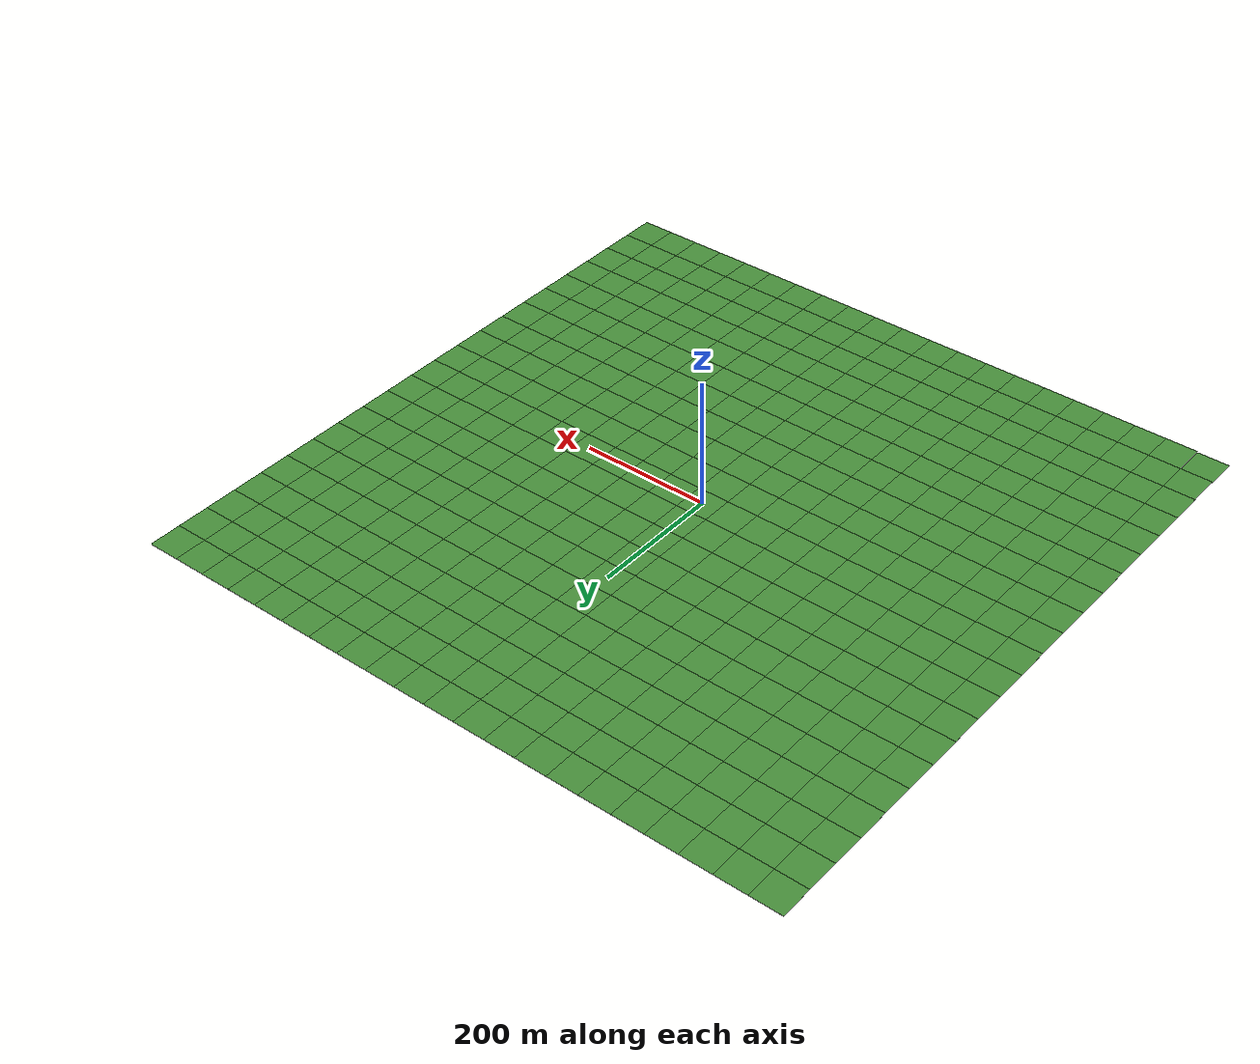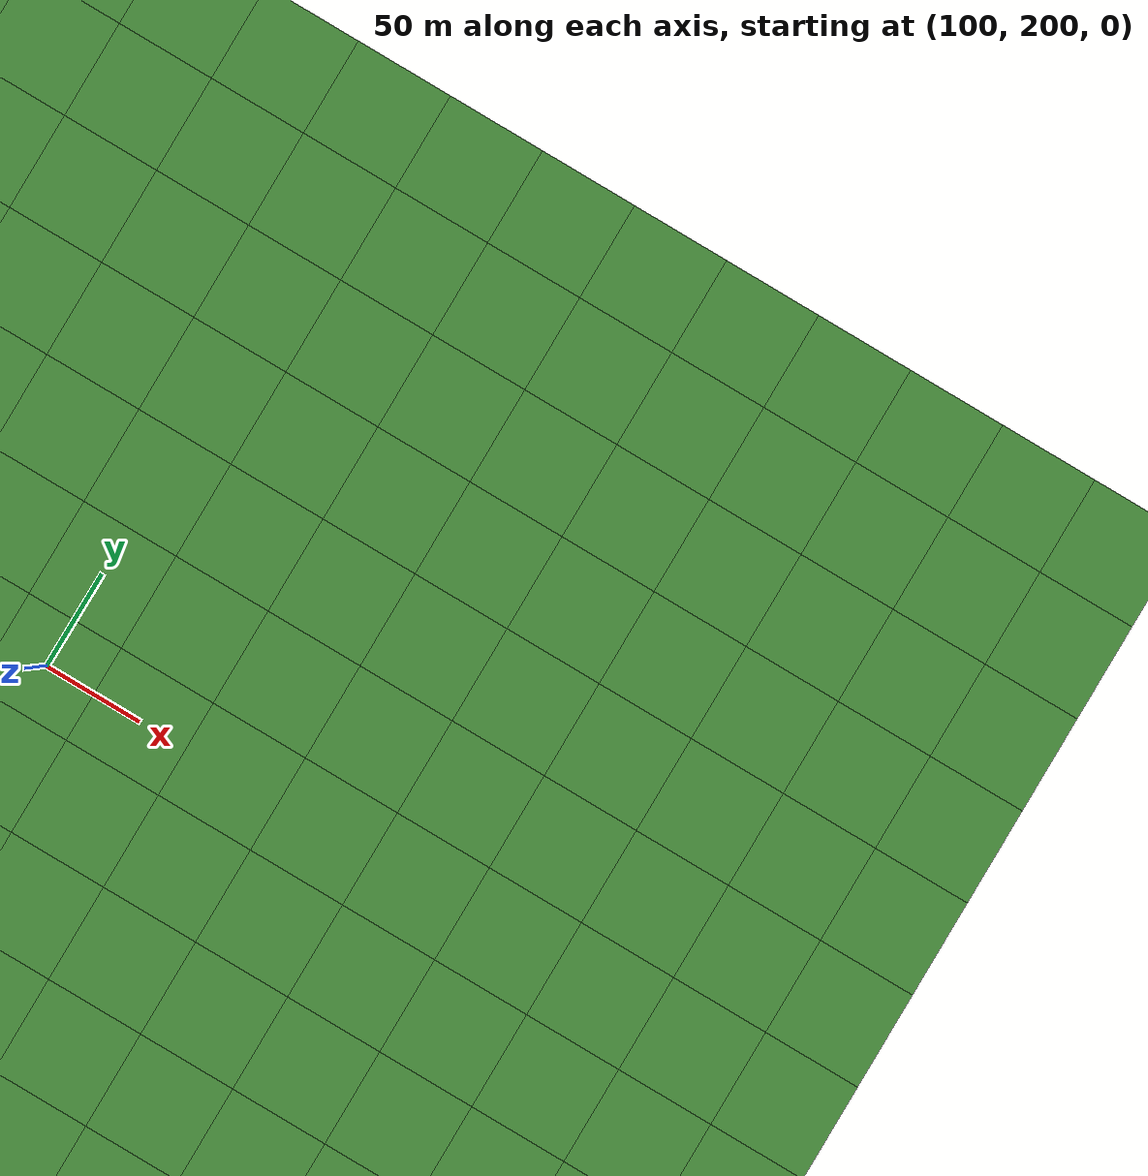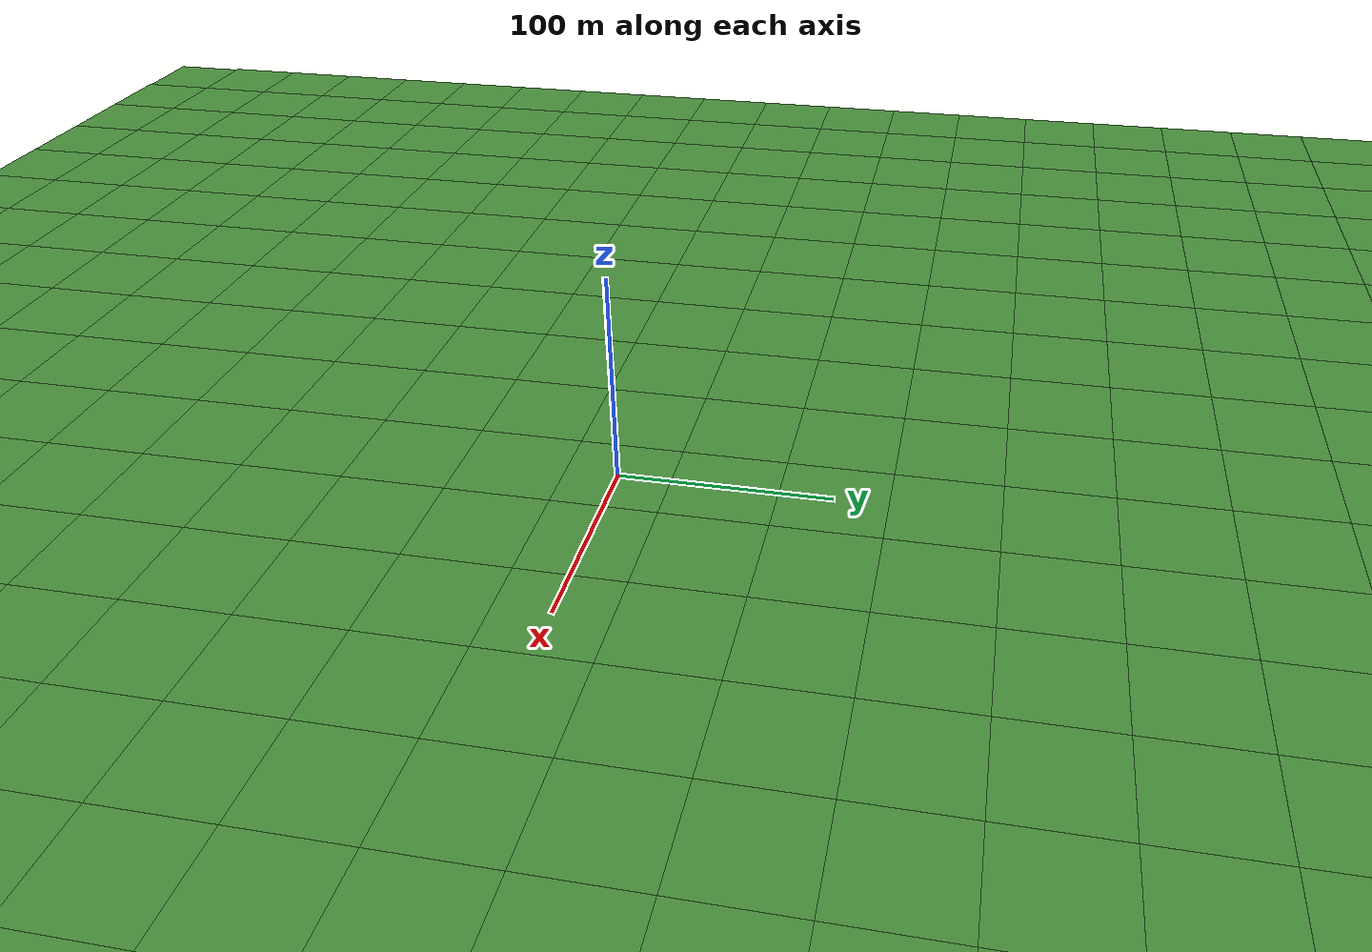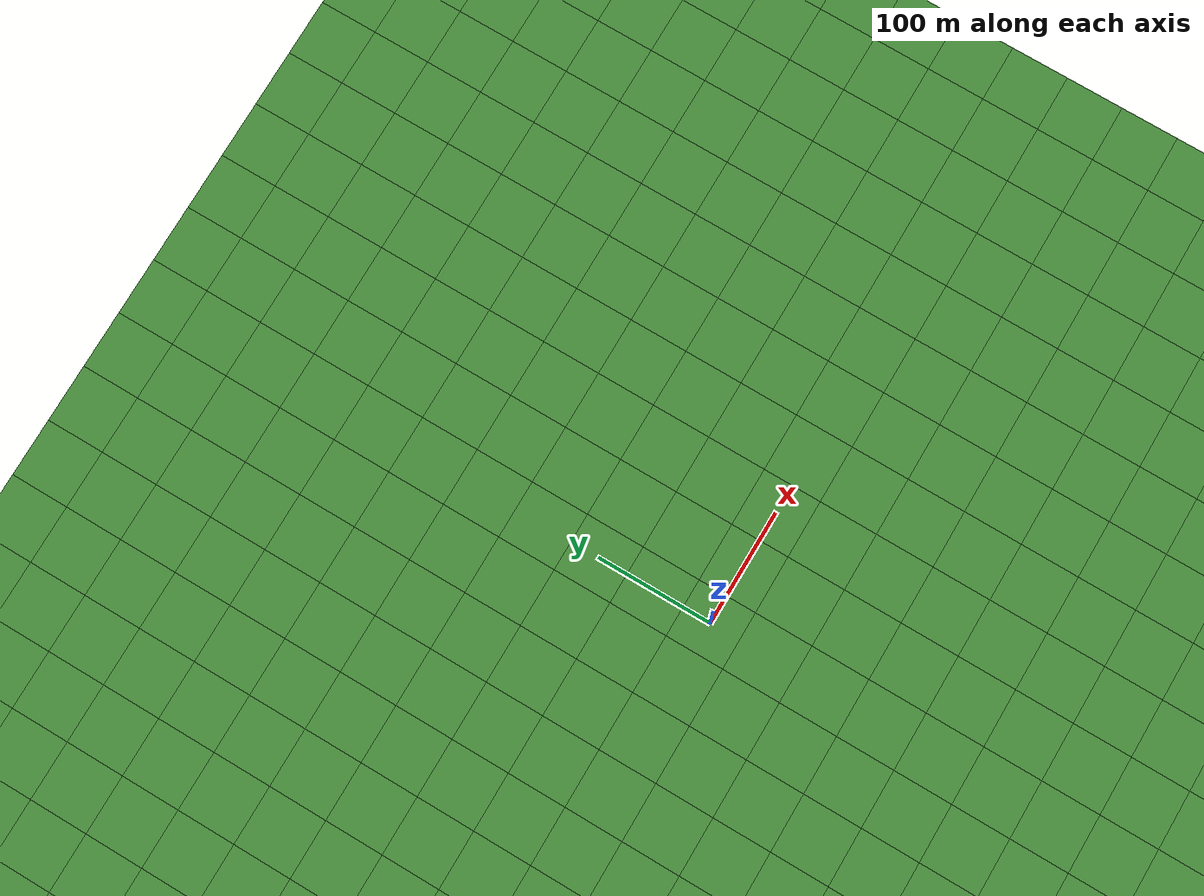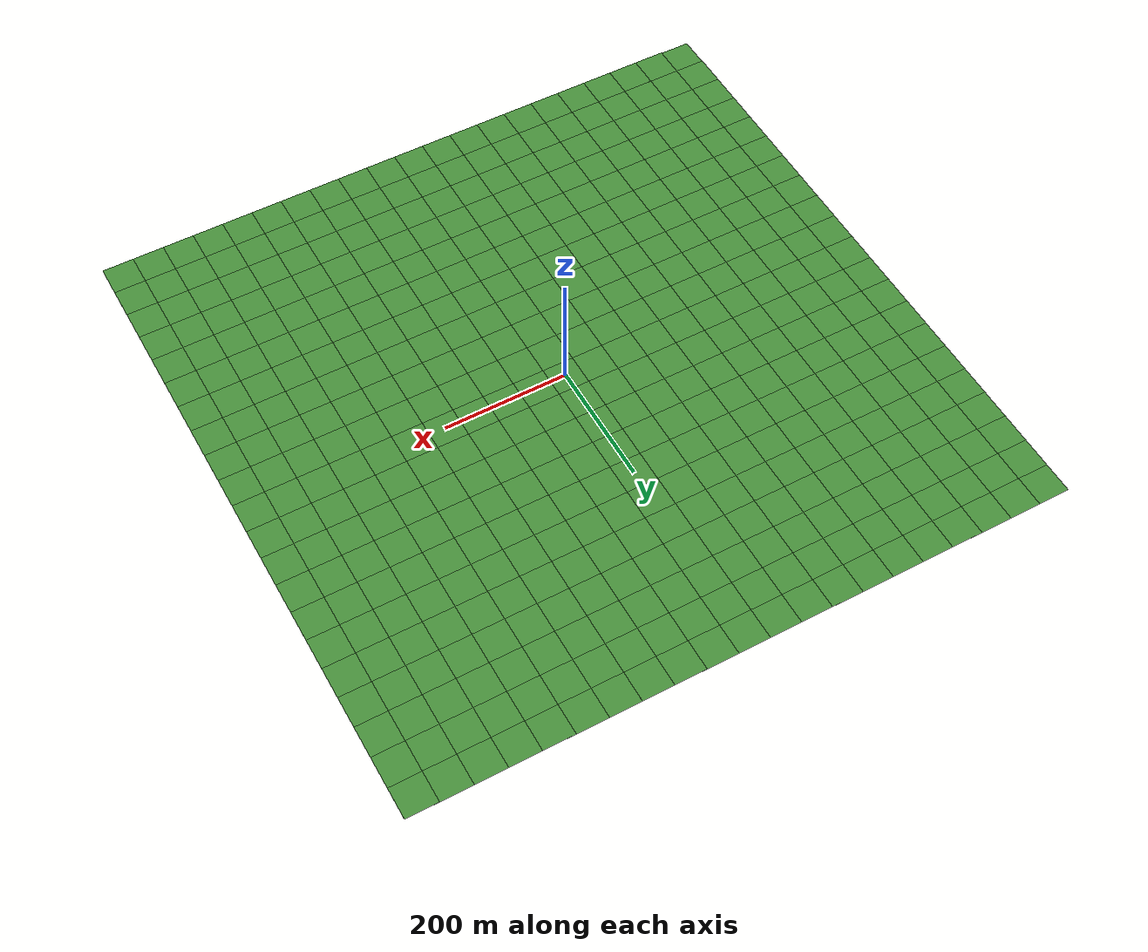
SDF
<?xml version="1.0" ?>

  <sdf version="1.5">
    <model name="grass_plane">

      <static>true</static>
      <link name='link'>
      <collision name='collision'>
        <geometry>
          <plane>
            <normal>0 0 1</normal>
            <size>1000 1000</size>
          </plane>
        </geometry>
        <surface>
          <friction>
            <ode>
              <mu>0.5</mu>
              <mu2>.5</mu2>
            </ode>
          </friction>
        </surface>
      </collision>

      <visual name="visual_0_0">
      <pose>-500 -500 0 0 0 0</pose>
        <cast_shadows>false</cast_shadows>
        <geometry>
          <plane>
            <normal>0 0 1</normal>
            <size>50 50</size>
          </plane>
        </geometry>
        <material>
          <script>
            <uri>model://grass_plane/materials/scripts</uri>
            <uri>model://grass_plane/materials/textures</uri>
            <name>vrc/grass</name>
          </script>
        </material>
      </visual>

      <visual name="visual_0_1">
      <pose>-500 -450 0 0 0 0</pose>
        <cast_shadows>false</cast_shadows>
        <geometry>
          <plane>
            <normal>0 0 1</normal>
            <size>50 50</size>
          </plane>
        </geometry>
        <material>
          <script>
            <uri>model://grass_plane/materials/scripts</uri>
            <uri>model://grass_plane/materials/textures</uri>
            <name>vrc/grass</name>
          </script>
        </material>
      </visual>

      <visual name="visual_0_2">
      <pose>-500 -400 0 0 0 0</pose>
        <cast_shadows>false</cast_shadows>
        <geometry>
          <plane>
            <normal>0 0 1</normal>
            <size>50 50</size>
          </plane>
        </geometry>
        <material>
          <script>
            <uri>model://grass_plane/materials/scripts</uri>
            <uri>model://grass_plane/materials/textures</uri>
            <name>vrc/grass</name>
          </script>
        </material>
      </visual>

      <visual name="visual_0_3">
      <pose>-500 -350 0 0 0 0</pose>
        <cast_shadows>false</cast_shadows>
        <geometry>
          <plane>
            <normal>0 0 1</normal>
            <size>50 50</size>
          </plane>
        </geometry>
        <material>
          <script>
            <uri>model://grass_plane/materials/scripts</uri>
            <uri>model://grass_plane/materials/textures</uri>
            <name>vrc/grass</name>
          </script>
        </material>
      </visual>

      <visual name="visual_0_4">
      <pose>-500 -300 0 0 0 0</pose>
        <cast_shadows>false</cast_shadows>
        <geometry>
          <plane>
            <normal>0 0 1</normal>
            <size>50 50</size>
          </plane>
        </geometry>
        <material>
          <script>
            <uri>model://grass_plane/materials/scripts</uri>
            <uri>model://grass_plane/materials/textures</uri>
            <name>vrc/grass</name>
          </script>
        </material>
      </visual>

      <visual name="visual_0_5">
      <pose>-500 -250 0 0 0 0</pose>
        <cast_shadows>false</cast_shadows>
        <geometry>
          <plane>
            <normal>0 0 1</normal>
            <size>50 50</size>
          </plane>
        </geometry>
        <material>
          <script>
            <uri>model://grass_plane/materials/scripts</uri>
            <uri>model://grass_plane/materials/textures</uri>
            <name>vrc/grass</name>
          </script>
        </material>
      </visual>

      <visual name="visual_0_6">
      <pose>-500 -200 0 0 0 0</pose>
        <cast_shadows>false</cast_shadows>
        <geometry>
          <plane>
            <normal>0 0 1</normal>
            <size>50 50</size>
          </plane>
        </geometry>
        <material>
          <script>
            <uri>model://grass_plane/materials/scripts</uri>
            <uri>model://grass_plane/materials/textures</uri>
            <name>vrc/grass</name>
          </script>
        </material>
      </visual>

      <visual name="visual_0_7">
      <pose>-500 -150 0 0 0 0</pose>
        <cast_shadows>false</cast_shadows>
        <geometry>
          <plane>
            <normal>0 0 1</normal>
            <size>50 50</size>
          </plane>
        </geometry>
        <material>
          <script>
            <uri>model://grass_plane/materials/scripts</uri>
            <uri>model://grass_plane/materials/textures</uri>
            <name>vrc/grass</name>
          </script>
        </material>
      </visual>

      <visual name="visual_0_8">
      <pose>-500 -100 0 0 0 0</pose>
        <cast_shadows>false</cast_shadows>
        <geometry>
          <plane>
            <normal>0 0 1</normal>
            <size>50 50</size>
          </plane>
        </geometry>
        <material>
          <script>
            <uri>model://grass_plane/materials/scripts</uri>
            <uri>model://grass_plane/materials/textures</uri>
            <name>vrc/grass</name>
          </script>
        </material>
      </visual>

      <visual name="visual_0_9">
      <pose>-500 -50 0 0 0 0</pose>
        <cast_shadows>false</cast_shadows>
        <geometry>
          <plane>
            <normal>0 0 1</normal>
            <size>50 50</size>
          </plane>
        </geometry>
        <material>
          <script>
            <uri>model://grass_plane/materials/scripts</uri>
            <uri>model://grass_plane/materials/textures</uri>
            <name>vrc/grass</name>
          </script>
        </material>
      </visual>

      <visual name="visual_0_10">
      <pose>-500 0 0 0 0 0</pose>
        <cast_shadows>false</cast_shadows>
        <geometry>
          <plane>
            <normal>0 0 1</normal>
            <size>50 50</size>
          </plane>
        </geometry>
        <material>
          <script>
            <uri>model://grass_plane/materials/scripts</uri>
            <uri>model://grass_plane/materials/textures</uri>
            <name>vrc/grass</name>
          </script>
        </material>
      </visual>

      <visual name="visual_0_11">
      <pose>-500 50 0 0 0 0</pose>
        <cast_shadows>false</cast_shadows>
        <geometry>
          <plane>
            <normal>0 0 1</normal>
            <size>50 50</size>
          </plane>
        </geometry>
        <material>
          <script>
            <uri>model://grass_plane/materials/scripts</uri>
            <uri>model://grass_plane/materials/textures</uri>
            <name>vrc/grass</name>
          </script>
        </material>
      </visual>

      <visual name="visual_0_12">
      <pose>-500 100 0 0 0 0</pose>
        <cast_shadows>false</cast_shadows>
        <geometry>
          <plane>
            <normal>0 0 1</normal>
            <size>50 50</size>
          </plane>
        </geometry>
        <material>
          <script>
            <uri>model://grass_plane/materials/scripts</uri>
            <uri>model://grass_plane/materials/textures</uri>
            <name>vrc/grass</name>
          </script>
        </material>
      </visual>

      <visual name="visual_0_13">
      <pose>-500 150 0 0 0 0</pose>
        <cast_shadows>false</cast_shadows>
        <geometry>
          <plane>
            <normal>0 0 1</normal>
            <size>50 50</size>
          </plane>
        </geometry>
        <material>
          <script>
            <uri>model://grass_plane/materials/scripts</uri>
            <uri>model://grass_plane/materials/textures</uri>
            <name>vrc/grass</name>
          </script>
        </material>
      </visual>

      <visual name="visual_0_14">
      <pose>-500 200 0 0 0 0</pose>
        <cast_shadows>false</cast_shadows>
        <geometry>
          <plane>
            <normal>0 0 1</normal>
            <size>50 50</size>
          </plane>
        </geometry>
        <material>
          <script>
            <uri>model://grass_plane/materials/scripts</uri>
            <uri>model://grass_plane/materials/textures</uri>
            <name>vrc/grass</name>
          </script>
        </material>
      </visual>

      <visual name="visual_0_15">
      <pose>-500 250 0 0 0 0</pose>
        <cast_shadows>false</cast_shadows>
        <geometry>
          <plane>
            <normal>0 0 1</normal>
            <size>50 50</size>
          </plane>
        </geometry>
        <material>
          <script>
            <uri>model://grass_plane/materials/scripts</uri>
            <uri>model://grass_plane/materials/textures</uri>
            <name>vrc/grass</name>
          </script>
        </material>
      </visual>

      <visual name="visual_0_16">
      <pose>-500 300 0 0 0 0</pose>
        <cast_shadows>false</cast_shadows>
        <geometry>
          <plane>
            <normal>0 0 1</normal>
            <size>50 50</size>
          </plane>
        </geometry>
        <material>
          <script>
            <uri>model://grass_plane/materials/scripts</uri>
            <uri>model://grass_plane/materials/textures</uri>
            <name>vrc/grass</name>
          </script>
        </material>
      </visual>

      <visual name="visual_0_17">
      <pose>-500 350 0 0 0 0</pose>
        <cast_shadows>false</cast_shadows>
        <geometry>
          <plane>
            <normal>0 0 1</normal>
            <size>50 50</size>
          </plane>
        </geometry>
        <material>
          <script>
            <uri>model://grass_plane/materials/scripts</uri>
            <uri>model://grass_plane/materials/textures</uri>
            <name>vrc/grass</name>
          </script>
        </material>
      </visual>

      <visual name="visual_0_18">
      <pose>-500 400 0 0 0 0</pose>
        <cast_shadows>false</cast_shadows>
        <geometry>
          <plane>
            <normal>0 0 1</normal>
            <size>50 50</size>
          </plane>
        </geometry>
        <material>
          <script>
            <uri>model://grass_plane/materials/scripts</uri>
            <uri>model://grass_plane/materials/textures</uri>
            <name>vrc/grass</name>
          </script>
        </material>
      </visual>

      <visual name="visual_0_19">
      <pose>-500 450 0 0 0 0</pose>
        <cast_shadows>false</cast_shadows>
        <geometry>
          <plane>
            <normal>0 0 1</normal>
            <size>50 50</size>
          </plane>
        </geometry>
        <material>
          <script>
            <uri>model://grass_plane/materials/scripts</uri>
            <uri>model://grass_plane/materials/textures</uri>
            <name>vrc/grass</name>
          </script>
        </material>
      </visual>

      <visual name="visual_0_20">
      <pose>-500 500 0 0 0 0</pose>
        <cast_shadows>false</cast_shadows>
        <geometry>
          <plane>
            <normal>0 0 1</normal>
            <size>50 50</size>
          </plane>
        </geometry>
        <material>
          <script>
            <uri>model://grass_plane/materials/scripts</uri>
            <uri>model://grass_plane/materials/textures</uri>
            <name>vrc/grass</name>
          </script>
        </material>
      </visual>

      <visual name="visual_1_0">
      <pose>-450 -500 0 0 0 0</pose>
        <cast_shadows>false</cast_shadows>
        <geometry>
          <plane>
            <normal>0 0 1</normal>
            <size>50 50</size>
          </plane>
        </geometry>
        <material>
          <script>
            <uri>model://grass_plane/materials/scripts</uri>
            <uri>model://grass_plane/materials/textures</uri>
            <name>vrc/grass</name>
          </script>
        </material>
      </visual>

      <visual name="visual_1_1">
      <pose>-450 -450 0 0 0 0</pose>
        <cast_shadows>false</cast_shadows>
        <geometry>
          <plane>
            <normal>0 0 1</normal>
            <size>50 50</size>
          </plane>
        </geometry>
        <material>
          <script>
            <uri>model://grass_plane/materials/scripts</uri>
            <uri>model://grass_plane/materials/textures</uri>
            <name>vrc/grass</name>
          </script>
        </material>
      </visual>

      <visual name="visual_1_2">
      <pose>-450 -400 0 0 0 0</pose>
        <cast_shadows>false</cast_shadows>
        <geometry>
          <plane>
            <normal>0 0 1</normal>
            <size>50 50</size>
          </plane>
        </geometry>
        <material>
          <script>
            <uri>model://grass_plane/materials/scripts</uri>
            <uri>model://grass_plane/materials/textures</uri>
            <name>vrc/grass</name>
          </script>
        </material>
      </visual>

      <visual name="visual_1_3">
      <pose>-450 -350 0 0 0 0</pose>
        <cast_shadows>false</cast_shadows>
        <geometry>
          <plane>
            <normal>0 0 1</normal>
            <size>50 50</size>
          </plane>
        </geometry>
        <material>
          <script>
            <uri>model://grass_plane/materials/scripts</uri>
            <uri>model://grass_plane/materials/textures</uri>
            <name>vrc/grass</name>
          </script>
        </material>
      </visual>

      <visual name="visual_1_4">
      <pose>-450 -300 0 0 0 0</pose>
        <cast_shadows>false</cast_shadows>
        <geometry>
          <plane>
            <normal>0 0 1</normal>
            <size>50 50</size>
          </plane>
        </geometry>
        <material>
          <script>
            <uri>model://grass_plane/materials/scripts</uri>
            <uri>model://grass_plane/materials/textures</uri>
            <name>vrc/grass</name>
          </script>
        </material>
      </visual>

      <visual name="visual_1_5">
      <pose>-450 -250 0 0 0 0</pose>
        <cast_shadows>false</cast_shadows>
        <geometry>
          <plane>
            <normal>0 0 1</normal>
            <size>50 50</size>
          </plane>
        </geometry>
        <material>
          <script>
            <uri>model://grass_plane/materials/scripts</uri>
            <uri>model://grass_plane/materials/textures</uri>
            <name>vrc/grass</name>
          </script>
        </material>
      </visual>

      <visual name="visual_1_6">
      <pose>-450 -200 0 0 0 0</pose>
        <cast_shadows>false</cast_shadows>
        <geometry>
          <plane>
            <normal>0 0 1</normal>
            <size>50 50</size>
          </plane>
        </geometry>
        <material>
          <script>
            <uri>model://grass_plane/materials/scripts</uri>
            <uri>model://grass_plane/materials/textures</uri>
            <name>vrc/grass</name>
          </script>
        </material>
      </visual>

      <visual name="visual_1_7">
      <pose>-450 -150 0 0 0 0</pose>
        <cast_shadows>false</cast_shadows>
        <geometry>
          <plane>
            <normal>0 0 1</normal>
            <size>50 50</size>
          </plane>
        </geometry>
        <material>
          <script>
            <uri>model://grass_plane/materials/scripts</uri>
            <uri>model://grass_plane/materials/textures</uri>
            <name>vrc/grass</name>
          </script>
        </material>
      </visual>

      <visual name="visual_1_8">
      <pose>-450 -100 0 0 0 0</pose>
        <cast_shadows>false</cast_shadows>
        <geometry>
          <plane>
            <normal>0 0 1</normal>
            <size>50 50</size>
          </plane>
        </geometry>
        <material>
          <script>
            <uri>model://grass_plane/materials/scripts</uri>
            <uri>model://grass_plane/materials/textures</uri>
            <name>vrc/grass</name>
          </script>
        </material>
      </visual>

      <visual name="visual_1_9">
      <pose>-450 -50 0 0 0 0</pose>
        <cast_shadows>false</cast_shadows>
        <geometry>
          <plane>
            <normal>0 0 1</normal>
            <size>50 50</size>
          </plane>
        </geometry>
        <material>
          <script>
            <uri>model://grass_plane/materials/scripts</uri>
            <uri>model://grass_plane/materials/textures</uri>
            <name>vrc/grass</name>
          </script>
        </material>
      </visual>

      <visual name="visual_1_10">
      <pose>-450 0 0 0 0 0</pose>
        <cast_shadows>false</cast_shadows>
        <geometry>
          <plane>
            <normal>0 0 1</normal>
            <size>50 50</size>
          </plane>
        </geometry>
        <material>
          <script>
            <uri>model://grass_plane/materials/scripts</uri>
            <uri>model://grass_plane/materials/textures</uri>
            <name>vrc/grass</name>
          </script>
        </material>
      </visual>

      <visual name="visual_1_11">
      <pose>-450 50 0 0 0 0</pose>
        <cast_shadows>false</cast_shadows>
        <geometry>
          <plane>
            <normal>0 0 1</normal>
            <size>50 50</size>
          </plane>
        </geometry>
        <material>
          <script>
            <uri>model://grass_plane/materials/scripts</uri>
            <uri>model://grass_plane/materials/textures</uri>
            <name>vrc/grass</name>
          </script>
        </material>
      </visual>

      <visual name="visual_1_12">
      <pose>-450 100 0 0 0 0</pose>
        <cast_shadows>false</cast_shadows>
        <geometry>
          <plane>
            <normal>0 0 1</normal>
            <size>50 50</size>
          </plane>
        </geometry>
        <material>
          <script>
            <uri>model://grass_plane/materials/scripts</uri>
            <uri>model://grass_plane/materials/textures</uri>
            <name>vrc/grass</name>
          </script>
        </material>
      </visual>

      <visual name="visual_1_13">
      <pose>-450 150 0 0 0 0</pose>
        <cast_shadows>false</cast_shadows>
        <geometry>
          <plane>
            <normal>0 0 1</normal>
            <size>50 50</size>
          </plane>
        </geometry>
        <material>
          <script>
            <uri>model://grass_plane/materials/scripts</uri>
            <uri>model://grass_plane/materials/textures</uri>
            <name>vrc/grass</name>
          </script>
        </material>
      </visual>

      <visual name="visual_1_14">
      <pose>-450 200 0 0 0 0</pose>
        <cast_shadows>false</cast_shadows>
        <geometry>
          <plane>
            <normal>0 0 1</normal>
            <size>50 50</size>
          </plane>
        </geometry>
        <material>
          <script>
            <uri>model://grass_plane/materials/scripts</uri>
            <uri>model://grass_plane/materials/textures</uri>
            <name>vrc/grass</name>
          </script>
        </material>
      </visual>

      <visual name="visual_1_15">
      <pose>-450 250 0 0 0 0</pose>
        <cast_shadows>false</cast_shadows>
        <geometry>
          <plane>
            <normal>0 0 1</normal>
            <size>50 50</size>
          </plane>
        </geometry>
        <material>
          <script>
            <uri>model://grass_plane/materials/scripts</uri>
            <uri>model://grass_plane/materials/textures</uri>
            <name>vrc/grass</name>
          </script>
        </material>
      </visual>

      <visual name="visual_1_16">
      <pose>-450 300 0 0 0 0</pose>
        <cast_shadows>false</cast_shadows>
        <geometry>
          <plane>
            <normal>0 0 1</normal>
            <size>50 50</size>
          </plane>
        </geometry>
        <material>
          <script>
            <uri>model://grass_plane/materials/scripts</uri>
            <uri>model://grass_plane/materials/textures</uri>
            <name>vrc/grass</name>
          </script>
        </material>
      </visual>

      <visual name="visual_1_17">
      <pose>-450 350 0 0 0 0</pose>
        <cast_shadows>false</cast_shadows>
        <geometry>
          <plane>
            <normal>0 0 1</normal>
            <size>50 50</size>
          </plane>
        </geometry>
        <material>
          <script>
            <uri>model://grass_plane/materials/scripts</uri>
            <uri>model://grass_plane/materials/textures</uri>
            <name>vrc/grass</name>
          </script>
        </material>
      </visual>

      <visual name="visual_1_18">
      <pose>-450 400 0 0 0 0</pose>
        <cast_shadows>false</cast_shadows>
        <geometry>
          <plane>
            <normal>0 0 1</normal>
            <size>50 50</size>
          </plane>
        </geometry>
        <material>
          <script>
            <uri>model://grass_plane/materials/scripts</uri>
            <uri>model://grass_plane/materials/textures</uri>
            <name>vrc/grass</name>
          </script>
        </material>
      </visual>

      <visual name="visual_1_19">
      <pose>-450 450 0 0 0 0</pose>
        <cast_shadows>false</cast_shadows>
        <geometry>
          <plane>
            <normal>0 0 1</normal>
            <size>50 50</size>
          </plane>
        </geometry>
        <material>
          <script>
            <uri>model://grass_plane/materials/scripts</uri>
            <uri>model://grass_plane/materials/textures</uri>
            <name>vrc/grass</name>
          </script>
        </material>
      </visual>

      <visual name="visual_1_20">
      <pose>-450 500 0 0 0 0</pose>
        <cast_shadows>false</cast_shadows>
        <geometry>
          <plane>
            <normal>0 0 1</normal>
            <size>50 50</size>
          </plane>
        </geometry>
        <material>
          <script>
            <uri>model://grass_plane/materials/scripts</uri>
            <uri>model://grass_plane/materials/textures</uri>
            <name>vrc/grass</name>
          </script>
        </material>
      </visual>

      <visual name="visual_2_0">
      <pose>-400 -500 0 0 0 0</pose>
        <cast_shadows>false</cast_shadows>
        <geometry>
          <plane>
            <normal>0 0 1</normal>
            <size>50 50</size>
          </plane>
        </geometry>
        <material>
          <script>
            <uri>model://grass_plane/materials/scripts</uri>
            <uri>model://grass_plane/materials/textures</uri>
            <name>vrc/grass</name>
          </script>
        </material>
      </visual>

      <visual name="visual_2_1">
      <pose>-400 -450 0 0 0 0</pose>
        <cast_shadows>false</cast_shadows>
        <geometry>
          <plane>
            <normal>0 0 1</normal>
            <size>50 50</size>
          </plane>
        </geometry>
        <material>
          <script>
            <uri>model://grass_plane/materials/scripts</uri>
            <uri>model://grass_plane/materials/textures</uri>
            <name>vrc/grass</name>
          </script>
        </material>
      </visual>

      <visual name="visual_2_2">
      <pose>-400 -400 0 0 0 0</pose>
        <cast_shadows>false</cast_shadows>
        <geometry>
          <plane>
            <normal>0 0 1</normal>
            <size>50 50</size>
          </plane>
        </geometry>
        <material>
          <script>
            <uri>model://grass_plane/materials/scripts</uri>
            <uri>model://grass_plane/materials/textures</uri>
            <name>vrc/grass</name>
          </script>
        </material>
      </visual>

      <visual name="visual_2_3">
      <pose>-400 -350 0 0 0 0</pose>
        <cast_shadows>false</cast_shadows>
        <geometry>
          <plane>
            <normal>0 0 1</normal>
            <size>50 50</size>
          </plane>
        </geometry>
        <material>
          <script>
            <uri>model://grass_plane/materials/scripts</uri>
            <uri>model://grass_plane/materials/textures</uri>
            <name>vrc/grass</name>
          </script>
        </material>
      </visual>

      <visual name="visual_2_4">
      <pose>-400 -300 0 0 0 0</pose>
        <cast_shadows>false</cast_shadows>
        <geometry>
          <plane>
            <normal>0 0 1</normal>
            <size>50 50</size>
          </plane>
        </geometry>
        <material>
          <script>
            <uri>model://grass_plane/materials/scripts</uri>
            <uri>model://grass_plane/materials/textures</uri>
            <name>vrc/grass</name>
          </script>
        </material>
      </visual>

      <visual name="visual_2_5">
      <pose>-400 -250 0 0 0 0</pose>
        <cast_shadows>false</cast_shadows>
        <geometry>
          <plane>
            <normal>0 0 1</normal>
            <size>50 50</size>
          </plane>
        </geometry>
        <material>
          <script>
            <uri>model://grass_plane/materials/scripts</uri>
            <uri>model://grass_plane/materials/textures</uri>
            <name>vrc/grass</name>
          </script>
        </material>
      </visual>

      <visual name="visual_2_6">
      <pose>-400 -200 0 0 0 0</pose>
        <cast_shadows>false</cast_shadows>
        <geometry>
          <plane>
            <normal>0 0 1</normal>
            <size>50 50</size>
          </plane>
        </geometry>
        <material>
          <script>
            <uri>model://grass_plane/materials/scripts</uri>
            <uri>model://grass_plane/materials/textures</uri>
            <name>vrc/grass</name>
          </script>
        </material>
      </visual>

      <visual name="visual_2_7">
      <pose>-400 -150 0 0 0 0</pose>
        <cast_shadows>false</cast_shadows>
        <geometry>
          <plane>
            <normal>0 0 1</normal>
            <size>50 50</size>
          </plane>
        </geometry>
        <material>
          <script>
            <uri>model://grass_plane/materials/scripts</uri>
            <uri>model://grass_plane/materials/textures</uri>
            <name>vrc/grass</name>
          </script>
        </material>
      </visual>

      <visual name="visual_2_8">
      <pose>-400 -100 0 0 0 0</pose>
        <cast_shadows>false</cast_shadows>
        <geometry>
          <plane>
            <normal>0 0 1</normal>
            <size>50 50</size>
          </plane>
        </geometry>
        <material>
          <script>
            <uri>model://grass_plane/materials/scripts</uri>
            <uri>model://grass_plane/materials/textures</uri>
            <name>vrc/grass</name>
          </script>
        </material>
      </visual>

      <visual name="visual_2_9">
      <pose>-400 -50 0 0 0 0</pose>
        <cast_shadows>false</cast_shadows>
        <geometry>
          <plane>
            <normal>0 0 1</normal>
            <size>50 50</size>
          </plane>
        </geometry>
        <material>
          <script>
            <uri>model://grass_plane/materials/scripts</uri>
            <uri>model://grass_plane/materials/textures</uri>
            <name>vrc/grass</name>
          </script>
        </material>
      </visual>

      <visual name="visual_2_10">
      <pose>-400 0 0 0 0 0</pose>
        <cast_shadows>false</cast_shadows>
        <geometry>
          <plane>
            <normal>0 0 1</normal>
            <size>50 50</size>
          </plane>
        </geometry>
        <material>
          <script>
            <uri>model://grass_plane/materials/scripts</uri>
            <uri>model://grass_plane/materials/textures</uri>
            <name>vrc/grass</name>
          </script>
        </material>
      </visual>

      <visual name="visual_2_11">
      <pose>-400 50 0 0 0 0</pose>
        <cast_shadows>false</cast_shadows>
        <geometry>
          <plane>
            <normal>0 0 1</normal>
            <size>50 50</size>
          </plane>
        </geometry>
        <material>
          <script>
            <uri>model://grass_plane/materials/scripts</uri>
            <uri>model://grass_plane/materials/textures</uri>
            <name>vrc/grass</name>
          </script>
        </material>
      </visual>

      <visual name="visual_2_12">
      <pose>-400 100 0 0 0 0</pose>
        <cast_shadows>false</cast_shadows>
        <geometry>
          <plane>
            <normal>0 0 1</normal>
            <size>50 50</size>
          </plane>
        </geometry>
        <material>
          <script>
            <uri>model://grass_plane/materials/scripts</uri>
            <uri>model://grass_plane/materials/textures</uri>
            <name>vrc/grass</name>
          </script>
        </material>
      </visual>

      <visual name="visual_2_13">
      <pose>-400 150 0 0 0 0</pose>
        <cast_shadows>false</cast_shadows>
        <geometry>
          <plane>
            <normal>0 0 1</normal>
            <size>50 50</size>
          </plane>
        </geometry>
        <material>
          <script>
            <uri>model://grass_plane/materials/scripts</uri>
            <uri>model://grass_plane/materials/textures</uri>
            <name>vrc/grass</name>
          </script>
        </material>
      </visual>

      <visual name="visual_2_14">
      <pose>-400 200 0 0 0 0</pose>
        <cast_shadows>false</cast_shadows>
        <geometry>
          <plane>
            <normal>0 0 1</normal>
            <size>50 50</size>
          </plane>
        </geometry>
        <material>
          <script>
            <uri>model://grass_plane/materials/scripts</uri>
            <uri>model://grass_plane/materials/textures</uri>
            <name>vrc/grass</name>
          </script>
        </material>
      </visual>

      <visual name="visual_2_15">
      <pose>-400 250 0 0 0 0</pose>
        <cast_shadows>false</cast_shadows>
        <geometry>
          <plane>
            <normal>0 0 1</normal>
            <size>50 50</size>
          </plane>
        </geometry>
        <material>
          <script>
            <uri>model://grass_plane/materials/scripts</uri>
            <uri>model://grass_plane/materials/textures</uri>
            <name>vrc/grass</name>
          </script>
        </material>
      </visual>

      <visual name="visual_2_16">
      <pose>-400 300 0 0 0 0</pose>
        <cast_shadows>false</cast_shadows>
        <geometry>
          <plane>
            <normal>0 0 1</normal>
            <size>50 50</size>
          </plane>
        </geometry>
        <material>
          <script>
            <uri>model://grass_plane/materials/scripts</uri>
            <uri>model://grass_plane/materials/textures</uri>
            <name>vrc/grass</name>
          </script>
        </material>
      </visual>

      <visual name="visual_2_17">
      <pose>-400 350 0 0 0 0</pose>
        <cast_shadows>false</cast_shadows>
        <geometry>
          <plane>
            <normal>0 0 1</normal>
            <size>50 50</size>
          </plane>
        </geometry>
        <material>
          <script>
            <uri>model://grass_plane/materials/scripts</uri>
            <uri>model://grass_plane/materials/textures</uri>
            <name>vrc/grass</name>
          </script>
        </material>
      </visual>

      <visual name="visual_2_18">
      <pose>-400 400 0 0 0 0</pose>
        <cast_shadows>false</cast_shadows>
        <geometry>
          <plane>
            <normal>0 0 1</normal>
            <size>50 50</size>
          </plane>
        </geometry>
        <material>
          <script>
            <uri>model://grass_plane/materials/scripts</uri>
            <uri>model://grass_plane/materials/textures</uri>
            <name>vrc/grass</name>
          </script>
        </material>
      </visual>

      <visual name="visual_2_19">
      <pose>-400 450 0 0 0 0</pose>
        <cast_shadows>false</cast_shadows>
        <geometry>
          <plane>
            <normal>0 0 1</normal>
            <size>50 50</size>
          </plane>
        </geometry>
        <material>
          <script>
            <uri>model://grass_plane/materials/scripts</uri>
            <uri>model://grass_plane/materials/textures</uri>
            <name>vrc/grass</name>
          </script>
        </material>
      </visual>

      <visual name="visual_2_20">
      <pose>-400 500 0 0 0 0</pose>
        <cast_shadows>false</cast_shadows>
        <geometry>
          <plane>
            <normal>0 0 1</normal>
            <size>50 50</size>
          </plane>
        </geometry>
        <material>
          <script>
            <uri>model://grass_plane/materials/scripts</uri>
            <uri>model://grass_plane/materials/textures</uri>
            <name>vrc/grass</name>
          </script>
        </material>
      </visual>

      <visual name="visual_3_0">
      <pose>-350 -500 0 0 0 0</pose>
        <cast_shadows>false</cast_shadows>
        <geometry>
          <plane>
            <normal>0 0 1</normal>
            <size>50 50</size>
          </plane>
        </geometry>
        <material>
          <script>
            <uri>model://grass_plane/materials/scripts</uri>
            <uri>model://grass_plane/materials/textures</uri>
            <name>vrc/grass</name>
          </script>
        </material>
      </visual>

      <visual name="visual_3_1">
      <pose>-350 -450 0 0 0 0</pose>
        <cast_shadows>false</cast_shadows>
        <geometry>
          <plane>
            <normal>0 0 1</normal>
            <size>50 50</size>
          </plane>
        </geometry>
        <material>
          <script>
            <uri>model://grass_plane/materials/scripts</uri>
            <uri>model://grass_plane/materials/textures</uri>
            <name>vrc/grass</name>
          </script>
        </material>
      </visual>

      <visual name="visual_3_2">
      <pose>-350 -400 0 0 0 0</pose>
        <cast_shadows>false</cast_shadows>
        <geometry>
          <plane>
            <normal>0 0 1</normal>
            <size>50 50</size>
          </plane>
        </geometry>
        <material>
          <script>
            <uri>model://grass_plane/materials/scripts</uri>
            <uri>model://grass_plane/materials/textures</uri>
            <name>vrc/grass</name>
          </script>
        </material>
      </visual>

      <visual name="visual_3_3">
      <pose>-350 -350 0 0 0 0</pose>
        <cast_shadows>false</cast_shadows>
        <geometry>
          <plane>
            <normal>0 0 1</normal>
            <size>50 50</size>
          </plane>
        </geometry>
        <material>
          <script>
            <uri>model://grass_plane/materials/scripts</uri>
            <uri>model://grass_plane/materials/textures</uri>
            <name>vrc/grass</name>
          </script>
        </material>
      </visual>

      <visual name="visual_3_4">
      <pose>-350 -300 0 0 0 0</pose>
        <cast_shadows>false</cast_shadows>
        <geometry>
          <plane>
            <normal>0 0 1</normal>
            <size>50 50</size>
          </plane>
        </geometry>
        <material>
          <script>
            <uri>model://grass_plane/materials/scripts</uri>
            <uri>model://grass_plane/materials/textures</uri>
            <name>vrc/grass</name>
          </script>
        </material>
      </visual>

      <visual name="visual_3_5">
      <pose>-350 -250 0 0 0 0</pose>
        <cast_shadows>false</cast_shadows>
        <geometry>
          <plane>
            <normal>0 0 1</normal>
            <size>50 50</size>
          </plane>
        </geometry>
        <material>
          <script>
            <uri>model://grass_plane/materials/scripts</uri>
            <uri>model://grass_plane/materials/textures</uri>
            <name>vrc/grass</name>
          </script>
        </material>
      </visual>

      <visual name="visual_3_6">
      <pose>-350 -200 0 0 0 0</pose>
        <cast_shadows>false</cast_shadows>
        <geometry>
          <plane>
            <normal>0 0 1</normal>
            <size>50 50</size>
          </plane>
        </geometry>
        <material>
          <script>
            <uri>model://grass_plane/materials/scripts</uri>
            <uri>model://grass_plane/materials/textures</uri>
            <name>vrc/grass</name>
          </script>
        </material>
      </visual>

      <visual name="visual_3_7">
      <pose>-350 -150 0 0 0 0</pose>
        <cast_shadows>false</cast_shadows>
        <geometry>
          <plane>
            <normal>0 0 1</normal>
            <size>50 50</size>
          </plane>
        </geometry>
        <material>
          <script>
            <uri>model://grass_plane/materials/scripts</uri>
            <uri>model://grass_plane/materials/textures</uri>
            <name>vrc/grass</name>
          </script>
        </material>
      </visual>

      <visual name="visual_3_8">
      <pose>-350 -100 0 0 0 0</pose>
        <cast_shadows>false</cast_shadows>
        <geometry>
          <plane>
            <normal>0 0 1</normal>
            <size>50 50</size>
          </plane>
        </geometry>
        <material>
          <script>
            <uri>model://grass_plane/materials/scripts</uri>
            <uri>model://grass_plane/materials/textures</uri>
            <name>vrc/grass</name>
          </script>
        </material>
      </visual>

      <visual name="visual_3_9">
      <pose>-350 -50 0 0 0 0</pose>
        <cast_shadows>false</cast_shadows>
        <geometry>
          <plane>
            <normal>0 0 1</normal>
            <size>50 50</size>
          </plane>
        </geometry>
        <material>
          <script>
            <uri>model://grass_plane/materials/scripts</uri>
            <uri>model://grass_plane/materials/textures</uri>
            <name>vrc/grass</name>
          </script>
        </material>
      </visual>

      <visual name="visual_3_10">
      <pose>-350 0 0 0 0 0</pose>
        <cast_shadows>false</cast_shadows>
        <geometry>
          <plane>
            <normal>0 0 1</normal>
            <size>50 50</size>
          </plane>
        </geometry>
        <material>
          <script>
            <uri>model://grass_plane/materials/scripts</uri>
            <uri>model://grass_plane/materials/textures</uri>
            <name>vrc/grass</name>
          </script>
        </material>
      </visual>

      <visual name="visual_3_11">
      <pose>-350 50 0 0 0 0</pose>
        <cast_shadows>false</cast_shadows>
        <geometry>
          <plane>
            <normal>0 0 1</normal>
            <size>50 50</size>
          </plane>
        </geometry>
        <material>
          <script>
            <uri>model://grass_plane/materials/scripts</uri>
            <uri>model://grass_plane/materials/textures</uri>
            <name>vrc/grass</name>
          </script>
        </material>
      </visual>

      <visual name="visual_3_12">
      <pose>-350 100 0 0 0 0</pose>
        <cast_shadows>false</cast_shadows>
        <geometry>
          <plane>
            <normal>0 0 1</normal>
            <size>50 50</size>
          </plane>
        </geometry>
        <material>
          <script>
            <uri>model://grass_plane/materials/scripts</uri>
            <uri>model://grass_plane/materials/textures</uri>
            <name>vrc/grass</name>
          </script>
        </material>
      </visual>

      <visual name="visual_3_13">
      <pose>-350 150 0 0 0 0</pose>
        <cast_shadows>false</cast_shadows>
        <geometry>
          <plane>
            <normal>0 0 1</normal>
            <size>50 50</size>
          </plane>
        </geometry>
        <material>
          <script>
            <uri>model://grass_plane/materials/scripts</uri>
            <uri>model://grass_plane/materials/textures</uri>
            <name>vrc/grass</name>
          </script>
        </material>
      </visual>

      <visual name="visual_3_14">
      <pose>-350 200 0 0 0 0</pose>
        <cast_shadows>false</cast_shadows>
        <geometry>
          <plane>
            <normal>0 0 1</normal>
            <size>50 50</size>
          </plane>
        </geometry>
        <material>
          <script>
            <uri>model://grass_plane/materials/scripts</uri>
            <uri>model://grass_plane/materials/textures</uri>
            <name>vrc/grass</name>
          </script>
        </material>
      </visual>

      <visual name="visual_3_15">
      <pose>-350 250 0 0 0 0</pose>
        <cast_shadows>false</cast_shadows>
        <geometry>
          <plane>
            <normal>0 0 1</normal>
            <size>50 50</size>
          </plane>
        </geometry>
        <material>
          <script>
            <uri>model://grass_plane/materials/scripts</uri>
            <uri>model://grass_plane/materials/textures</uri>
            <name>vrc/grass</name>
          </script>
        </material>
      </visual>

      <visual name="visual_3_16">
      <pose>-350 300 0 0 0 0</pose>
        <cast_shadows>false</cast_shadows>
        <geometry>
          <plane>
            <normal>0 0 1</normal>
            <size>50 50</size>
          </plane>
        </geometry>
        <material>
          <script>
            <uri>model://grass_plane/materials/scripts</uri>
            <uri>model://grass_plane/materials/textures</uri>
            <name>vrc/grass</name>
          </script>
        </material>
      </visual>

      <visual name="visual_3_17">
      <pose>-350 350 0 0 0 0</pose>
        <cast_shadows>false</cast_shadows>
        <geometry>
          <plane>
            <normal>0 0 1</normal>
            <size>50 50</size>
          </plane>
        </geometry>
        <material>
          <script>
            <uri>model://grass_plane/materials/scripts</uri>
            <uri>model://grass_plane/materials/textures</uri>
            <name>vrc/grass</name>
          </script>
        </material>
      </visual>

      <visual name="visual_3_18">
      <pose>-350 400 0 0 0 0</pose>
        <cast_shadows>false</cast_shadows>
        <geometry>
          <plane>
            <normal>0 0 1</normal>
            <size>50 50</size>
          </plane>
        </geometry>
        <material>
          <script>
            <uri>model://grass_plane/materials/scripts</uri>
            <uri>model://grass_plane/materials/textures</uri>
            <name>vrc/grass</name>
          </script>
        </material>
      </visual>

      <visual name="visual_3_19">
      <pose>-350 450 0 0 0 0</pose>
        <cast_shadows>false</cast_shadows>
        <geometry>
          <plane>
            <normal>0 0 1</normal>
            <size>50 50</size>
          </plane>
        </geometry>
        <material>
          <script>
            <uri>model://grass_plane/materials/scripts</uri>
            <uri>model://grass_plane/materials/textures</uri>
            <name>vrc/grass</name>
          </script>
        </material>
      </visual>

      <visual name="visual_3_20">
      <pose>-350 500 0 0 0 0</pose>
        <cast_shadows>false</cast_shadows>
        <geometry>
          <plane>
            <normal>0 0 1</normal>
            <size>50 50</size>
          </plane>
        </geometry>
        <material>
          <script>
            <uri>model://grass_plane/materials/scripts</uri>
            <uri>model://grass_plane/materials/textures</uri>
            <name>vrc/grass</name>
          </script>
        </material>
      </visual>

      <visual name="visual_4_0">
      <pose>-300 -500 0 0 0 0</pose>
        <cast_shadows>false</cast_shadows>
        <geometry>
          <plane>
            <normal>0 0 1</normal>
            <size>50 50</size>
          </plane>
        </geometry>
        <material>
          <script>
            <uri>model://grass_plane/materials/scripts</uri>
            <uri>model://grass_plane/materials/textures</uri>
            <name>vrc/grass</name>
          </script>
        </material>
      </visual>

      <visual name="visual_4_1">
      <pose>-300 -450 0 0 0 0</pose>
        <cast_shadows>false</cast_shadows>
        <geometry>
          <plane>
            <normal>0 0 1</normal>
            <size>50 50</size>
          </plane>
        </geometry>
        <material>
          <script>
            <uri>model://grass_plane/materials/scripts</uri>
            <uri>model://grass_plane/materials/textures</uri>
            <name>vrc/grass</name>
          </script>
        </material>
      </visual>

      <visual name="visual_4_2">
      <pose>-300 -400 0 0 0 0</pose>
        <cast_shadows>false</cast_shadows>
        <geometry>
          <plane>
            <normal>0 0 1</normal>
            <size>50 50</size>
          </plane>
        </geometry>
        <material>
          <script>
            <uri>model://grass_plane/materials/scripts</uri>
            <uri>model://grass_plane/materials/textures</uri>
            <name>vrc/grass</name>
          </script>
        </material>
      </visual>

      <visual name="visual_4_3">
      <pose>-300 -350 0 0 0 0</pose>
        <cast_shadows>false</cast_shadows>
        <geometry>
          <plane>
            <normal>0 0 1</normal>
            <size>50 50</size>
          </plane>
        </geometry>
        <material>
          <script>
            <uri>model://grass_plane/materials/scripts</uri>
            <uri>model://grass_plane/materials/textures</uri>
            <name>vrc/grass</name>
          </script>
        </material>
      </visual>

      <visual name="visual_4_4">
      <pose>-300 -300 0 0 0 0</pose>
        <cast_shadows>false</cast_shadows>
        <geometry>
          <plane>
            <normal>0 0 1</normal>
            <size>50 50</size>
          </plane>
        </geometry>
        <material>
          <script>
            <uri>model://grass_plane/materials/scripts</uri>
            <uri>model://grass_plane/materials/textures</uri>
            <name>vrc/grass</name>
          </script>
        </material>
      </visual>

      <visual name="visual_4_5">
      <pose>-300 -250 0 0 0 0</pose>
        <cast_shadows>false</cast_shadows>
        <geometry>
          <plane>
            <normal>0 0 1</normal>
            <size>50 50</size>
          </plane>
        </geometry>
        <material>
          <script>
            <uri>model://grass_plane/materials/scripts</uri>
            <uri>model://grass_plane/materials/textures</uri>
            <name>vrc/grass</name>
          </script>
        </material>
      </visual>

      <visual name="visual_4_6">
      <pose>-300 -200 0 0 0 0</pose>
        <cast_shadows>false</cast_shadows>
        <geometry>
          <plane>
            <normal>0 0 1</normal>
            <size>50 50</size>
          </plane>
        </geometry>
        <material>
          <script>
            <uri>model://grass_plane/materials/scripts</uri>
            <uri>model://grass_plane/materials/textures</uri>
            <name>vrc/grass</name>
          </script>
        </material>
      </visual>

      <visual name="visual_4_7">
      <pose>-300 -150 0 0 0 0</pose>
        <cast_shadows>false</cast_shadows>
        <geometry>
          <plane>
            <normal>0 0 1</normal>
            <size>50 50</size>
          </plane>
        </geometry>
        <material>
          <script>
            <uri>model://grass_plane/materials/scripts</uri>
            <uri>model://grass_plane/materials/textures</uri>
            <name>vrc/grass</name>
          </script>
        </material>
      </visual>

      <visual name="visual_4_8">
      <pose>-300 -100 0 0 0 0</pose>
        <cast_shadows>false</cast_shadows>
        <geometry>
          <plane>
            <normal>0 0 1</normal>
            <size>50 50</size>
          </plane>
        </geometry>
        <material>
          <script>
            <uri>model://grass_plane/materials/scripts</uri>
            <uri>model://grass_plane/materials/textures</uri>
            <name>vrc/grass</name>
          </script>
        </material>
      </visual>

      <visual name="visual_4_9">
      <pose>-300 -50 0 0 0 0</pose>
        <cast_shadows>false</cast_shadows>
        <geometry>
          <plane>
            <normal>0 0 1</normal>
            <size>50 50</size>
          </plane>
        </geometry>
        <material>
          <script>
            <uri>model://grass_plane/materials/scripts</uri>
            <uri>model://grass_plane/materials/textures</uri>
            <name>vrc/grass</name>
          </script>
        </material>
      </visual>

      <visual name="visual_4_10">
      <pose>-300 0 0 0 0 0</pose>
        <cast_shadows>false</cast_shadows>
        <geometry>
          <plane>
            <normal>0 0 1</normal>
            <size>50 50</size>
          </plane>
        </geometry>
        <material>
          <script>
            <uri>model://grass_plane/materials/scripts</uri>
            <uri>model://grass_plane/materials/textures</uri>
            <name>vrc/grass</name>
          </script>
        </material>
      </visual>

      <visual name="visual_4_11">
      <pose>-300 50 0 0 0 0</pose>
        <cast_shadows>false</cast_shadows>
        <geometry>
          <plane>
            <normal>0 0 1</normal>
            <size>50 50</size>
          </plane>
        </geometry>
        <material>
          <script>
            <uri>model://grass_plane/materials/scripts</uri>
            <uri>model://grass_plane/materials/textures</uri>
            <name>vrc/grass</name>
          </script>
        </material>
      </visual>

      <visual name="visual_4_12">
      <pose>-300 100 0 0 0 0</pose>
        <cast_shadows>false</cast_shadows>
        <geometry>
          <plane>
            <normal>0 0 1</normal>
            <size>50 50</size>
          </plane>
        </geometry>
        <material>
          <script>
            <uri>model://grass_plane/materials/scripts</uri>
            <uri>model://grass_plane/materials/textures</uri>
            <name>vrc/grass</name>
          </script>
        </material>
      </visual>

      <visual name="visual_4_13">
      <pose>-300 150 0 0 0 0</pose>
        <cast_shadows>false</cast_shadows>
        <geometry>
          <plane>
            <normal>0 0 1</normal>
            <size>50 50</size>
          </plane>
        </geometry>
        <material>
          <script>
            <uri>model://grass_plane/materials/scripts</uri>
            <uri>model://grass_plane/materials/textures</uri>
            <name>vrc/grass</name>
          </script>
        </material>
      </visual>

      <visual name="visual_4_14">
      <pose>-300 200 0 0 0 0</pose>
        <cast_shadows>false</cast_shadows>
        <geometry>
          <plane>
            <normal>0 0 1</normal>
            <size>50 50</size>
          </plane>
        </geometry>
        <material>
          <script>
            <uri>model://grass_plane/materials/scripts</uri>
            <uri>model://grass_plane/materials/textures</uri>
            <name>vrc/grass</name>
          </script>
        </material>
      </visual>

      <visual name="visual_4_15">
      <pose>-300 250 0 0 0 0</pose>
        <cast_shadows>false</cast_shadows>
        <geometry>
          <plane>
            <normal>0 0 1</normal>
            <size>50 50</size>
          </plane>
        </geometry>
        <material>
          <script>
            <uri>model://grass_plane/materials/scripts</uri>
            <uri>model://grass_plane/materials/textures</uri>
            <name>vrc/grass</name>
          </script>
        </material>
      </visual>

      <visual name="visual_4_16">
      <pose>-300 300 0 0 0 0</pose>
        <cast_shadows>false</cast_shadows>
        <geometry>
          <plane>
            <normal>0 0 1</normal>
            <size>50 50</size>
          </plane>
        </geometry>
        <material>
          <script>
            <uri>model://grass_plane/materials/scripts</uri>
            <uri>model://grass_plane/materials/textures</uri>
            <name>vrc/grass</name>
          </script>
        </material>
      </visual>

      <visual name="visual_4_17">
      <pose>-300 350 0 0 0 0</pose>
        <cast_shadows>false</cast_shadows>
        <geometry>
          <plane>
            <normal>0 0 1</normal>
            <size>50 50</size>
          </plane>
        </geometry>
        <material>
          <script>
            <uri>model://grass_plane/materials/scripts</uri>
            <uri>model://grass_plane/materials/textures</uri>
            <name>vrc/grass</name>
          </script>
        </material>
      </visual>

      <visual name="visual_4_18">
      <pose>-300 400 0 0 0 0</pose>
        <cast_shadows>false</cast_shadows>
        <geometry>
          <plane>
            <normal>0 0 1</normal>
            <size>50 50</size>
          </plane>
        </geometry>
        <material>
          <script>
            <uri>model://grass_plane/materials/scripts</uri>
            <uri>model://grass_plane/materials/textures</uri>
            <name>vrc/grass</name>
          </script>
        </material>
      </visual>

      <visual name="visual_4_19">
      <pose>-300 450 0 0 0 0</pose>
        <cast_shadows>false</cast_shadows>
        <geometry>
          <plane>
            <normal>0 0 1</normal>
            <size>50 50</size>
          </plane>
        </geometry>
        <material>
          <script>
            <uri>model://grass_plane/materials/scripts</uri>
            <uri>model://grass_plane/materials/textures</uri>
            <name>vrc/grass</name>
          </script>
        </material>
      </visual>

      <visual name="visual_4_20">
      <pose>-300 500 0 0 0 0</pose>
        <cast_shadows>false</cast_shadows>
        <geometry>
          <plane>
            <normal>0 0 1</normal>
            <size>50 50</size>
          </plane>
        </geometry>
        <material>
          <script>
            <uri>model://grass_plane/materials/scripts</uri>
            <uri>model://grass_plane/materials/textures</uri>
            <name>vrc/grass</name>
          </script>
        </material>
      </visual>

      <visual name="visual_5_0">
      <pose>-250 -500 0 0 0 0</pose>
        <cast_shadows>false</cast_shadows>
        <geometry>
          <plane>
            <normal>0 0 1</normal>
            <size>50 50</size>
          </plane>
        </geometry>
        <material>
          <script>
            <uri>model://grass_plane/materials/scripts</uri>
            <uri>model://grass_plane/materials/textures</uri>
            <name>vrc/grass</name>
          </script>
        </material>
      </visual>

      <visual name="visual_5_1">
      <pose>-250 -450 0 0 0 0</pose>
        <cast_shadows>false</cast_shadows>
        <geometry>
          <plane>
            <normal>0 0 1</normal>
            <size>50 50</size>
          </plane>
        </geometry>
        <material>
          <script>
            <uri>model://grass_plane/materials/scripts</uri>
            <uri>model://grass_plane/materials/textures</uri>
            <name>vrc/grass</name>
          </script>
        </material>
      </visual>

      <visual name="visual_5_2">
      <pose>-250 -400 0 0 0 0</pose>
        <cast_shadows>false</cast_shadows>
        <geometry>
          <plane>
            <normal>0 0 1</normal>
            <size>50 50</size>
          </plane>
        </geometry>
        <material>
          <script>
            <uri>model://grass_plane/materials/scripts</uri>
            <uri>model://grass_plane/materials/textures</uri>
            <name>vrc/grass</name>
          </script>
        </material>
      </visual>

      <visual name="visual_5_3">
      <pose>-250 -350 0 0 0 0</pose>
        <cast_shadows>false</cast_shadows>
        <geometry>
          <plane>
            <normal>0 0 1</normal>
            <size>50 50</size>
          </plane>
        </geometry>
        <material>
          <script>
            <uri>model://grass_plane/materials/scripts</uri>
            <uri>model://grass_plane/materials/textures</uri>
            <name>vrc/grass</name>
          </script>
        </material>
      </visual>

      <visual name="visual_5_4">
      <pose>-250 -300 0 0 0 0</pose>
        <cast_shadows>false</cast_shadows>
        <geometry>
          <plane>
            <normal>0 0 1</normal>
            <size>50 50</size>
          </plane>
        </geometry>
        <material>
          <script>
            <uri>model://grass_plane/materials/scripts</uri>
            <uri>model://grass_plane/materials/textures</uri>
            <name>vrc/grass</name>
          </script>
        </material>
      </visual>

      <visual name="visual_5_5">
      <pose>-250 -250 0 0 0 0</pose>
        <cast_shadows>false</cast_shadows>
        <geometry>
          <plane>
            <normal>0 0 1</normal>
            <size>50 50</size>
          </plane>
        </geometry>
        <material>
          <script>
            <uri>model://grass_plane/materials/scripts</uri>
            <uri>model://grass_plane/materials/textures</uri>
            <name>vrc/grass</name>
          </script>
        </material>
      </visual>

      <visual name="visual_5_6">
      <pose>-250 -200 0 0 0 0</pose>
        <cast_shadows>false</cast_shadows>
        <geometry>
          <plane>
            <normal>0 0 1</normal>
            <size>50 50</size>
          </plane>
        </geometry>
        <material>
          <script>
            <uri>model://grass_plane/materials/scripts</uri>
            <uri>model://grass_plane/materials/textures</uri>
            <name>vrc/grass</name>
          </script>
        </material>
      </visual>

      <visual name="visual_5_7">
      <pose>-250 -150 0 0 0 0</pose>
        <cast_shadows>false</cast_shadows>
        <geometry>
          <plane>
            <normal>0 0 1</normal>
            <size>50 50</size>
          </plane>
        </geometry>
        <material>
          <script>
            <uri>model://grass_plane/materials/scripts</uri>
            <uri>model://grass_plane/materials/textures</uri>
            <name>vrc/grass</name>
          </script>
        </material>
      </visual>

      <visual name="visual_5_8">
      <pose>-250 -100 0 0 0 0</pose>
        <cast_shadows>false</cast_shadows>
        <geometry>
          <plane>
            <normal>0 0 1</normal>
            <size>50 50</size>
          </plane>
        </geometry>
        <material>
          <script>
            <uri>model://grass_plane/materials/scripts</uri>
            <uri>model://grass_plane/materials/textures</uri>
            <name>vrc/grass</name>
          </script>
        </material>
      </visual>

      <visual name="visual_5_9">
      <pose>-250 -50 0 0 0 0</pose>
        <cast_shadows>false</cast_shadows>
        <geometry>
          <plane>
            <normal>0 0 1</normal>
            <size>50 50</size>
          </plane>
        </geometry>
        <material>
          <script>
            <uri>model://grass_plane/materials/scripts</uri>
            <uri>model://grass_plane/materials/textures</uri>
            <name>vrc/grass</name>
          </script>
        </material>
      </visual>

      <visual name="visual_5_10">
      <pose>-250 0 0 0 0 0</pose>
        <cast_shadows>false</cast_shadows>
        <geometry>
          <plane>
            <normal>0 0 1</normal>
            <size>50 50</size>
          </plane>
        </geometry>
        <material>
          <script>
            <uri>model://grass_plane/materials/scripts</uri>
            <uri>model://grass_plane/materials/textures</uri>
            <name>vrc/grass</name>
          </script>
        </material>
      </visual>

      <visual name="visual_5_11">
      <pose>-250 50 0 0 0 0</pose>
        <cast_shadows>false</cast_shadows>
        <geometry>
          <plane>
            <normal>0 0 1</normal>
            <size>50 50</size>
          </plane>
        </geometry>
        <material>
          <script>
            <uri>model://grass_plane/materials/scripts</uri>
            <uri>model://grass_plane/materials/textures</uri>
            <name>vrc/grass</name>
          </script>
        </material>
      </visual>

      <visual name="visual_5_12">
      <pose>-250 100 0 0 0 0</pose>
        <cast_shadows>false</cast_shadows>
        <geometry>
          <plane>
            <normal>0 0 1</normal>
            <size>50 50</size>
          </plane>
        </geometry>
        <material>
          <script>
            <uri>model://grass_plane/materials/scripts</uri>
            <uri>model://grass_plane/materials/textures</uri>
            <name>vrc/grass</name>
          </script>
        </material>
      </visual>

      <visual name="visual_5_13">
      <pose>-250 150 0 0 0 0</pose>
        <cast_shadows>false</cast_shadows>
        <geometry>
          <plane>
            <normal>0 0 1</normal>
            <size>50 50</size>
          </plane>
        </geometry>
        <material>
          <script>
            <uri>model://grass_plane/materials/scripts</uri>
            <uri>model://grass_plane/materials/textures</uri>
            <name>vrc/grass</name>
          </script>
        </material>
      </visual>

      <visual name="visual_5_14">
      <pose>-250 200 0 0 0 0</pose>
        <cast_shadows>false</cast_shadows>
        <geometry>
          <plane>
            <normal>0 0 1</normal>
            <size>50 50</size>
          </plane>
        </geometry>
        <material>
          <script>
            <uri>model://grass_plane/materials/scripts</uri>
            <uri>model://grass_plane/materials/textures</uri>
            <name>vrc/grass</name>
          </script>
        </material>
      </visual>

      <visual name="visual_5_15">
      <pose>-250 250 0 0 0 0</pose>
        <cast_shadows>false</cast_shadows>
        <geometry>
          <plane>
            <normal>0 0 1</normal>
            <size>50 50</size>
          </plane>
        </geometry>
        <material>
          <script>
            <uri>model://grass_plane/materials/scripts</uri>
            <uri>model://grass_plane/materials/textures</uri>
            <name>vrc/grass</name>
          </script>
        </material>
      </visual>

      <visual name="visual_5_16">
      <pose>-250 300 0 0 0 0</pose>
        <cast_shadows>false</cast_shadows>
        <geometry>
          <plane>
            <normal>0 0 1</normal>
            <size>50 50</size>
          </plane>
        </geometry>
        <material>
          <script>
            <uri>model://grass_plane/materials/scripts</uri>
            <uri>model://grass_plane/materials/textures</uri>
            <name>vrc/grass</name>
          </script>
        </material>
      </visual>

      <visual name="visual_5_17">
      <pose>-250 350 0 0 0 0</pose>
        <cast_shadows>false</cast_shadows>
        <geometry>
          <plane>
            <normal>0 0 1</normal>
            <size>50 50</size>
          </plane>
        </geometry>
        <material>
          <script>
            <uri>model://grass_plane/materials/scripts</uri>
            <uri>model://grass_plane/materials/textures</uri>
            <name>vrc/grass</name>
          </script>
        </material>
      </visual>

      <visual name="visual_5_18">
      <pose>-250 400 0 0 0 0</pose>
        <cast_shadows>false</cast_shadows>
        <geometry>
          <plane>
            <normal>0 0 1</normal>
            <size>50 50</size>
          </plane>
        </geometry>
        <material>
          <script>
            <uri>model://grass_plane/materials/scripts</uri>
            <uri>model://grass_plane/materials/textures</uri>
            <name>vrc/grass</name>
          </script>
        </material>
      </visual>

      <visual name="visual_5_19">
      <pose>-250 450 0 0 0 0</pose>
        <cast_shadows>false</cast_shadows>
        <geometry>
          <plane>
            <normal>0 0 1</normal>
            <size>50 50</size>
          </plane>
        </geometry>
        <material>
          <script>
            <uri>model://grass_plane/materials/scripts</uri>
            <uri>model://grass_plane/materials/textures</uri>
            <name>vrc/grass</name>
          </script>
        </material>
      </visual>

      <visual name="visual_5_20">
      <pose>-250 500 0 0 0 0</pose>
        <cast_shadows>false</cast_shadows>
        <geometry>
          <plane>
            <normal>0 0 1</normal>
            <size>50 50</size>
          </plane>
        </geometry>
        <material>
          <script>
            <uri>model://grass_plane/materials/scripts</uri>
            <uri>model://grass_plane/materials/textures</uri>
            <name>vrc/grass</name>
          </script>
        </material>
      </visual>

      <visual name="visual_6_0">
      <pose>-200 -500 0 0 0 0</pose>
        <cast_shadows>false</cast_shadows>
        <geometry>
          <plane>
            <normal>0 0 1</normal>
            <size>50 50</size>
          </plane>
        </geometry>
        <material>
          <script>
            <uri>model://grass_plane/materials/scripts</uri>
            <uri>model://grass_plane/materials/textures</uri>
            <name>vrc/grass</name>
          </script>
        </material>
      </visual>

      <visual name="visual_6_1">
      <pose>-200 -450 0 0 0 0</pose>
        <cast_shadows>false</cast_shadows>
        <geometry>
          <plane>
            <normal>0 0 1</normal>
            <size>50 50</size>
          </plane>
        </geometry>
        <material>
          <script>
            <uri>model://grass_plane/materials/scripts</uri>
            <uri>model://grass_plane/materials/textures</uri>
            <name>vrc/grass</name>
          </script>
        </material>
      </visual>

      <visual name="visual_6_2">
      <pose>-200 -400 0 0 0 0</pose>
        <cast_shadows>false</cast_shadows>
        <geometry>
          <plane>
            <normal>0 0 1</normal>
            <size>50 50</size>
          </plane>
        </geometry>
        <material>
          <script>
            <uri>model://grass_plane/materials/scripts</uri>
            <uri>model://grass_plane/materials/textures</uri>
            <name>vrc/grass</name>
          </script>
        </material>
      </visual>

      <visual name="visual_6_3">
      <pose>-200 -350 0 0 0 0</pose>
        <cast_shadows>false</cast_shadows>
        <geometry>
          <plane>
            <normal>0 0 1</normal>
            <size>50 50</size>
          </plane>
        </geometry>
        <material>
          <script>
            <uri>model://grass_plane/materials/scripts</uri>
            <uri>model://grass_plane/materials/textures</uri>
            <name>vrc/grass</name>
          </script>
        </material>
      </visual>

      <visual name="visual_6_4">
      <pose>-200 -300 0 0 0 0</pose>
        <cast_shadows>false</cast_shadows>
        <geometry>
          <plane>
            <normal>0 0 1</normal>
            <size>50 50</size>
          </plane>
        </geometry>
        <material>
          <script>
            <uri>model://grass_plane/materials/scripts</uri>
            <uri>model://grass_plane/materials/textures</uri>
            <name>vrc/grass</name>
          </script>
        </material>
      </visual>

      <visual name="visual_6_5">
      <pose>-200 -250 0 0 0 0</pose>
        <cast_shadows>false</cast_shadows>
        <geometry>
          <plane>
            <normal>0 0 1</normal>
            <size>50 50</size>
          </plane>
        </geometry>
        <material>
          <script>
            <uri>model://grass_plane/materials/scripts</uri>
            <uri>model://grass_plane/materials/textures</uri>
            <name>vrc/grass</name>
          </script>
        </material>
      </visual>

      <visual name="visual_6_6">
      <pose>-200 -200 0 0 0 0</pose>
        <cast_shadows>false</cast_shadows>
        <geometry>
          <plane>
            <normal>0 0 1</normal>
            <size>50 50</size>
          </plane>
        </geometry>
        <material>
          <script>
            <uri>model://grass_plane/materials/scripts</uri>
            <uri>model://grass_plane/materials/textures</uri>
            <name>vrc/grass</name>
          </script>
        </material>
      </visual>

      <visual name="visual_6_7">
      <pose>-200 -150 0 0 0 0</pose>
        <cast_shadows>false</cast_shadows>
        <geometry>
          <plane>
            <normal>0 0 1</normal>
            <size>50 50</size>
          </plane>
        </geometry>
        <material>
          <script>
            <uri>model://grass_plane/materials/scripts</uri>
            <uri>model://grass_plane/materials/textures</uri>
            <name>vrc/grass</name>
          </script>
        </material>
      </visual>

      <visual name="visual_6_8">
      <pose>-200 -100 0 0 0 0</pose>
        <cast_shadows>false</cast_shadows>
        <geometry>
          <plane>
            <normal>0 0 1</normal>
            <size>50 50</size>
          </plane>
        </geometry>
        <material>
          <script>
            <uri>model://grass_plane/materials/scripts</uri>
            <uri>model://grass_plane/materials/textures</uri>
            <name>vrc/grass</name>
          </script>
        </material>
      </visual>

      <visual name="visual_6_9">
      <pose>-200 -50 0 0 0 0</pose>
        <cast_shadows>false</cast_shadows>
        <geometry>
          <plane>
            <normal>0 0 1</normal>
            <size>50 50</size>
          </plane>
        </geometry>
        <material>
          <script>
            <uri>model://grass_plane/materials/scripts</uri>
            <uri>model://grass_plane/materials/textures</uri>
            <name>vrc/grass</name>
          </script>
        </material>
      </visual>

      <visual name="visual_6_10">
      <pose>-200 0 0 0 0 0</pose>
        <cast_shadows>false</cast_shadows>
        <geometry>
          <plane>
            <normal>0 0 1</normal>
            <size>50 50</size>
          </plane>
        </geometry>
        <material>
          <script>
            <uri>model://grass_plane/materials/scripts</uri>
            <uri>model://grass_plane/materials/textures</uri>
            <name>vrc/grass</name>
          </script>
        </material>
      </visual>

      <visual name="visual_6_11">
      <pose>-200 50 0 0 0 0</pose>
        <cast_shadows>false</cast_shadows>
        <geometry>
          <plane>
            <normal>0 0 1</normal>
            <size>50 50</size>
          </plane>
        </geometry>
        <material>
          <script>
            <uri>model://grass_plane/materials/scripts</uri>
            <uri>model://grass_plane/materials/textures</uri>
            <name>vrc/grass</name>
          </script>
        </material>
      </visual>

      <visual name="visual_6_12">
      <pose>-200 100 0 0 0 0</pose>
        <cast_shadows>false</cast_shadows>
        <geometry>
          <plane>
            <normal>0 0 1</normal>
            <size>50 50</size>
          </plane>
        </geometry>
        <material>
          <script>
            <uri>model://grass_plane/materials/scripts</uri>
            <uri>model://grass_plane/materials/textures</uri>
            <name>vrc/grass</name>
          </script>
        </material>
      </visual>

      <visual name="visual_6_13">
      <pose>-200 150 0 0 0 0</pose>
        <cast_shadows>false</cast_shadows>
        <geometry>
          <plane>
            <normal>0 0 1</normal>
            <size>50 50</size>
          </plane>
        </geometry>
        <material>
          <script>
            <uri>model://grass_plane/materials/scripts</uri>
            <uri>model://grass_plane/materials/textures</uri>
            <name>vrc/grass</name>
          </script>
        </material>
      </visual>

      <visual name="visual_6_14">
      <pose>-200 200 0 0 0 0</pose>
        <cast_shadows>false</cast_shadows>
        <geometry>
          <plane>
            <normal>0 0 1</normal>
            <size>50 50</size>
          </plane>
        </geometry>
        <material>
          <script>
            <uri>model://grass_plane/materials/scripts</uri>
            <uri>model://grass_plane/materials/textures</uri>
            <name>vrc/grass</name>
          </script>
        </material>
      </visual>

      <visual name="visual_6_15">
      <pose>-200 250 0 0 0 0</pose>
        <cast_shadows>false</cast_shadows>
        <geometry>
          <plane>
            <normal>0 0 1</normal>
            <size>50 50</size>
          </plane>
        </geometry>
        <material>
          <script>
            <uri>model://grass_plane/materials/scripts</uri>
            <uri>model://grass_plane/materials/textures</uri>
            <name>vrc/grass</name>
          </script>
        </material>
      </visual>

      <visual name="visual_6_16">
      <pose>-200 300 0 0 0 0</pose>
        <cast_shadows>false</cast_shadows>
        <geometry>
          <plane>
            <normal>0 0 1</normal>
            <size>50 50</size>
          </plane>
        </geometry>
        <material>
          <script>
            <uri>model://grass_plane/materials/scripts</uri>
            <uri>model://grass_plane/materials/textures</uri>
            <name>vrc/grass</name>
          </script>
        </material>
      </visual>

      <visual name="visual_6_17">
      <pose>-200 350 0 0 0 0</pose>
        <cast_shadows>false</cast_shadows>
        <geometry>
          <plane>
            <normal>0 0 1</normal>
            <size>50 50</size>
          </plane>
        </geometry>
        <material>
          <script>
            <uri>model://grass_plane/materials/scripts</uri>
            <uri>model://grass_plane/materials/textures</uri>
            <name>vrc/grass</name>
          </script>
        </material>
      </visual>

      <visual name="visual_6_18">
      <pose>-200 400 0 0 0 0</pose>
        <cast_shadows>false</cast_shadows>
        <geometry>
          <plane>
            <normal>0 0 1</normal>
            <size>50 50</size>
          </plane>
        </geometry>
        <material>
          <script>
            <uri>model://grass_plane/materials/scripts</uri>
            <uri>model://grass_plane/materials/textures</uri>
            <name>vrc/grass</name>
          </script>
        </material>
      </visual>

      <visual name="visual_6_19">
      <pose>-200 450 0 0 0 0</pose>
        <cast_shadows>false</cast_shadows>
        <geometry>
          <plane>
            <normal>0 0 1</normal>
            <size>50 50</size>
          </plane>
        </geometry>
        <material>
          <script>
            <uri>model://grass_plane/materials/scripts</uri>
            <uri>model://grass_plane/materials/textures</uri>
            <name>vrc/grass</name>
          </script>
        </material>
      </visual>

      <visual name="visual_6_20">
      <pose>-200 500 0 0 0 0</pose>
        <cast_shadows>false</cast_shadows>
        <geometry>
          <plane>
            <normal>0 0 1</normal>
            <size>50 50</size>
          </plane>
        </geometry>
        <material>
          <script>
            <uri>model://grass_plane/materials/scripts</uri>
            <uri>model://grass_plane/materials/textures</uri>
            <name>vrc/grass</name>
          </script>
        </material>
      </visual>

      <visual name="visual_7_0">
      <pose>-150 -500 0 0 0 0</pose>
        <cast_shadows>false</cast_shadows>
        <geometry>
          <plane>
            <normal>0 0 1</normal>
            <size>50 50</size>
          </plane>
        </geometry>
        <material>
          <script>
            <uri>model://grass_plane/materials/scripts</uri>
            <uri>model://grass_plane/materials/textures</uri>
            <name>vrc/grass</name>
          </script>
        </material>
      </visual>

      <visual name="visual_7_1">
      <pose>-150 -450 0 0 0 0</pose>
        <cast_shadows>false</cast_shadows>
        <geometry>
          <plane>
            <normal>0 0 1</normal>
            <size>50 50</size>
          </plane>
        </geometry>
        <material>
          <script>
            <uri>model://grass_plane/materials/scripts</uri>
            <uri>model://grass_plane/materials/textures</uri>
            <name>vrc/grass</name>
          </script>
        </material>
      </visual>

      <visual name="visual_7_2">
      <pose>-150 -400 0 0 0 0</pose>
        <cast_shadows>false</cast_shadows>
        <geometry>
          <plane>
            <normal>0 0 1</normal>
            <size>50 50</size>
          </plane>
        </geometry>
        <material>
          <script>
            <uri>model://grass_plane/materials/scripts</uri>
            <uri>model://grass_plane/materials/textures</uri>
            <name>vrc/grass</name>
          </script>
        </material>
      </visual>

      <visual name="visual_7_3">
      <pose>-150 -350 0 0 0 0</pose>
        <cast_shadows>false</cast_shadows>
        <geometry>
          <plane>
            <normal>0 0 1</normal>
            <size>50 50</size>
          </plane>
        </geometry>
        <material>
          <script>
            <uri>model://grass_plane/materials/scripts</uri>
            <uri>model://grass_plane/materials/textures</uri>
            <name>vrc/grass</name>
          </script>
        </material>
      </visual>

      <visual name="visual_7_4">
      <pose>-150 -300 0 0 0 0</pose>
        <cast_shadows>false</cast_shadows>
        <geometry>
          <plane>
            <normal>0 0 1</normal>
            <size>50 50</size>
          </plane>
        </geometry>
        <material>
          <script>
            <uri>model://grass_plane/materials/scripts</uri>
            <uri>model://grass_plane/materials/textures</uri>
            <name>vrc/grass</name>
          </script>
        </material>
      </visual>

      <visual name="visual_7_5">
      <pose>-150 -250 0 0 0 0</pose>
        <cast_shadows>false</cast_shadows>
        <geometry>
          <plane>
            <normal>0 0 1</normal>
            <size>50 50</size>
          </plane>
        </geometry>
        <material>
          <script>
            <uri>model://grass_plane/materials/scripts</uri>
            <uri>model://grass_plane/materials/textures</uri>
            <name>vrc/grass</name>
          </script>
        </material>
      </visual>

      <visual name="visual_7_6">
      <pose>-150 -200 0 0 0 0</pose>
        <cast_shadows>false</cast_shadows>
        <geometry>
          <plane>
            <normal>0 0 1</normal>
            <size>50 50</size>
          </plane>
        </geometry>
        <material>
          <script>
            <uri>model://grass_plane/materials/scripts</uri>
            <uri>model://grass_plane/materials/textures</uri>
            <name>vrc/grass</name>
          </script>
        </material>
      </visual>

      <visual name="visual_7_7">
      <pose>-150 -150 0 0 0 0</pose>
        <cast_shadows>false</cast_shadows>
        <geometry>
          <plane>
            <normal>0 0 1</normal>
            <size>50 50</size>
          </plane>
        </geometry>
        <material>
          <script>
            <uri>model://grass_plane/materials/scripts</uri>
            <uri>model://grass_plane/materials/textures</uri>
            <name>vrc/grass</name>
          </script>
        </material>
      </visual>

      <visual name="visual_7_8">
      <pose>-150 -100 0 0 0 0</pose>
        <cast_shadows>false</cast_shadows>
        <geometry>
          <plane>
            <normal>0 0 1</normal>
            <size>50 50</size>
          </plane>
        </geometry>
        <material>
          <script>
            <uri>model://grass_plane/materials/scripts</uri>
            <uri>model://grass_plane/materials/textures</uri>
            <name>vrc/grass</name>
          </script>
        </material>
      </visual>

      <visual name="visual_7_9">
      <pose>-150 -50 0 0 0 0</pose>
        <cast_shadows>false</cast_shadows>
        <geometry>
          <plane>
            <normal>0 0 1</normal>
            <size>50 50</size>
          </plane>
        </geometry>
        <material>
          <script>
            <uri>model://grass_plane/materials/scripts</uri>
            <uri>model://grass_plane/materials/textures</uri>
            <name>vrc/grass</name>
          </script>
        </material>
      </visual>

      <visual name="visual_7_10">
      <pose>-150 0 0 0 0 0</pose>
        <cast_shadows>false</cast_shadows>
        <geometry>
          <plane>
            <normal>0 0 1</normal>
            <size>50 50</size>
          </plane>
        </geometry>
        <material>
          <script>
            <uri>model://grass_plane/materials/scripts</uri>
            <uri>model://grass_plane/materials/textures</uri>
            <name>vrc/grass</name>
          </script>
        </material>
      </visual>

      <visual name="visual_7_11">
      <pose>-150 50 0 0 0 0</pose>
        <cast_shadows>false</cast_shadows>
        <geometry>
          <plane>
            <normal>0 0 1</normal>
            <size>50 50</size>
          </plane>
        </geometry>
        <material>
          <script>
            <uri>model://grass_plane/materials/scripts</uri>
            <uri>model://grass_plane/materials/textures</uri>
            <name>vrc/grass</name>
          </script>
        </material>
      </visual>

      <visual name="visual_7_12">
      <pose>-150 100 0 0 0 0</pose>
        <cast_shadows>false</cast_shadows>
        <geometry>
          <plane>
            <normal>0 0 1</normal>
            <size>50 50</size>
          </plane>
        </geometry>
        <material>
          <script>
            <uri>model://grass_plane/materials/scripts</uri>
            <uri>model://grass_plane/materials/textures</uri>
            <name>vrc/grass</name>
          </script>
        </material>
      </visual>

      <visual name="visual_7_13">
      <pose>-150 150 0 0 0 0</pose>
        <cast_shadows>false</cast_shadows>
        <geometry>
          <plane>
            <normal>0 0 1</normal>
            <size>50 50</size>
          </plane>
        </geometry>
        <material>
          <script>
            <uri>model://grass_plane/materials/scripts</uri>
            <uri>model://grass_plane/materials/textures</uri>
            <name>vrc/grass</name>
          </script>
        </material>
      </visual>

      <visual name="visual_7_14">
      <pose>-150 200 0 0 0 0</pose>
        <cast_shadows>false</cast_shadows>
        <geometry>
          <plane>
            <normal>0 0 1</normal>
            <size>50 50</size>
          </plane>
        </geometry>
        <material>
          <script>
            <uri>model://grass_plane/materials/scripts</uri>
            <uri>model://grass_plane/materials/textures</uri>
            <name>vrc/grass</name>
          </script>
        </material>
      </visual>

      <visual name="visual_7_15">
      <pose>-150 250 0 0 0 0</pose>
        <cast_shadows>false</cast_shadows>
        <geometry>
          <plane>
            <normal>0 0 1</normal>
            <size>50 50</size>
          </plane>
        </geometry>
        <material>
          <script>
            <uri>model://grass_plane/materials/scripts</uri>
            <uri>model://grass_plane/materials/textures</uri>
            <name>vrc/grass</name>
          </script>
        </material>
      </visual>

      <visual name="visual_7_16">
      <pose>-150 300 0 0 0 0</pose>
        <cast_shadows>false</cast_shadows>
        <geometry>
          <plane>
            <normal>0 0 1</normal>
            <size>50 50</size>
          </plane>
        </geometry>
        <material>
          <script>
            <uri>model://grass_plane/materials/scripts</uri>
            <uri>model://grass_plane/materials/textures</uri>
            <name>vrc/grass</name>
          </script>
        </material>
      </visual>

      <visual name="visual_7_17">
      <pose>-150 350 0 0 0 0</pose>
        <cast_shadows>false</cast_shadows>
        <geometry>
          <plane>
            <normal>0 0 1</normal>
            <size>50 50</size>
          </plane>
        </geometry>
        <material>
          <script>
            <uri>model://grass_plane/materials/scripts</uri>
            <uri>model://grass_plane/materials/textures</uri>
            <name>vrc/grass</name>
          </script>
        </material>
      </visual>

      <visual name="visual_7_18">
      <pose>-150 400 0 0 0 0</pose>
        <cast_shadows>false</cast_shadows>
        <geometry>
          <plane>
            <normal>0 0 1</normal>
            <size>50 50</size>
          </plane>
        </geometry>
        <material>
          <script>
            <uri>model://grass_plane/materials/scripts</uri>
            <uri>model://grass_plane/materials/textures</uri>
            <name>vrc/grass</name>
          </script>
        </material>
      </visual>

      <visual name="visual_7_19">
      <pose>-150 450 0 0 0 0</pose>
        <cast_shadows>false</cast_shadows>
        <geometry>
          <plane>
            <normal>0 0 1</normal>
            <size>50 50</size>
          </plane>
        </geometry>
        <material>
          <script>
            <uri>model://grass_plane/materials/scripts</uri>
            <uri>model://grass_plane/materials/textures</uri>
            <name>vrc/grass</name>
          </script>
        </material>
      </visual>

      <visual name="visual_7_20">
      <pose>-150 500 0 0 0 0</pose>
        <cast_shadows>false</cast_shadows>
        <geometry>
          <plane>
            <normal>0 0 1</normal>
            <size>50 50</size>
          </plane>
        </geometry>
        <material>
          <script>
            <uri>model://grass_plane/materials/scripts</uri>
            <uri>model://grass_plane/materials/textures</uri>
            <name>vrc/grass</name>
          </script>
        </material>
      </visual>

      <visual name="visual_8_0">
      <pose>-100 -500 0 0 0 0</pose>
        <cast_shadows>false</cast_shadows>
        <geometry>
          <plane>
            <normal>0 0 1</normal>
            <size>50 50</size>
          </plane>
        </geometry>
        <material>
          <script>
            <uri>model://grass_plane/materials/scripts</uri>
            <uri>model://grass_plane/materials/textures</uri>
            <name>vrc/grass</name>
          </script>
        </material>
      </visual>

      <visual name="visual_8_1">
      <pose>-100 -450 0 0 0 0</pose>
        <cast_shadows>false</cast_shadows>
        <geometry>
          <plane>
            <normal>0 0 1</normal>
            <size>50 50</size>
          </plane>
        </geometry>
        <material>
          <script>
            <uri>model://grass_plane/materials/scripts</uri>
            <uri>model://grass_plane/materials/textures</uri>
            <name>vrc/grass</name>
          </script>
        </material>
      </visual>

      <visual name="visual_8_2">
      <pose>-100 -400 0 0 0 0</pose>
        <cast_shadows>false</cast_shadows>
        <geometry>
          <plane>
            <normal>0 0 1</normal>
            <size>50 50</size>
          </plane>
        </geometry>
        <material>
          <script>
            <uri>model://grass_plane/materials/scripts</uri>
            <uri>model://grass_plane/materials/textures</uri>
            <name>vrc/grass</name>
          </script>
        </material>
      </visual>

      <visual name="visual_8_3">
      <pose>-100 -350 0 0 0 0</pose>
        <cast_shadows>false</cast_shadows>
        <geometry>
          <plane>
            <normal>0 0 1</normal>
            <size>50 50</size>
          </plane>
        </geometry>
        <material>
          <script>
            <uri>model://grass_plane/materials/scripts</uri>
            <uri>model://grass_plane/materials/textures</uri>
            <name>vrc/grass</name>
          </script>
        </material>
      </visual>

      <visual name="visual_8_4">
      <pose>-100 -300 0 0 0 0</pose>
        <cast_shadows>false</cast_shadows>
        <geometry>
          <plane>
            <normal>0 0 1</normal>
            <size>50 50</size>
          </plane>
        </geometry>
        <material>
          <script>
            <uri>model://grass_plane/materials/scripts</uri>
            <uri>model://grass_plane/materials/textures</uri>
            <name>vrc/grass</name>
          </script>
        </material>
      </visual>

      <visual name="visual_8_5">
      <pose>-100 -250 0 0 0 0</pose>
        <cast_shadows>false</cast_shadows>
        <geometry>
          <plane>
            <normal>0 0 1</normal>
            <size>50 50</size>
          </plane>
        </geometry>
        <material>
          <script>
            <uri>model://grass_plane/materials/scripts</uri>
            <uri>model://grass_plane/materials/textures</uri>
            <name>vrc/grass</name>
          </script>
        </material>
      </visual>

      <visual name="visual_8_6">
      <pose>-100 -200 0 0 0 0</pose>
        <cast_shadows>false</cast_shadows>
        <geometry>
          <plane>
            <normal>0 0 1</normal>
            <size>50 50</size>
          </plane>
        </geometry>
        <material>
          <script>
            <uri>model://grass_plane/materials/scripts</uri>
            <uri>model://grass_plane/materials/textures</uri>
            <name>vrc/grass</name>
          </script>
        </material>
      </visual>

      <visual name="visual_8_7">
      <pose>-100 -150 0 0 0 0</pose>
        <cast_shadows>false</cast_shadows>
        <geometry>
          <plane>
            <normal>0 0 1</normal>
            <size>50 50</size>
          </plane>
        </geometry>
        <material>
          <script>
            <uri>model://grass_plane/materials/scripts</uri>
            <uri>model://grass_plane/materials/textures</uri>
            <name>vrc/grass</name>
          </script>
        </material>
      </visual>

      <visual name="visual_8_8">
      <pose>-100 -100 0 0 0 0</pose>
        <cast_shadows>false</cast_shadows>
        <geometry>
          <plane>
            <normal>0 0 1</normal>
            <size>50 50</size>
          </plane>
        </geometry>
        <material>
          <script>
            <uri>model://grass_plane/materials/scripts</uri>
            <uri>model://grass_plane/materials/textures</uri>
            <name>vrc/grass</name>
          </script>
        </material>
      </visual>

      <visual name="visual_8_9">
      <pose>-100 -50 0 0 0 0</pose>
        <cast_shadows>false</cast_shadows>
        <geometry>
          <plane>
            <normal>0 0 1</normal>
            <size>50 50</size>
          </plane>
        </geometry>
        <material>
          <script>
            <uri>model://grass_plane/materials/scripts</uri>
            <uri>model://grass_plane/materials/textures</uri>
            <name>vrc/grass</name>
          </script>
        </material>
      </visual>

      <visual name="visual_8_10">
      <pose>-100 0 0 0 0 0</pose>
        <cast_shadows>false</cast_shadows>
        <geometry>
          <plane>
            <normal>0 0 1</normal>
            <size>50 50</size>
          </plane>
        </geometry>
        <material>
          <script>
            <uri>model://grass_plane/materials/scripts</uri>
            <uri>model://grass_plane/materials/textures</uri>
            <name>vrc/grass</name>
          </script>
        </material>
      </visual>

      <visual name="visual_8_11">
      <pose>-100 50 0 0 0 0</pose>
        <cast_shadows>false</cast_shadows>
        <geometry>
          <plane>
            <normal>0 0 1</normal>
            <size>50 50</size>
          </plane>
        </geometry>
        <material>
          <script>
            <uri>model://grass_plane/materials/scripts</uri>
            <uri>model://grass_plane/materials/textures</uri>
            <name>vrc/grass</name>
          </script>
        </material>
      </visual>

      <visual name="visual_8_12">
      <pose>-100 100 0 0 0 0</pose>
        <cast_shadows>false</cast_shadows>
        <geometry>
          <plane>
            <normal>0 0 1</normal>
            <size>50 50</size>
          </plane>
        </geometry>
        <material>
          <script>
            <uri>model://grass_plane/materials/scripts</uri>
            <uri>model://grass_plane/materials/textures</uri>
            <name>vrc/grass</name>
          </script>
        </material>
      </visual>

      <visual name="visual_8_13">
      <pose>-100 150 0 0 0 0</pose>
        <cast_shadows>false</cast_shadows>
        <geometry>
          <plane>
            <normal>0 0 1</normal>
            <size>50 50</size>
          </plane>
        </geometry>
        <material>
          <script>
            <uri>model://grass_plane/materials/scripts</uri>
            <uri>model://grass_plane/materials/textures</uri>
            <name>vrc/grass</name>
          </script>
        </material>
      </visual>

      <visual name="visual_8_14">
      <pose>-100 200 0 0 0 0</pose>
        <cast_shadows>false</cast_shadows>
        <geometry>
          <plane>
            <normal>0 0 1</normal>
            <size>50 50</size>
          </plane>
        </geometry>
        <material>
          <script>
            <uri>model://grass_plane/materials/scripts</uri>
            <uri>model://grass_plane/materials/textures</uri>
            <name>vrc/grass</name>
          </script>
        </material>
      </visual>

      <visual name="visual_8_15">
      <pose>-100 250 0 0 0 0</pose>
        <cast_shadows>false</cast_shadows>
        <geometry>
          <plane>
            <normal>0 0 1</normal>
            <size>50 50</size>
          </plane>
        </geometry>
        <material>
          <script>
            <uri>model://grass_plane/materials/scripts</uri>
            <uri>model://grass_plane/materials/textures</uri>
            <name>vrc/grass</name>
          </script>
        </material>
      </visual>

      <visual name="visual_8_16">
      <pose>-100 300 0 0 0 0</pose>
        <cast_shadows>false</cast_shadows>
        <geometry>
          <plane>
            <normal>0 0 1</normal>
            <size>50 50</size>
          </plane>
        </geometry>
        <material>
          <script>
            <uri>model://grass_plane/materials/scripts</uri>
            <uri>model://grass_plane/materials/textures</uri>
            <name>vrc/grass</name>
          </script>
        </material>
      </visual>

      <visual name="visual_8_17">
      <pose>-100 350 0 0 0 0</pose>
        <cast_shadows>false</cast_shadows>
        <geometry>
          <plane>
            <normal>0 0 1</normal>
            <size>50 50</size>
          </plane>
        </geometry>
        <material>
          <script>
            <uri>model://grass_plane/materials/scripts</uri>
            <uri>model://grass_plane/materials/textures</uri>
            <name>vrc/grass</name>
          </script>
        </material>
      </visual>

      <visual name="visual_8_18">
      <pose>-100 400 0 0 0 0</pose>
        <cast_shadows>false</cast_shadows>
        <geometry>
          <plane>
            <normal>0 0 1</normal>
            <size>50 50</size>
          </plane>
        </geometry>
        <material>
          <script>
            <uri>model://grass_plane/materials/scripts</uri>
            <uri>model://grass_plane/materials/textures</uri>
            <name>vrc/grass</name>
          </script>
        </material>
      </visual>

      <visual name="visual_8_19">
      <pose>-100 450 0 0 0 0</pose>
        <cast_shadows>false</cast_shadows>
        <geometry>
          <plane>
            <normal>0 0 1</normal>
            <size>50 50</size>
          </plane>
        </geometry>
        <material>
          <script>
            <uri>model://grass_plane/materials/scripts</uri>
            <uri>model://grass_plane/materials/textures</uri>
            <name>vrc/grass</name>
          </script>
        </material>
      </visual>

      <visual name="visual_8_20">
      <pose>-100 500 0 0 0 0</pose>
        <cast_shadows>false</cast_shadows>
        <geometry>
          <plane>
            <normal>0 0 1</normal>
            <size>50 50</size>
          </plane>
        </geometry>
        <material>
          <script>
            <uri>model://grass_plane/materials/scripts</uri>
            <uri>model://grass_plane/materials/textures</uri>
            <name>vrc/grass</name>
          </script>
        </material>
      </visual>

      <visual name="visual_9_0">
      <pose>-50 -500 0 0 0 0</pose>
        <cast_shadows>false</cast_shadows>
        <geometry>
          <plane>
            <normal>0 0 1</normal>
            <size>50 50</size>
          </plane>
        </geometry>
        <material>
          <script>
            <uri>model://grass_plane/materials/scripts</uri>
            <uri>model://grass_plane/materials/textures</uri>
            <name>vrc/grass</name>
          </script>
        </material>
      </visual>

      <visual name="visual_9_1">
      <pose>-50 -450 0 0 0 0</pose>
        <cast_shadows>false</cast_shadows>
        <geometry>
          <plane>
            <normal>0 0 1</normal>
            <size>50 50</size>
          </plane>
        </geometry>
        <material>
          <script>
            <uri>model://grass_plane/materials/scripts</uri>
            <uri>model://grass_plane/materials/textures</uri>
            <name>vrc/grass</name>
          </script>
        </material>
      </visual>

      <visual name="visual_9_2">
      <pose>-50 -400 0 0 0 0</pose>
        <cast_shadows>false</cast_shadows>
        <geometry>
          <plane>
            <normal>0 0 1</normal>
            <size>50 50</size>
          </plane>
        </geometry>
        <material>
          <script>
            <uri>model://grass_plane/materials/scripts</uri>
            <uri>model://grass_plane/materials/textures</uri>
            <name>vrc/grass</name>
          </script>
        </material>
      </visual>

      <visual name="visual_9_3">
      <pose>-50 -350 0 0 0 0</pose>
        <cast_shadows>false</cast_shadows>
        <geometry>
          <plane>
            <normal>0 0 1</normal>
            <size>50 50</size>
          </plane>
        </geometry>
        <material>
          <script>
            <uri>model://grass_plane/materials/scripts</uri>
            <uri>model://grass_plane/materials/textures</uri>
            <name>vrc/grass</name>
          </script>
        </material>
      </visual>

      <visual name="visual_9_4">
      <pose>-50 -300 0 0 0 0</pose>
        <cast_shadows>false</cast_shadows>
        <geometry>
          <plane>
            <normal>0 0 1</normal>
            <size>50 50</size>
          </plane>
        </geometry>
        <material>
          <script>
            <uri>model://grass_plane/materials/scripts</uri>
            <uri>model://grass_plane/materials/textures</uri>
            <name>vrc/grass</name>
          </script>
        </material>
      </visual>

      <visual name="visual_9_5">
      <pose>-50 -250 0 0 0 0</pose>
        <cast_shadows>false</cast_shadows>
        <geometry>
          <plane>
            <normal>0 0 1</normal>
            <size>50 50</size>
          </plane>
        </geometry>
        <material>
          <script>
            <uri>model://grass_plane/materials/scripts</uri>
            <uri>model://grass_plane/materials/textures</uri>
            <name>vrc/grass</name>
          </script>
        </material>
      </visual>

      <visual name="visual_9_6">
      <pose>-50 -200 0 0 0 0</pose>
        <cast_shadows>false</cast_shadows>
        <geometry>
          <plane>
            <normal>0 0 1</normal>
            <size>50 50</size>
          </plane>
        </geometry>
        <material>
          <script>
            <uri>model://grass_plane/materials/scripts</uri>
            <uri>model://grass_plane/materials/textures</uri>
            <name>vrc/grass</name>
          </script>
        </material>
      </visual>

      <visual name="visual_9_7">
      <pose>-50 -150 0 0 0 0</pose>
        <cast_shadows>false</cast_shadows>
        <geometry>
          <plane>
            <normal>0 0 1</normal>
            <size>50 50</size>
          </plane>
        </geometry>
        <material>
          <script>
            <uri>model://grass_plane/materials/scripts</uri>
            <uri>model://grass_plane/materials/textures</uri>
            <name>vrc/grass</name>
          </script>
        </material>
      </visual>

      <visual name="visual_9_8">
      <pose>-50 -100 0 0 0 0</pose>
        <cast_shadows>false</cast_shadows>
        <geometry>
          <plane>
            <normal>0 0 1</normal>
            <size>50 50</size>
          </plane>
        </geometry>
        <material>
          <script>
            <uri>model://grass_plane/materials/scripts</uri>
            <uri>model://grass_plane/materials/textures</uri>
            <name>vrc/grass</name>
          </script>
        </material>
      </visual>

      <visual name="visual_9_9">
      <pose>-50 -50 0 0 0 0</pose>
        <cast_shadows>false</cast_shadows>
        <geometry>
          <plane>
            <normal>0 0 1</normal>
            <size>50 50</size>
          </plane>
        </geometry>
        <material>
          <script>
            <uri>model://grass_plane/materials/scripts</uri>
            <uri>model://grass_plane/materials/textures</uri>
            <name>vrc/grass</name>
          </script>
        </material>
      </visual>

      <visual name="visual_9_10">
      <pose>-50 0 0 0 0 0</pose>
        <cast_shadows>false</cast_shadows>
        <geometry>
          <plane>
            <normal>0 0 1</normal>
            <size>50 50</size>
          </plane>
        </geometry>
        <material>
          <script>
            <uri>model://grass_plane/materials/scripts</uri>
            <uri>model://grass_plane/materials/textures</uri>
            <name>vrc/grass</name>
          </script>
        </material>
      </visual>

      <visual name="visual_9_11">
      <pose>-50 50 0 0 0 0</pose>
        <cast_shadows>false</cast_shadows>
        <geometry>
          <plane>
            <normal>0 0 1</normal>
            <size>50 50</size>
          </plane>
        </geometry>
        <material>
          <script>
            <uri>model://grass_plane/materials/scripts</uri>
            <uri>model://grass_plane/materials/textures</uri>
            <name>vrc/grass</name>
          </script>
        </material>
      </visual>

      <visual name="visual_9_12">
      <pose>-50 100 0 0 0 0</pose>
        <cast_shadows>false</cast_shadows>
        <geometry>
          <plane>
            <normal>0 0 1</normal>
            <size>50 50</size>
          </plane>
        </geometry>
        <material>
          <script>
            <uri>model://grass_plane/materials/scripts</uri>
            <uri>model://grass_plane/materials/textures</uri>
            <name>vrc/grass</name>
          </script>
        </material>
      </visual>

      <visual name="visual_9_13">
      <pose>-50 150 0 0 0 0</pose>
        <cast_shadows>false</cast_shadows>
        <geometry>
          <plane>
            <normal>0 0 1</normal>
            <size>50 50</size>
          </plane>
        </geometry>
        <material>
          <script>
            <uri>model://grass_plane/materials/scripts</uri>
            <uri>model://grass_plane/materials/textures</uri>
            <name>vrc/grass</name>
          </script>
        </material>
      </visual>

      <visual name="visual_9_14">
      <pose>-50 200 0 0 0 0</pose>
        <cast_shadows>false</cast_shadows>
        <geometry>
          <plane>
            <normal>0 0 1</normal>
            <size>50 50</size>
          </plane>
        </geometry>
        <material>
          <script>
            <uri>model://grass_plane/materials/scripts</uri>
            <uri>model://grass_plane/materials/textures</uri>
            <name>vrc/grass</name>
          </script>
        </material>
      </visual>

      <visual name="visual_9_15">
      <pose>-50 250 0 0 0 0</pose>
        <cast_shadows>false</cast_shadows>
        <geometry>
          <plane>
            <normal>0 0 1</normal>
            <size>50 50</size>
          </plane>
        </geometry>
        <material>
          <script>
            <uri>model://grass_plane/materials/scripts</uri>
            <uri>model://grass_plane/materials/textures</uri>
            <name>vrc/grass</name>
          </script>
        </material>
      </visual>

      <visual name="visual_9_16">
      <pose>-50 300 0 0 0 0</pose>
        <cast_shadows>false</cast_shadows>
        <geometry>
          <plane>
            <normal>0 0 1</normal>
            <size>50 50</size>
          </plane>
        </geometry>
        <material>
          <script>
            <uri>model://grass_plane/materials/scripts</uri>
            <uri>model://grass_plane/materials/textures</uri>
            <name>vrc/grass</name>
          </script>
        </material>
      </visual>

      <visual name="visual_9_17">
      <pose>-50 350 0 0 0 0</pose>
        <cast_shadows>false</cast_shadows>
        <geometry>
          <plane>
            <normal>0 0 1</normal>
            <size>50 50</size>
          </plane>
        </geometry>
        <material>
          <script>
            <uri>model://grass_plane/materials/scripts</uri>
            <uri>model://grass_plane/materials/textures</uri>
            <name>vrc/grass</name>
          </script>
        </material>
      </visual>

      <visual name="visual_9_18">
      <pose>-50 400 0 0 0 0</pose>
        <cast_shadows>false</cast_shadows>
        <geometry>
          <plane>
            <normal>0 0 1</normal>
            <size>50 50</size>
          </plane>
        </geometry>
        <material>
          <script>
            <uri>model://grass_plane/materials/scripts</uri>
            <uri>model://grass_plane/materials/textures</uri>
            <name>vrc/grass</name>
          </script>
        </material>
      </visual>

      <visual name="visual_9_19">
      <pose>-50 450 0 0 0 0</pose>
        <cast_shadows>false</cast_shadows>
        <geometry>
          <plane>
            <normal>0 0 1</normal>
            <size>50 50</size>
          </plane>
        </geometry>
        <material>
          <script>
            <uri>model://grass_plane/materials/scripts</uri>
            <uri>model://grass_plane/materials/textures</uri>
            <name>vrc/grass</name>
          </script>
        </material>
      </visual>

      <visual name="visual_9_20">
      <pose>-50 500 0 0 0 0</pose>
        <cast_shadows>false</cast_shadows>
        <geometry>
          <plane>
            <normal>0 0 1</normal>
            <size>50 50</size>
          </plane>
        </geometry>
        <material>
          <script>
            <uri>model://grass_plane/materials/scripts</uri>
            <uri>model://grass_plane/materials/textures</uri>
            <name>vrc/grass</name>
          </script>
        </material>
      </visual>

      <visual name="visual_10_0">
      <pose>0 -500 0 0 0 0</pose>
        <cast_shadows>false</cast_shadows>
        <geometry>
          <plane>
            <normal>0 0 1</normal>
            <size>50 50</size>
          </plane>
        </geometry>
        <material>
          <script>
            <uri>model://grass_plane/materials/scripts</uri>
            <uri>model://grass_plane/materials/textures</uri>
            <name>vrc/grass</name>
          </script>
        </material>
      </visual>

      <visual name="visual_10_1">
      <pose>0 -450 0 0 0 0</pose>
        <cast_shadows>false</cast_shadows>
        <geometry>
          <plane>
            <normal>0 0 1</normal>
            <size>50 50</size>
          </plane>
        </geometry>
        <material>
          <script>
            <uri>model://grass_plane/materials/scripts</uri>
            <uri>model://grass_plane/materials/textures</uri>
            <name>vrc/grass</name>
          </script>
        </material>
      </visual>

      <visual name="visual_10_2">
      <pose>0 -400 0 0 0 0</pose>
        <cast_shadows>false</cast_shadows>
        <geometry>
          <plane>
            <normal>0 0 1</normal>
            <size>50 50</size>
          </plane>
        </geometry>
        <material>
          <script>
            <uri>model://grass_plane/materials/scripts</uri>
            <uri>model://grass_plane/materials/textures</uri>
            <name>vrc/grass</name>
          </script>
        </material>
      </visual>

      <visual name="visual_10_3">
      <pose>0 -350 0 0 0 0</pose>
        <cast_shadows>false</cast_shadows>
        <geometry>
          <plane>
            <normal>0 0 1</normal>
            <size>50 50</size>
          </plane>
        </geometry>
        <material>
          <script>
            <uri>model://grass_plane/materials/scripts</uri>
            <uri>model://grass_plane/materials/textures</uri>
            <name>vrc/grass</name>
          </script>
        </material>
      </visual>

      <visual name="visual_10_4">
      <pose>0 -300 0 0 0 0</pose>
        <cast_shadows>false</cast_shadows>
        <geometry>
          <plane>
            <normal>0 0 1</normal>
            <size>50 50</size>
          </plane>
        </geometry>
        <material>
          <script>
            <uri>model://grass_plane/materials/scripts</uri>
            <uri>model://grass_plane/materials/textures</uri>
            <name>vrc/grass</name>
          </script>
        </material>
      </visual>

      <visual name="visual_10_5">
      <pose>0 -250 0 0 0 0</pose>
        <cast_shadows>false</cast_shadows>
        <geometry>
          <plane>
            <normal>0 0 1</normal>
            <size>50 50</size>
          </plane>
        </geometry>
        <material>
          <script>
            <uri>model://grass_plane/materials/scripts</uri>
            <uri>model://grass_plane/materials/textures</uri>
            <name>vrc/grass</name>
          </script>
        </material>
      </visual>

      <visual name="visual_10_6">
      <pose>0 -200 0 0 0 0</pose>
        <cast_shadows>false</cast_shadows>
        <geometry>
          <plane>
            <normal>0 0 1</normal>
            <size>50 50</size>
          </plane>
        </geometry>
        <material>
          <script>
            <uri>model://grass_plane/materials/scripts</uri>
            <uri>model://grass_plane/materials/textures</uri>
            <name>vrc/grass</name>
          </script>
        </material>
      </visual>

      <visual name="visual_10_7">
      <pose>0 -150 0 0 0 0</pose>
        <cast_shadows>false</cast_shadows>
        <geometry>
          <plane>
            <normal>0 0 1</normal>
            <size>50 50</size>
          </plane>
        </geometry>
        <material>
          <script>
            <uri>model://grass_plane/materials/scripts</uri>
            <uri>model://grass_plane/materials/textures</uri>
            <name>vrc/grass</name>
          </script>
        </material>
      </visual>

      <visual name="visual_10_8">
      <pose>0 -100 0 0 0 0</pose>
        <cast_shadows>false</cast_shadows>
        <geometry>
          <plane>
            <normal>0 0 1</normal>
            <size>50 50</size>
          </plane>
        </geometry>
        <material>
          <script>
            <uri>model://grass_plane/materials/scripts</uri>
            <uri>model://grass_plane/materials/textures</uri>
            <name>vrc/grass</name>
          </script>
        </material>
      </visual>

      <visual name="visual_10_9">
      <pose>0 -50 0 0 0 0</pose>
        <cast_shadows>false</cast_shadows>
        <geometry>
          <plane>
            <normal>0 0 1</normal>
            <size>50 50</size>
          </plane>
        </geometry>
        <material>
          <script>
            <uri>model://grass_plane/materials/scripts</uri>
            <uri>model://grass_plane/materials/textures</uri>
            <name>vrc/grass</name>
          </script>
        </material>
      </visual>

      <visual name="visual_10_10">
      <pose>0 0 0 0 0 0</pose>
        <cast_shadows>false</cast_shadows>
        <geometry>
          <plane>
            <normal>0 0 1</normal>
            <size>50 50</size>
          </plane>
        </geometry>
        <material>
          <script>
            <uri>model://grass_plane/materials/scripts</uri>
            <uri>model://grass_plane/materials/textures</uri>
            <name>vrc/grass</name>
          </script>
        </material>
      </visual>

      <visual name="visual_10_11">
      <pose>0 50 0 0 0 0</pose>
        <cast_shadows>false</cast_shadows>
        <geometry>
          <plane>
            <normal>0 0 1</normal>
            <size>50 50</size>
          </plane>
        </geometry>
        <material>
          <script>
            <uri>model://grass_plane/materials/scripts</uri>
            <uri>model://grass_plane/materials/textures</uri>
            <name>vrc/grass</name>
          </script>
        </material>
      </visual>

      <visual name="visual_10_12">
      <pose>0 100 0 0 0 0</pose>
        <cast_shadows>false</cast_shadows>
        <geometry>
          <plane>
            <normal>0 0 1</normal>
            <size>50 50</size>
          </plane>
        </geometry>
        <material>
          <script>
            <uri>model://grass_plane/materials/scripts</uri>
            <uri>model://grass_plane/materials/textures</uri>
            <name>vrc/grass</name>
          </script>
        </material>
      </visual>

      <visual name="visual_10_13">
      <pose>0 150 0 0 0 0</pose>
        <cast_shadows>false</cast_shadows>
        <geometry>
          <plane>
            <normal>0 0 1</normal>
            <size>50 50</size>
          </plane>
        </geometry>
        <material>
          <script>
            <uri>model://grass_plane/materials/scripts</uri>
            <uri>model://grass_plane/materials/textures</uri>
            <name>vrc/grass</name>
          </script>
        </material>
      </visual>

      <visual name="visual_10_14">
      <pose>0 200 0 0 0 0</pose>
        <cast_shadows>false</cast_shadows>
        <geometry>
          <plane>
            <normal>0 0 1</normal>
            <size>50 50</size>
          </plane>
        </geometry>
        <material>
          <script>
            <uri>model://grass_plane/materials/scripts</uri>
            <uri>model://grass_plane/materials/textures</uri>
            <name>vrc/grass</name>
          </script>
        </material>
      </visual>

      <visual name="visual_10_15">
      <pose>0 250 0 0 0 0</pose>
        <cast_shadows>false</cast_shadows>
        <geometry>
          <plane>
            <normal>0 0 1</normal>
            <size>50 50</size>
          </plane>
        </geometry>
        <material>
          <script>
            <uri>model://grass_plane/materials/scripts</uri>
            <uri>model://grass_plane/materials/textures</uri>
            <name>vrc/grass</name>
          </script>
        </material>
      </visual>

      <visual name="visual_10_16">
      <pose>0 300 0 0 0 0</pose>
        <cast_shadows>false</cast_shadows>
        <geometry>
          <plane>
            <normal>0 0 1</normal>
            <size>50 50</size>
          </plane>
        </geometry>
        <material>
          <script>
            <uri>model://grass_plane/materials/scripts</uri>
            <uri>model://grass_plane/materials/textures</uri>
            <name>vrc/grass</name>
          </script>
        </material>
      </visual>

      <visual name="visual_10_17">
      <pose>0 350 0 0 0 0</pose>
        <cast_shadows>false</cast_shadows>
        <geometry>
          <plane>
            <normal>0 0 1</normal>
            <size>50 50</size>
          </plane>
        </geometry>
        <material>
          <script>
            <uri>model://grass_plane/materials/scripts</uri>
            <uri>model://grass_plane/materials/textures</uri>
            <name>vrc/grass</name>
          </script>
        </material>
      </visual>

      <visual name="visual_10_18">
      <pose>0 400 0 0 0 0</pose>
        <cast_shadows>false</cast_shadows>
        <geometry>
          <plane>
            <normal>0 0 1</normal>
            <size>50 50</size>
          </plane>
        </geometry>
        <material>
          <script>
            <uri>model://grass_plane/materials/scripts</uri>
            <uri>model://grass_plane/materials/textures</uri>
            <name>vrc/grass</name>
          </script>
        </material>
      </visual>

      <visual name="visual_10_19">
      <pose>0 450 0 0 0 0</pose>
        <cast_shadows>false</cast_shadows>
        <geometry>
          <plane>
            <normal>0 0 1</normal>
            <size>50 50</size>
          </plane>
        </geometry>
        <material>
          <script>
            <uri>model://grass_plane/materials/scripts</uri>
            <uri>model://grass_plane/materials/textures</uri>
            <name>vrc/grass</name>
          </script>
        </material>
      </visual>

      <visual name="visual_10_20">
      <pose>0 500 0 0 0 0</pose>
        <cast_shadows>false</cast_shadows>
        <geometry>
          <plane>
            <normal>0 0 1</normal>
            <size>50 50</size>
          </plane>
        </geometry>
        <material>
          <script>
            <uri>model://grass_plane/materials/scripts</uri>
            <uri>model://grass_plane/materials/textures</uri>
            <name>vrc/grass</name>
          </script>
        </material>
      </visual>

      <visual name="visual_11_0">
      <pose>50 -500 0 0 0 0</pose>
        <cast_shadows>false</cast_shadows>
        <geometry>
          <plane>
            <normal>0 0 1</normal>
            <size>50 50</size>
          </plane>
        </geometry>
        <material>
          <script>
            <uri>model://grass_plane/materials/scripts</uri>
            <uri>model://grass_plane/materials/textures</uri>
            <name>vrc/grass</name>
          </script>
        </material>
      </visual>

      <visual name="visual_11_1">
      <pose>50 -450 0 0 0 0</pose>
        <cast_shadows>false</cast_shadows>
        <geometry>
          <plane>
            <normal>0 0 1</normal>
            <size>50 50</size>
          </plane>
        </geometry>
        <material>
          <script>
            <uri>model://grass_plane/materials/scripts</uri>
            <uri>model://grass_plane/materials/textures</uri>
            <name>vrc/grass</name>
          </script>
        </material>
      </visual>

      <visual name="visual_11_2">
      <pose>50 -400 0 0 0 0</pose>
        <cast_shadows>false</cast_shadows>
        <geometry>
          <plane>
            <normal>0 0 1</normal>
            <size>50 50</size>
          </plane>
        </geometry>
        <material>
          <script>
            <uri>model://grass_plane/materials/scripts</uri>
            <uri>model://grass_plane/materials/textures</uri>
            <name>vrc/grass</name>
          </script>
        </material>
      </visual>

      <visual name="visual_11_3">
      <pose>50 -350 0 0 0 0</pose>
        <cast_shadows>false</cast_shadows>
        <geometry>
          <plane>
            <normal>0 0 1</normal>
            <size>50 50</size>
          </plane>
        </geometry>
        <material>
          <script>
            <uri>model://grass_plane/materials/scripts</uri>
            <uri>model://grass_plane/materials/textures</uri>
            <name>vrc/grass</name>
          </script>
        </material>
      </visual>

      <visual name="visual_11_4">
      <pose>50 -300 0 0 0 0</pose>
        <cast_shadows>false</cast_shadows>
        <geometry>
          <plane>
            <normal>0 0 1</normal>
            <size>50 50</size>
          </plane>
        </geometry>
        <material>
          <script>
            <uri>model://grass_plane/materials/scripts</uri>
            <uri>model://grass_plane/materials/textures</uri>
            <name>vrc/grass</name>
          </script>
        </material>
      </visual>

      <visual name="visual_11_5">
      <pose>50 -250 0 0 0 0</pose>
        <cast_shadows>false</cast_shadows>
        <geometry>
          <plane>
            <normal>0 0 1</normal>
            <size>50 50</size>
          </plane>
        </geometry>
        <material>
          <script>
            <uri>model://grass_plane/materials/scripts</uri>
            <uri>model://grass_plane/materials/textures</uri>
            <name>vrc/grass</name>
          </script>
        </material>
      </visual>

      <visual name="visual_11_6">
      <pose>50 -200 0 0 0 0</pose>
        <cast_shadows>false</cast_shadows>
        <geometry>
          <plane>
            <normal>0 0 1</normal>
            <size>50 50</size>
          </plane>
        </geometry>
        <material>
          <script>
            <uri>model://grass_plane/materials/scripts</uri>
            <uri>model://grass_plane/materials/textures</uri>
            <name>vrc/grass</name>
          </script>
        </material>
      </visual>

      <visual name="visual_11_7">
      <pose>50 -150 0 0 0 0</pose>
        <cast_shadows>false</cast_shadows>
        <geometry>
          <plane>
            <normal>0 0 1</normal>
            <size>50 50</size>
          </plane>
        </geometry>
        <material>
          <script>
            <uri>model://grass_plane/materials/scripts</uri>
            <uri>model://grass_plane/materials/textures</uri>
            <name>vrc/grass</name>
          </script>
        </material>
      </visual>

      <visual name="visual_11_8">
      <pose>50 -100 0 0 0 0</pose>
        <cast_shadows>false</cast_shadows>
        <geometry>
          <plane>
            <normal>0 0 1</normal>
            <size>50 50</size>
          </plane>
        </geometry>
        <material>
          <script>
            <uri>model://grass_plane/materials/scripts</uri>
            <uri>model://grass_plane/materials/textures</uri>
            <name>vrc/grass</name>
          </script>
        </material>
      </visual>

      <visual name="visual_11_9">
      <pose>50 -50 0 0 0 0</pose>
        <cast_shadows>false</cast_shadows>
        <geometry>
          <plane>
            <normal>0 0 1</normal>
            <size>50 50</size>
          </plane>
        </geometry>
        <material>
          <script>
            <uri>model://grass_plane/materials/scripts</uri>
            <uri>model://grass_plane/materials/textures</uri>
            <name>vrc/grass</name>
          </script>
        </material>
      </visual>

      <visual name="visual_11_10">
      <pose>50 0 0 0 0 0</pose>
        <cast_shadows>false</cast_shadows>
        <geometry>
          <plane>
            <normal>0 0 1</normal>
            <size>50 50</size>
          </plane>
        </geometry>
        <material>
          <script>
            <uri>model://grass_plane/materials/scripts</uri>
            <uri>model://grass_plane/materials/textures</uri>
            <name>vrc/grass</name>
          </script>
        </material>
      </visual>

      <visual name="visual_11_11">
      <pose>50 50 0 0 0 0</pose>
        <cast_shadows>false</cast_shadows>
        <geometry>
          <plane>
            <normal>0 0 1</normal>
            <size>50 50</size>
          </plane>
        </geometry>
        <material>
          <script>
            <uri>model://grass_plane/materials/scripts</uri>
            <uri>model://grass_plane/materials/textures</uri>
            <name>vrc/grass</name>
          </script>
        </material>
      </visual>

      <visual name="visual_11_12">
      <pose>50 100 0 0 0 0</pose>
        <cast_shadows>false</cast_shadows>
        <geometry>
          <plane>
            <normal>0 0 1</normal>
            <size>50 50</size>
          </plane>
        </geometry>
        <material>
          <script>
            <uri>model://grass_plane/materials/scripts</uri>
            <uri>model://grass_plane/materials/textures</uri>
            <name>vrc/grass</name>
          </script>
        </material>
      </visual>

      <visual name="visual_11_13">
      <pose>50 150 0 0 0 0</pose>
        <cast_shadows>false</cast_shadows>
        <geometry>
          <plane>
            <normal>0 0 1</normal>
            <size>50 50</size>
          </plane>
        </geometry>
        <material>
          <script>
            <uri>model://grass_plane/materials/scripts</uri>
            <uri>model://grass_plane/materials/textures</uri>
            <name>vrc/grass</name>
          </script>
        </material>
      </visual>

      <visual name="visual_11_14">
      <pose>50 200 0 0 0 0</pose>
        <cast_shadows>false</cast_shadows>
        <geometry>
          <plane>
            <normal>0 0 1</normal>
            <size>50 50</size>
          </plane>
        </geometry>
        <material>
          <script>
            <uri>model://grass_plane/materials/scripts</uri>
            <uri>model://grass_plane/materials/textures</uri>
            <name>vrc/grass</name>
          </script>
        </material>
      </visual>

      <visual name="visual_11_15">
      <pose>50 250 0 0 0 0</pose>
        <cast_shadows>false</cast_shadows>
        <geometry>
          <plane>
            <normal>0 0 1</normal>
            <size>50 50</size>
          </plane>
        </geometry>
        <material>
          <script>
            <uri>model://grass_plane/materials/scripts</uri>
            <uri>model://grass_plane/materials/textures</uri>
            <name>vrc/grass</name>
          </script>
        </material>
      </visual>

      <visual name="visual_11_16">
      <pose>50 300 0 0 0 0</pose>
        <cast_shadows>false</cast_shadows>
        <geometry>
          <plane>
            <normal>0 0 1</normal>
            <size>50 50</size>
          </plane>
        </geometry>
        <material>
          <script>
            <uri>model://grass_plane/materials/scripts</uri>
            <uri>model://grass_plane/materials/textures</uri>
            <name>vrc/grass</name>
          </script>
        </material>
      </visual>

      <visual name="visual_11_17">
      <pose>50 350 0 0 0 0</pose>
        <cast_shadows>false</cast_shadows>
        <geometry>
          <plane>
            <normal>0 0 1</normal>
            <size>50 50</size>
          </plane>
        </geometry>
        <material>
          <script>
            <uri>model://grass_plane/materials/scripts</uri>
            <uri>model://grass_plane/materials/textures</uri>
            <name>vrc/grass</name>
          </script>
        </material>
      </visual>

      <visual name="visual_11_18">
      <pose>50 400 0 0 0 0</pose>
        <cast_shadows>false</cast_shadows>
        <geometry>
          <plane>
            <normal>0 0 1</normal>
            <size>50 50</size>
          </plane>
        </geometry>
        <material>
          <script>
            <uri>model://grass_plane/materials/scripts</uri>
            <uri>model://grass_plane/materials/textures</uri>
            <name>vrc/grass</name>
          </script>
        </material>
      </visual>

      <visual name="visual_11_19">
      <pose>50 450 0 0 0 0</pose>
        <cast_shadows>false</cast_shadows>
        <geometry>
          <plane>
            <normal>0 0 1</normal>
            <size>50 50</size>
          </plane>
        </geometry>
        <material>
          <script>
            <uri>model://grass_plane/materials/scripts</uri>
            <uri>model://grass_plane/materials/textures</uri>
            <name>vrc/grass</name>
          </script>
        </material>
      </visual>

      <visual name="visual_11_20">
      <pose>50 500 0 0 0 0</pose>
        <cast_shadows>false</cast_shadows>
        <geometry>
          <plane>
            <normal>0 0 1</normal>
            <size>50 50</size>
          </plane>
        </geometry>
        <material>
          <script>
            <uri>model://grass_plane/materials/scripts</uri>
            <uri>model://grass_plane/materials/textures</uri>
            <name>vrc/grass</name>
          </script>
        </material>
      </visual>

      <visual name="visual_12_0">
      <pose>100 -500 0 0 0 0</pose>
        <cast_shadows>false</cast_shadows>
        <geometry>
          <plane>
            <normal>0 0 1</normal>
            <size>50 50</size>
          </plane>
        </geometry>
        <material>
          <script>
            <uri>model://grass_plane/materials/scripts</uri>
            <uri>model://grass_plane/materials/textures</uri>
            <name>vrc/grass</name>
          </script>
        </material>
      </visual>

      <visual name="visual_12_1">
      <pose>100 -450 0 0 0 0</pose>
        <cast_shadows>false</cast_shadows>
        <geometry>
          <plane>
            <normal>0 0 1</normal>
            <size>50 50</size>
          </plane>
        </geometry>
        <material>
          <script>
            <uri>model://grass_plane/materials/scripts</uri>
            <uri>model://grass_plane/materials/textures</uri>
            <name>vrc/grass</name>
          </script>
        </material>
      </visual>

      <visual name="visual_12_2">
      <pose>100 -400 0 0 0 0</pose>
        <cast_shadows>false</cast_shadows>
        <geometry>
          <plane>
            <normal>0 0 1</normal>
            <size>50 50</size>
          </plane>
        </geometry>
        <material>
          <script>
            <uri>model://grass_plane/materials/scripts</uri>
            <uri>model://grass_plane/materials/textures</uri>
            <name>vrc/grass</name>
          </script>
        </material>
      </visual>

      <visual name="visual_12_3">
      <pose>100 -350 0 0 0 0</pose>
        <cast_shadows>false</cast_shadows>
        <geometry>
          <plane>
            <normal>0 0 1</normal>
            <size>50 50</size>
          </plane>
        </geometry>
        <material>
          <script>
            <uri>model://grass_plane/materials/scripts</uri>
            <uri>model://grass_plane/materials/textures</uri>
            <name>vrc/grass</name>
          </script>
        </material>
      </visual>

      <visual name="visual_12_4">
      <pose>100 -300 0 0 0 0</pose>
        <cast_shadows>false</cast_shadows>
        <geometry>
          <plane>
            <normal>0 0 1</normal>
            <size>50 50</size>
          </plane>
        </geometry>
        <material>
          <script>
            <uri>model://grass_plane/materials/scripts</uri>
            <uri>model://grass_plane/materials/textures</uri>
            <name>vrc/grass</name>
          </script>
        </material>
      </visual>

      <visual name="visual_12_5">
      <pose>100 -250 0 0 0 0</pose>
        <cast_shadows>false</cast_shadows>
        <geometry>
          <plane>
            <normal>0 0 1</normal>
            <size>50 50</size>
          </plane>
        </geometry>
        <material>
          <script>
            <uri>model://grass_plane/materials/scripts</uri>
            <uri>model://grass_plane/materials/textures</uri>
            <name>vrc/grass</name>
          </script>
        </material>
      </visual>

      <visual name="visual_12_6">
      <pose>100 -200 0 0 0 0</pose>
        <cast_shadows>false</cast_shadows>
        <geometry>
          <plane>
            <normal>0 0 1</normal>
            <size>50 50</size>
          </plane>
        </geometry>
        <material>
          <script>
            <uri>model://grass_plane/materials/scripts</uri>
            <uri>model://grass_plane/materials/textures</uri>
            <name>vrc/grass</name>
          </script>
        </material>
      </visual>

      <visual name="visual_12_7">
      <pose>100 -150 0 0 0 0</pose>
        <cast_shadows>false</cast_shadows>
        <geometry>
          <plane>
            <normal>0 0 1</normal>
            <size>50 50</size>
          </plane>
        </geometry>
        <material>
          <script>
            <uri>model://grass_plane/materials/scripts</uri>
            <uri>model://grass_plane/materials/textures</uri>
            <name>vrc/grass</name>
          </script>
        </material>
      </visual>

      <visual name="visual_12_8">
      <pose>100 -100 0 0 0 0</pose>
        <cast_shadows>false</cast_shadows>
        <geometry>
          <plane>
            <normal>0 0 1</normal>
            <size>50 50</size>
          </plane>
        </geometry>
        <material>
          <script>
            <uri>model://grass_plane/materials/scripts</uri>
            <uri>model://grass_plane/materials/textures</uri>
            <name>vrc/grass</name>
          </script>
        </material>
      </visual>

      <visual name="visual_12_9">
      <pose>100 -50 0 0 0 0</pose>
        <cast_shadows>false</cast_shadows>
        <geometry>
          <plane>
            <normal>0 0 1</normal>
            <size>50 50</size>
          </plane>
        </geometry>
        <material>
          <script>
            <uri>model://grass_plane/materials/scripts</uri>
            <uri>model://grass_plane/materials/textures</uri>
            <name>vrc/grass</name>
          </script>
        </material>
      </visual>

      <visual name="visual_12_10">
      <pose>100 0 0 0 0 0</pose>
        <cast_shadows>false</cast_shadows>
        <geometry>
          <plane>
            <normal>0 0 1</normal>
            <size>50 50</size>
          </plane>
        </geometry>
        <material>
          <script>
            <uri>model://grass_plane/materials/scripts</uri>
            <uri>model://grass_plane/materials/textures</uri>
            <name>vrc/grass</name>
          </script>
        </material>
      </visual>

      <visual name="visual_12_11">
      <pose>100 50 0 0 0 0</pose>
        <cast_shadows>false</cast_shadows>
        <geometry>
          <plane>
            <normal>0 0 1</normal>
            <size>50 50</size>
          </plane>
        </geometry>
        <material>
          <script>
            <uri>model://grass_plane/materials/scripts</uri>
            <uri>model://grass_plane/materials/textures</uri>
            <name>vrc/grass</name>
          </script>
        </material>
      </visual>

      <visual name="visual_12_12">
      <pose>100 100 0 0 0 0</pose>
        <cast_shadows>false</cast_shadows>
        <geometry>
          <plane>
            <normal>0 0 1</normal>
            <size>50 50</size>
          </plane>
        </geometry>
        <material>
          <script>
            <uri>model://grass_plane/materials/scripts</uri>
            <uri>model://grass_plane/materials/textures</uri>
            <name>vrc/grass</name>
          </script>
        </material>
      </visual>

      <visual name="visual_12_13">
      <pose>100 150 0 0 0 0</pose>
        <cast_shadows>false</cast_shadows>
        <geometry>
          <plane>
            <normal>0 0 1</normal>
            <size>50 50</size>
          </plane>
        </geometry>
        <material>
          <script>
            <uri>model://grass_plane/materials/scripts</uri>
            <uri>model://grass_plane/materials/textures</uri>
            <name>vrc/grass</name>
          </script>
        </material>
      </visual>

      <visual name="visual_12_14">
      <pose>100 200 0 0 0 0</pose>
        <cast_shadows>false</cast_shadows>
        <geometry>
          <plane>
            <normal>0 0 1</normal>
            <size>50 50</size>
          </plane>
        </geometry>
        <material>
          <script>
            <uri>model://grass_plane/materials/scripts</uri>
            <uri>model://grass_plane/materials/textures</uri>
            <name>vrc/grass</name>
          </script>
        </material>
      </visual>

      <visual name="visual_12_15">
      <pose>100 250 0 0 0 0</pose>
        <cast_shadows>false</cast_shadows>
        <geometry>
          <plane>
            <normal>0 0 1</normal>
            <size>50 50</size>
          </plane>
        </geometry>
        <material>
          <script>
            <uri>model://grass_plane/materials/scripts</uri>
            <uri>model://grass_plane/materials/textures</uri>
            <name>vrc/grass</name>
          </script>
        </material>
      </visual>

      <visual name="visual_12_16">
      <pose>100 300 0 0 0 0</pose>
        <cast_shadows>false</cast_shadows>
        <geometry>
          <plane>
            <normal>0 0 1</normal>
            <size>50 50</size>
          </plane>
        </geometry>
        <material>
          <script>
            <uri>model://grass_plane/materials/scripts</uri>
            <uri>model://grass_plane/materials/textures</uri>
            <name>vrc/grass</name>
          </script>
        </material>
      </visual>

      <visual name="visual_12_17">
      <pose>100 350 0 0 0 0</pose>
        <cast_shadows>false</cast_shadows>
        <geometry>
          <plane>
            <normal>0 0 1</normal>
            <size>50 50</size>
          </plane>
        </geometry>
        <material>
          <script>
            <uri>model://grass_plane/materials/scripts</uri>
            <uri>model://grass_plane/materials/textures</uri>
            <name>vrc/grass</name>
          </script>
        </material>
      </visual>

      <visual name="visual_12_18">
      <pose>100 400 0 0 0 0</pose>
        <cast_shadows>false</cast_shadows>
        <geometry>
          <plane>
            <normal>0 0 1</normal>
            <size>50 50</size>
          </plane>
        </geometry>
        <material>
          <script>
            <uri>model://grass_plane/materials/scripts</uri>
            <uri>model://grass_plane/materials/textures</uri>
            <name>vrc/grass</name>
          </script>
        </material>
      </visual>

      <visual name="visual_12_19">
      <pose>100 450 0 0 0 0</pose>
        <cast_shadows>false</cast_shadows>
        <geometry>
          <plane>
            <normal>0 0 1</normal>
            <size>50 50</size>
          </plane>
        </geometry>
        <material>
          <script>
            <uri>model://grass_plane/materials/scripts</uri>
            <uri>model://grass_plane/materials/textures</uri>
            <name>vrc/grass</name>
          </script>
        </material>
      </visual>

      <visual name="visual_12_20">
      <pose>100 500 0 0 0 0</pose>
        <cast_shadows>false</cast_shadows>
        <geometry>
          <plane>
            <normal>0 0 1</normal>
            <size>50 50</size>
          </plane>
        </geometry>
        <material>
          <script>
            <uri>model://grass_plane/materials/scripts</uri>
            <uri>model://grass_plane/materials/textures</uri>
            <name>vrc/grass</name>
          </script>
        </material>
      </visual>

      <visual name="visual_13_0">
      <pose>150 -500 0 0 0 0</pose>
        <cast_shadows>false</cast_shadows>
        <geometry>
          <plane>
            <normal>0 0 1</normal>
            <size>50 50</size>
          </plane>
        </geometry>
        <material>
          <script>
            <uri>model://grass_plane/materials/scripts</uri>
            <uri>model://grass_plane/materials/textures</uri>
            <name>vrc/grass</name>
          </script>
        </material>
      </visual>

      <visual name="visual_13_1">
      <pose>150 -450 0 0 0 0</pose>
        <cast_shadows>false</cast_shadows>
        <geometry>
          <plane>
            <normal>0 0 1</normal>
            <size>50 50</size>
          </plane>
        </geometry>
        <material>
          <script>
            <uri>model://grass_plane/materials/scripts</uri>
            <uri>model://grass_plane/materials/textures</uri>
            <name>vrc/grass</name>
          </script>
        </material>
      </visual>

      <visual name="visual_13_2">
      <pose>150 -400 0 0 0 0</pose>
        <cast_shadows>false</cast_shadows>
        <geometry>
          <plane>
            <normal>0 0 1</normal>
            <size>50 50</size>
          </plane>
        </geometry>
        <material>
          <script>
            <uri>model://grass_plane/materials/scripts</uri>
            <uri>model://grass_plane/materials/textures</uri>
            <name>vrc/grass</name>
          </script>
        </material>
      </visual>

      <visual name="visual_13_3">
      <pose>150 -350 0 0 0 0</pose>
        <cast_shadows>false</cast_shadows>
        <geometry>
          <plane>
            <normal>0 0 1</normal>
            <size>50 50</size>
          </plane>
        </geometry>
        <material>
          <script>
            <uri>model://grass_plane/materials/scripts</uri>
            <uri>model://grass_plane/materials/textures</uri>
            <name>vrc/grass</name>
          </script>
        </material>
      </visual>

      <visual name="visual_13_4">
      <pose>150 -300 0 0 0 0</pose>
        <cast_shadows>false</cast_shadows>
        <geometry>
          <plane>
            <normal>0 0 1</normal>
            <size>50 50</size>
          </plane>
        </geometry>
        <material>
          <script>
            <uri>model://grass_plane/materials/scripts</uri>
            <uri>model://grass_plane/materials/textures</uri>
            <name>vrc/grass</name>
          </script>
        </material>
      </visual>

      <visual name="visual_13_5">
      <pose>150 -250 0 0 0 0</pose>
        <cast_shadows>false</cast_shadows>
        <geometry>
          <plane>
            <normal>0 0 1</normal>
            <size>50 50</size>
          </plane>
        </geometry>
        <material>
          <script>
            <uri>model://grass_plane/materials/scripts</uri>
            <uri>model://grass_plane/materials/textures</uri>
            <name>vrc/grass</name>
          </script>
        </material>
      </visual>

      <visual name="visual_13_6">
      <pose>150 -200 0 0 0 0</pose>
        <cast_shadows>false</cast_shadows>
        <geometry>
          <plane>
            <normal>0 0 1</normal>
            <size>50 50</size>
          </plane>
        </geometry>
        <material>
          <script>
            <uri>model://grass_plane/materials/scripts</uri>
            <uri>model://grass_plane/materials/textures</uri>
            <name>vrc/grass</name>
          </script>
        </material>
      </visual>

      <visual name="visual_13_7">
      <pose>150 -150 0 0 0 0</pose>
        <cast_shadows>false</cast_shadows>
        <geometry>
          <plane>
            <normal>0 0 1</normal>
            <size>50 50</size>
          </plane>
        </geometry>
        <material>
          <script>
            <uri>model://grass_plane/materials/scripts</uri>
            <uri>model://grass_plane/materials/textures</uri>
            <name>vrc/grass</name>
          </script>
        </material>
      </visual>

      <visual name="visual_13_8">
      <pose>150 -100 0 0 0 0</pose>
        <cast_shadows>false</cast_shadows>
        <geometry>
          <plane>
            <normal>0 0 1</normal>
            <size>50 50</size>
          </plane>
        </geometry>
        <material>
          <script>
            <uri>model://grass_plane/materials/scripts</uri>
            <uri>model://grass_plane/materials/textures</uri>
            <name>vrc/grass</name>
          </script>
        </material>
      </visual>

      <visual name="visual_13_9">
      <pose>150 -50 0 0 0 0</pose>
        <cast_shadows>false</cast_shadows>
        <geometry>
          <plane>
            <normal>0 0 1</normal>
            <size>50 50</size>
          </plane>
        </geometry>
        <material>
          <script>
            <uri>model://grass_plane/materials/scripts</uri>
            <uri>model://grass_plane/materials/textures</uri>
            <name>vrc/grass</name>
          </script>
        </material>
      </visual>

      <visual name="visual_13_10">
      <pose>150 0 0 0 0 0</pose>
        <cast_shadows>false</cast_shadows>
        <geometry>
          <plane>
            <normal>0 0 1</normal>
            <size>50 50</size>
          </plane>
        </geometry>
        <material>
          <script>
            <uri>model://grass_plane/materials/scripts</uri>
            <uri>model://grass_plane/materials/textures</uri>
            <name>vrc/grass</name>
          </script>
        </material>
      </visual>

      <visual name="visual_13_11">
      <pose>150 50 0 0 0 0</pose>
        <cast_shadows>false</cast_shadows>
        <geometry>
          <plane>
            <normal>0 0 1</normal>
            <size>50 50</size>
          </plane>
        </geometry>
        <material>
          <script>
            <uri>model://grass_plane/materials/scripts</uri>
            <uri>model://grass_plane/materials/textures</uri>
            <name>vrc/grass</name>
          </script>
        </material>
      </visual>

      <visual name="visual_13_12">
      <pose>150 100 0 0 0 0</pose>
        <cast_shadows>false</cast_shadows>
        <geometry>
          <plane>
            <normal>0 0 1</normal>
            <size>50 50</size>
          </plane>
        </geometry>
        <material>
          <script>
            <uri>model://grass_plane/materials/scripts</uri>
            <uri>model://grass_plane/materials/textures</uri>
            <name>vrc/grass</name>
          </script>
        </material>
      </visual>

      <visual name="visual_13_13">
      <pose>150 150 0 0 0 0</pose>
        <cast_shadows>false</cast_shadows>
        <geometry>
          <plane>
            <normal>0 0 1</normal>
            <size>50 50</size>
          </plane>
        </geometry>
        <material>
          <script>
            <uri>model://grass_plane/materials/scripts</uri>
            <uri>model://grass_plane/materials/textures</uri>
            <name>vrc/grass</name>
          </script>
        </material>
      </visual>

      <visual name="visual_13_14">
      <pose>150 200 0 0 0 0</pose>
        <cast_shadows>false</cast_shadows>
        <geometry>
          <plane>
            <normal>0 0 1</normal>
            <size>50 50</size>
          </plane>
        </geometry>
        <material>
          <script>
            <uri>model://grass_plane/materials/scripts</uri>
            <uri>model://grass_plane/materials/textures</uri>
            <name>vrc/grass</name>
          </script>
        </material>
      </visual>

      <visual name="visual_13_15">
      <pose>150 250 0 0 0 0</pose>
        <cast_shadows>false</cast_shadows>
        <geometry>
          <plane>
            <normal>0 0 1</normal>
            <size>50 50</size>
          </plane>
        </geometry>
        <material>
          <script>
            <uri>model://grass_plane/materials/scripts</uri>
            <uri>model://grass_plane/materials/textures</uri>
            <name>vrc/grass</name>
          </script>
        </material>
      </visual>

      <visual name="visual_13_16">
      <pose>150 300 0 0 0 0</pose>
        <cast_shadows>false</cast_shadows>
        <geometry>
          <plane>
            <normal>0 0 1</normal>
            <size>50 50</size>
          </plane>
        </geometry>
        <material>
          <script>
            <uri>model://grass_plane/materials/scripts</uri>
            <uri>model://grass_plane/materials/textures</uri>
            <name>vrc/grass</name>
          </script>
        </material>
      </visual>

      <visual name="visual_13_17">
      <pose>150 350 0 0 0 0</pose>
        <cast_shadows>false</cast_shadows>
        <geometry>
          <plane>
            <normal>0 0 1</normal>
            <size>50 50</size>
          </plane>
        </geometry>
        <material>
          <script>
            <uri>model://grass_plane/materials/scripts</uri>
            <uri>model://grass_plane/materials/textures</uri>
            <name>vrc/grass</name>
          </script>
        </material>
      </visual>

      <visual name="visual_13_18">
      <pose>150 400 0 0 0 0</pose>
        <cast_shadows>false</cast_shadows>
        <geometry>
          <plane>
            <normal>0 0 1</normal>
            <size>50 50</size>
          </plane>
        </geometry>
        <material>
          <script>
            <uri>model://grass_plane/materials/scripts</uri>
            <uri>model://grass_plane/materials/textures</uri>
            <name>vrc/grass</name>
          </script>
        </material>
      </visual>

      <visual name="visual_13_19">
      <pose>150 450 0 0 0 0</pose>
        <cast_shadows>false</cast_shadows>
        <geometry>
          <plane>
            <normal>0 0 1</normal>
            <size>50 50</size>
          </plane>
        </geometry>
        <material>
          <script>
            <uri>model://grass_plane/materials/scripts</uri>
            <uri>model://grass_plane/materials/textures</uri>
            <name>vrc/grass</name>
          </script>
        </material>
      </visual>

      <visual name="visual_13_20">
      <pose>150 500 0 0 0 0</pose>
        <cast_shadows>false</cast_shadows>
        <geometry>
          <plane>
            <normal>0 0 1</normal>
            <size>50 50</size>
          </plane>
        </geometry>
        <material>
          <script>
            <uri>model://grass_plane/materials/scripts</uri>
            <uri>model://grass_plane/materials/textures</uri>
            <name>vrc/grass</name>
          </script>
        </material>
      </visual>

      <visual name="visual_14_0">
      <pose>200 -500 0 0 0 0</pose>
        <cast_shadows>false</cast_shadows>
        <geometry>
          <plane>
            <normal>0 0 1</normal>
            <size>50 50</size>
          </plane>
        </geometry>
        <material>
          <script>
            <uri>model://grass_plane/materials/scripts</uri>
            <uri>model://grass_plane/materials/textures</uri>
            <name>vrc/grass</name>
          </script>
        </material>
      </visual>

      <visual name="visual_14_1">
      <pose>200 -450 0 0 0 0</pose>
        <cast_shadows>false</cast_shadows>
        <geometry>
          <plane>
            <normal>0 0 1</normal>
            <size>50 50</size>
          </plane>
        </geometry>
        <material>
          <script>
            <uri>model://grass_plane/materials/scripts</uri>
            <uri>model://grass_plane/materials/textures</uri>
            <name>vrc/grass</name>
          </script>
        </material>
      </visual>

      <visual name="visual_14_2">
      <pose>200 -400 0 0 0 0</pose>
        <cast_shadows>false</cast_shadows>
        <geometry>
          <plane>
            <normal>0 0 1</normal>
            <size>50 50</size>
          </plane>
        </geometry>
        <material>
          <script>
            <uri>model://grass_plane/materials/scripts</uri>
            <uri>model://grass_plane/materials/textures</uri>
            <name>vrc/grass</name>
          </script>
        </material>
      </visual>

      <visual name="visual_14_3">
      <pose>200 -350 0 0 0 0</pose>
        <cast_shadows>false</cast_shadows>
        <geometry>
          <plane>
            <normal>0 0 1</normal>
            <size>50 50</size>
          </plane>
        </geometry>
        <material>
          <script>
            <uri>model://grass_plane/materials/scripts</uri>
            <uri>model://grass_plane/materials/textures</uri>
            <name>vrc/grass</name>
          </script>
        </material>
      </visual>

      <visual name="visual_14_4">
      <pose>200 -300 0 0 0 0</pose>
        <cast_shadows>false</cast_shadows>
        <geometry>
          <plane>
            <normal>0 0 1</normal>
            <size>50 50</size>
          </plane>
        </geometry>
        <material>
          <script>
            <uri>model://grass_plane/materials/scripts</uri>
            <uri>model://grass_plane/materials/textures</uri>
            <name>vrc/grass</name>
          </script>
        </material>
      </visual>

      <visual name="visual_14_5">
      <pose>200 -250 0 0 0 0</pose>
        <cast_shadows>false</cast_shadows>
        <geometry>
          <plane>
            <normal>0 0 1</normal>
            <size>50 50</size>
          </plane>
        </geometry>
        <material>
          <script>
            <uri>model://grass_plane/materials/scripts</uri>
            <uri>model://grass_plane/materials/textures</uri>
            <name>vrc/grass</name>
          </script>
        </material>
      </visual>

      <visual name="visual_14_6">
      <pose>200 -200 0 0 0 0</pose>
        <cast_shadows>false</cast_shadows>
        <geometry>
          <plane>
            <normal>0 0 1</normal>
            <size>50 50</size>
          </plane>
        </geometry>
        <material>
          <script>
            <uri>model://grass_plane/materials/scripts</uri>
            <uri>model://grass_plane/materials/textures</uri>
            <name>vrc/grass</name>
          </script>
        </material>
      </visual>

      <visual name="visual_14_7">
      <pose>200 -150 0 0 0 0</pose>
        <cast_shadows>false</cast_shadows>
        <geometry>
          <plane>
            <normal>0 0 1</normal>
            <size>50 50</size>
          </plane>
        </geometry>
        <material>
          <script>
            <uri>model://grass_plane/materials/scripts</uri>
            <uri>model://grass_plane/materials/textures</uri>
            <name>vrc/grass</name>
          </script>
        </material>
      </visual>

      <visual name="visual_14_8">
      <pose>200 -100 0 0 0 0</pose>
        <cast_shadows>false</cast_shadows>
        <geometry>
          <plane>
            <normal>0 0 1</normal>
            <size>50 50</size>
          </plane>
        </geometry>
        <material>
          <script>
            <uri>model://grass_plane/materials/scripts</uri>
            <uri>model://grass_plane/materials/textures</uri>
            <name>vrc/grass</name>
          </script>
        </material>
      </visual>

      <visual name="visual_14_9">
      <pose>200 -50 0 0 0 0</pose>
        <cast_shadows>false</cast_shadows>
        <geometry>
          <plane>
            <normal>0 0 1</normal>
            <size>50 50</size>
          </plane>
        </geometry>
        <material>
          <script>
            <uri>model://grass_plane/materials/scripts</uri>
            <uri>model://grass_plane/materials/textures</uri>
            <name>vrc/grass</name>
          </script>
        </material>
      </visual>

      <visual name="visual_14_10">
      <pose>200 0 0 0 0 0</pose>
        <cast_shadows>false</cast_shadows>
        <geometry>
          <plane>
            <normal>0 0 1</normal>
            <size>50 50</size>
          </plane>
        </geometry>
        <material>
          <script>
            <uri>model://grass_plane/materials/scripts</uri>
            <uri>model://grass_plane/materials/textures</uri>
            <name>vrc/grass</name>
          </script>
        </material>
      </visual>

      <visual name="visual_14_11">
      <pose>200 50 0 0 0 0</pose>
        <cast_shadows>false</cast_shadows>
        <geometry>
          <plane>
            <normal>0 0 1</normal>
            <size>50 50</size>
          </plane>
        </geometry>
        <material>
          <script>
            <uri>model://grass_plane/materials/scripts</uri>
            <uri>model://grass_plane/materials/textures</uri>
            <name>vrc/grass</name>
          </script>
        </material>
      </visual>

      <visual name="visual_14_12">
      <pose>200 100 0 0 0 0</pose>
        <cast_shadows>false</cast_shadows>
        <geometry>
          <plane>
            <normal>0 0 1</normal>
            <size>50 50</size>
          </plane>
        </geometry>
        <material>
          <script>
            <uri>model://grass_plane/materials/scripts</uri>
            <uri>model://grass_plane/materials/textures</uri>
            <name>vrc/grass</name>
          </script>
        </material>
      </visual>

      <visual name="visual_14_13">
      <pose>200 150 0 0 0 0</pose>
        <cast_shadows>false</cast_shadows>
        <geometry>
          <plane>
            <normal>0 0 1</normal>
            <size>50 50</size>
          </plane>
        </geometry>
        <material>
          <script>
            <uri>model://grass_plane/materials/scripts</uri>
            <uri>model://grass_plane/materials/textures</uri>
            <name>vrc/grass</name>
          </script>
        </material>
      </visual>

      <visual name="visual_14_14">
      <pose>200 200 0 0 0 0</pose>
        <cast_shadows>false</cast_shadows>
        <geometry>
          <plane>
            <normal>0 0 1</normal>
            <size>50 50</size>
          </plane>
        </geometry>
        <material>
          <script>
            <uri>model://grass_plane/materials/scripts</uri>
            <uri>model://grass_plane/materials/textures</uri>
            <name>vrc/grass</name>
          </script>
        </material>
      </visual>

      <visual name="visual_14_15">
      <pose>200 250 0 0 0 0</pose>
        <cast_shadows>false</cast_shadows>
        <geometry>
          <plane>
            <normal>0 0 1</normal>
            <size>50 50</size>
          </plane>
        </geometry>
        <material>
          <script>
            <uri>model://grass_plane/materials/scripts</uri>
            <uri>model://grass_plane/materials/textures</uri>
            <name>vrc/grass</name>
          </script>
        </material>
      </visual>

      <visual name="visual_14_16">
      <pose>200 300 0 0 0 0</pose>
        <cast_shadows>false</cast_shadows>
        <geometry>
          <plane>
            <normal>0 0 1</normal>
            <size>50 50</size>
          </plane>
        </geometry>
        <material>
          <script>
            <uri>model://grass_plane/materials/scripts</uri>
            <uri>model://grass_plane/materials/textures</uri>
            <name>vrc/grass</name>
          </script>
        </material>
      </visual>

      <visual name="visual_14_17">
      <pose>200 350 0 0 0 0</pose>
        <cast_shadows>false</cast_shadows>
        <geometry>
          <plane>
            <normal>0 0 1</normal>
            <size>50 50</size>
          </plane>
        </geometry>
        <material>
          <script>
            <uri>model://grass_plane/materials/scripts</uri>
            <uri>model://grass_plane/materials/textures</uri>
            <name>vrc/grass</name>
          </script>
        </material>
      </visual>

      <visual name="visual_14_18">
      <pose>200 400 0 0 0 0</pose>
        <cast_shadows>false</cast_shadows>
        <geometry>
          <plane>
            <normal>0 0 1</normal>
            <size>50 50</size>
          </plane>
        </geometry>
        <material>
          <script>
            <uri>model://grass_plane/materials/scripts</uri>
            <uri>model://grass_plane/materials/textures</uri>
            <name>vrc/grass</name>
          </script>
        </material>
      </visual>

      <visual name="visual_14_19">
      <pose>200 450 0 0 0 0</pose>
        <cast_shadows>false</cast_shadows>
        <geometry>
          <plane>
            <normal>0 0 1</normal>
            <size>50 50</size>
          </plane>
        </geometry>
        <material>
          <script>
            <uri>model://grass_plane/materials/scripts</uri>
            <uri>model://grass_plane/materials/textures</uri>
            <name>vrc/grass</name>
          </script>
        </material>
      </visual>

      <visual name="visual_14_20">
      <pose>200 500 0 0 0 0</pose>
        <cast_shadows>false</cast_shadows>
        <geometry>
          <plane>
            <normal>0 0 1</normal>
            <size>50 50</size>
          </plane>
        </geometry>
        <material>
          <script>
            <uri>model://grass_plane/materials/scripts</uri>
            <uri>model://grass_plane/materials/textures</uri>
            <name>vrc/grass</name>
          </script>
        </material>
      </visual>

      <visual name="visual_15_0">
      <pose>250 -500 0 0 0 0</pose>
        <cast_shadows>false</cast_shadows>
        <geometry>
          <plane>
            <normal>0 0 1</normal>
            <size>50 50</size>
          </plane>
        </geometry>
        <material>
          <script>
            <uri>model://grass_plane/materials/scripts</uri>
            <uri>model://grass_plane/materials/textures</uri>
            <name>vrc/grass</name>
          </script>
        </material>
      </visual>

      <visual name="visual_15_1">
      <pose>250 -450 0 0 0 0</pose>
        <cast_shadows>false</cast_shadows>
        <geometry>
          <plane>
            <normal>0 0 1</normal>
            <size>50 50</size>
          </plane>
        </geometry>
        <material>
          <script>
            <uri>model://grass_plane/materials/scripts</uri>
            <uri>model://grass_plane/materials/textures</uri>
            <name>vrc/grass</name>
          </script>
        </material>
      </visual>

      <visual name="visual_15_2">
      <pose>250 -400 0 0 0 0</pose>
        <cast_shadows>false</cast_shadows>
        <geometry>
          <plane>
            <normal>0 0 1</normal>
            <size>50 50</size>
          </plane>
        </geometry>
        <material>
          <script>
            <uri>model://grass_plane/materials/scripts</uri>
            <uri>model://grass_plane/materials/textures</uri>
            <name>vrc/grass</name>
          </script>
        </material>
      </visual>

      <visual name="visual_15_3">
      <pose>250 -350 0 0 0 0</pose>
        <cast_shadows>false</cast_shadows>
        <geometry>
          <plane>
            <normal>0 0 1</normal>
            <size>50 50</size>
          </plane>
        </geometry>
        <material>
          <script>
            <uri>model://grass_plane/materials/scripts</uri>
            <uri>model://grass_plane/materials/textures</uri>
            <name>vrc/grass</name>
          </script>
        </material>
      </visual>

      <visual name="visual_15_4">
      <pose>250 -300 0 0 0 0</pose>
        <cast_shadows>false</cast_shadows>
        <geometry>
          <plane>
            <normal>0 0 1</normal>
            <size>50 50</size>
          </plane>
        </geometry>
        <material>
          <script>
            <uri>model://grass_plane/materials/scripts</uri>
            <uri>model://grass_plane/materials/textures</uri>
            <name>vrc/grass</name>
          </script>
        </material>
      </visual>

      <visual name="visual_15_5">
      <pose>250 -250 0 0 0 0</pose>
        <cast_shadows>false</cast_shadows>
        <geometry>
          <plane>
            <normal>0 0 1</normal>
            <size>50 50</size>
          </plane>
        </geometry>
        <material>
          <script>
            <uri>model://grass_plane/materials/scripts</uri>
            <uri>model://grass_plane/materials/textures</uri>
            <name>vrc/grass</name>
          </script>
        </material>
      </visual>

      <visual name="visual_15_6">
      <pose>250 -200 0 0 0 0</pose>
        <cast_shadows>false</cast_shadows>
        <geometry>
          <plane>
            <normal>0 0 1</normal>
            <size>50 50</size>
          </plane>
        </geometry>
        <material>
          <script>
            <uri>model://grass_plane/materials/scripts</uri>
            <uri>model://grass_plane/materials/textures</uri>
            <name>vrc/grass</name>
          </script>
        </material>
      </visual>

      <visual name="visual_15_7">
      <pose>250 -150 0 0 0 0</pose>
        <cast_shadows>false</cast_shadows>
        <geometry>
          <plane>
            <normal>0 0 1</normal>
            <size>50 50</size>
          </plane>
        </geometry>
        <material>
          <script>
            <uri>model://grass_plane/materials/scripts</uri>
            <uri>model://grass_plane/materials/textures</uri>
            <name>vrc/grass</name>
          </script>
        </material>
      </visual>

      <visual name="visual_15_8">
      <pose>250 -100 0 0 0 0</pose>
        <cast_shadows>false</cast_shadows>
        <geometry>
          <plane>
            <normal>0 0 1</normal>
            <size>50 50</size>
          </plane>
        </geometry>
        <material>
          <script>
            <uri>model://grass_plane/materials/scripts</uri>
            <uri>model://grass_plane/materials/textures</uri>
            <name>vrc/grass</name>
          </script>
        </material>
      </visual>

      <visual name="visual_15_9">
      <pose>250 -50 0 0 0 0</pose>
        <cast_shadows>false</cast_shadows>
        <geometry>
          <plane>
            <normal>0 0 1</normal>
            <size>50 50</size>
          </plane>
        </geometry>
        <material>
          <script>
            <uri>model://grass_plane/materials/scripts</uri>
            <uri>model://grass_plane/materials/textures</uri>
            <name>vrc/grass</name>
          </script>
        </material>
      </visual>

      <visual name="visual_15_10">
      <pose>250 0 0 0 0 0</pose>
        <cast_shadows>false</cast_shadows>
        <geometry>
          <plane>
            <normal>0 0 1</normal>
            <size>50 50</size>
          </plane>
        </geometry>
        <material>
          <script>
            <uri>model://grass_plane/materials/scripts</uri>
            <uri>model://grass_plane/materials/textures</uri>
            <name>vrc/grass</name>
          </script>
        </material>
      </visual>

      <visual name="visual_15_11">
      <pose>250 50 0 0 0 0</pose>
        <cast_shadows>false</cast_shadows>
        <geometry>
          <plane>
            <normal>0 0 1</normal>
            <size>50 50</size>
          </plane>
        </geometry>
        <material>
          <script>
            <uri>model://grass_plane/materials/scripts</uri>
            <uri>model://grass_plane/materials/textures</uri>
            <name>vrc/grass</name>
          </script>
        </material>
      </visual>

      <visual name="visual_15_12">
      <pose>250 100 0 0 0 0</pose>
        <cast_shadows>false</cast_shadows>
        <geometry>
          <plane>
            <normal>0 0 1</normal>
            <size>50 50</size>
          </plane>
        </geometry>
        <material>
          <script>
            <uri>model://grass_plane/materials/scripts</uri>
            <uri>model://grass_plane/materials/textures</uri>
            <name>vrc/grass</name>
          </script>
        </material>
      </visual>

      <visual name="visual_15_13">
      <pose>250 150 0 0 0 0</pose>
        <cast_shadows>false</cast_shadows>
        <geometry>
          <plane>
            <normal>0 0 1</normal>
            <size>50 50</size>
          </plane>
        </geometry>
        <material>
          <script>
            <uri>model://grass_plane/materials/scripts</uri>
            <uri>model://grass_plane/materials/textures</uri>
            <name>vrc/grass</name>
          </script>
        </material>
      </visual>

      <visual name="visual_15_14">
      <pose>250 200 0 0 0 0</pose>
        <cast_shadows>false</cast_shadows>
        <geometry>
          <plane>
            <normal>0 0 1</normal>
            <size>50 50</size>
          </plane>
        </geometry>
        <material>
          <script>
            <uri>model://grass_plane/materials/scripts</uri>
            <uri>model://grass_plane/materials/textures</uri>
            <name>vrc/grass</name>
          </script>
        </material>
      </visual>

      <visual name="visual_15_15">
      <pose>250 250 0 0 0 0</pose>
        <cast_shadows>false</cast_shadows>
        <geometry>
          <plane>
            <normal>0 0 1</normal>
            <size>50 50</size>
          </plane>
        </geometry>
        <material>
          <script>
            <uri>model://grass_plane/materials/scripts</uri>
            <uri>model://grass_plane/materials/textures</uri>
            <name>vrc/grass</name>
          </script>
        </material>
      </visual>

      <visual name="visual_15_16">
      <pose>250 300 0 0 0 0</pose>
        <cast_shadows>false</cast_shadows>
        <geometry>
          <plane>
            <normal>0 0 1</normal>
            <size>50 50</size>
          </plane>
        </geometry>
        <material>
          <script>
            <uri>model://grass_plane/materials/scripts</uri>
            <uri>model://grass_plane/materials/textures</uri>
            <name>vrc/grass</name>
          </script>
        </material>
      </visual>

      <visual name="visual_15_17">
      <pose>250 350 0 0 0 0</pose>
        <cast_shadows>false</cast_shadows>
        <geometry>
          <plane>
            <normal>0 0 1</normal>
            <size>50 50</size>
          </plane>
        </geometry>
        <material>
          <script>
            <uri>model://grass_plane/materials/scripts</uri>
            <uri>model://grass_plane/materials/textures</uri>
            <name>vrc/grass</name>
          </script>
        </material>
      </visual>

      <visual name="visual_15_18">
      <pose>250 400 0 0 0 0</pose>
        <cast_shadows>false</cast_shadows>
        <geometry>
          <plane>
            <normal>0 0 1</normal>
            <size>50 50</size>
          </plane>
        </geometry>
        <material>
          <script>
            <uri>model://grass_plane/materials/scripts</uri>
            <uri>model://grass_plane/materials/textures</uri>
            <name>vrc/grass</name>
          </script>
        </material>
      </visual>

      <visual name="visual_15_19">
      <pose>250 450 0 0 0 0</pose>
        <cast_shadows>false</cast_shadows>
        <geometry>
          <plane>
            <normal>0 0 1</normal>
            <size>50 50</size>
          </plane>
        </geometry>
        <material>
          <script>
            <uri>model://grass_plane/materials/scripts</uri>
            <uri>model://grass_plane/materials/textures</uri>
            <name>vrc/grass</name>
          </script>
        </material>
      </visual>

      <visual name="visual_15_20">
      <pose>250 500 0 0 0 0</pose>
        <cast_shadows>false</cast_shadows>
        <geometry>
          <plane>
            <normal>0 0 1</normal>
            <size>50 50</size>
          </plane>
        </geometry>
        <material>
          <script>
            <uri>model://grass_plane/materials/scripts</uri>
            <uri>model://grass_plane/materials/textures</uri>
            <name>vrc/grass</name>
          </script>
        </material>
      </visual>

      <visual name="visual_16_0">
      <pose>300 -500 0 0 0 0</pose>
        <cast_shadows>false</cast_shadows>
        <geometry>
          <plane>
            <normal>0 0 1</normal>
            <size>50 50</size>
          </plane>
        </geometry>
        <material>
          <script>
            <uri>model://grass_plane/materials/scripts</uri>
            <uri>model://grass_plane/materials/textures</uri>
            <name>vrc/grass</name>
          </script>
        </material>
      </visual>

      <visual name="visual_16_1">
      <pose>300 -450 0 0 0 0</pose>
        <cast_shadows>false</cast_shadows>
        <geometry>
          <plane>
            <normal>0 0 1</normal>
            <size>50 50</size>
          </plane>
        </geometry>
        <material>
          <script>
            <uri>model://grass_plane/materials/scripts</uri>
            <uri>model://grass_plane/materials/textures</uri>
            <name>vrc/grass</name>
          </script>
        </material>
      </visual>

      <visual name="visual_16_2">
      <pose>300 -400 0 0 0 0</pose>
        <cast_shadows>false</cast_shadows>
        <geometry>
          <plane>
            <normal>0 0 1</normal>
            <size>50 50</size>
          </plane>
        </geometry>
        <material>
          <script>
            <uri>model://grass_plane/materials/scripts</uri>
            <uri>model://grass_plane/materials/textures</uri>
            <name>vrc/grass</name>
          </script>
        </material>
      </visual>

      <visual name="visual_16_3">
      <pose>300 -350 0 0 0 0</pose>
        <cast_shadows>false</cast_shadows>
        <geometry>
          <plane>
            <normal>0 0 1</normal>
            <size>50 50</size>
          </plane>
        </geometry>
        <material>
          <script>
            <uri>model://grass_plane/materials/scripts</uri>
            <uri>model://grass_plane/materials/textures</uri>
            <name>vrc/grass</name>
          </script>
        </material>
      </visual>

      <visual name="visual_16_4">
      <pose>300 -300 0 0 0 0</pose>
        <cast_shadows>false</cast_shadows>
        <geometry>
          <plane>
            <normal>0 0 1</normal>
            <size>50 50</size>
          </plane>
        </geometry>
        <material>
          <script>
            <uri>model://grass_plane/materials/scripts</uri>
            <uri>model://grass_plane/materials/textures</uri>
            <name>vrc/grass</name>
          </script>
        </material>
      </visual>

      <visual name="visual_16_5">
      <pose>300 -250 0 0 0 0</pose>
        <cast_shadows>false</cast_shadows>
        <geometry>
          <plane>
            <normal>0 0 1</normal>
            <size>50 50</size>
          </plane>
        </geometry>
        <material>
          <script>
            <uri>model://grass_plane/materials/scripts</uri>
            <uri>model://grass_plane/materials/textures</uri>
            <name>vrc/grass</name>
          </script>
        </material>
      </visual>

      <visual name="visual_16_6">
      <pose>300 -200 0 0 0 0</pose>
        <cast_shadows>false</cast_shadows>
        <geometry>
          <plane>
            <normal>0 0 1</normal>
            <size>50 50</size>
          </plane>
        </geometry>
        <material>
          <script>
            <uri>model://grass_plane/materials/scripts</uri>
            <uri>model://grass_plane/materials/textures</uri>
            <name>vrc/grass</name>
          </script>
        </material>
      </visual>

      <visual name="visual_16_7">
      <pose>300 -150 0 0 0 0</pose>
        <cast_shadows>false</cast_shadows>
        <geometry>
          <plane>
            <normal>0 0 1</normal>
            <size>50 50</size>
          </plane>
        </geometry>
        <material>
          <script>
            <uri>model://grass_plane/materials/scripts</uri>
            <uri>model://grass_plane/materials/textures</uri>
            <name>vrc/grass</name>
          </script>
        </material>
      </visual>

      <visual name="visual_16_8">
      <pose>300 -100 0 0 0 0</pose>
        <cast_shadows>false</cast_shadows>
        <geometry>
          <plane>
            <normal>0 0 1</normal>
            <size>50 50</size>
          </plane>
        </geometry>
        <material>
          <script>
            <uri>model://grass_plane/materials/scripts</uri>
            <uri>model://grass_plane/materials/textures</uri>
            <name>vrc/grass</name>
          </script>
        </material>
      </visual>

      <visual name="visual_16_9">
      <pose>300 -50 0 0 0 0</pose>
        <cast_shadows>false</cast_shadows>
        <geometry>
          <plane>
            <normal>0 0 1</normal>
            <size>50 50</size>
          </plane>
        </geometry>
        <material>
          <script>
            <uri>model://grass_plane/materials/scripts</uri>
            <uri>model://grass_plane/materials/textures</uri>
            <name>vrc/grass</name>
          </script>
        </material>
      </visual>

      <visual name="visual_16_10">
      <pose>300 0 0 0 0 0</pose>
        <cast_shadows>false</cast_shadows>
        <geometry>
          <plane>
            <normal>0 0 1</normal>
            <size>50 50</size>
          </plane>
        </geometry>
        <material>
          <script>
            <uri>model://grass_plane/materials/scripts</uri>
            <uri>model://grass_plane/materials/textures</uri>
            <name>vrc/grass</name>
          </script>
        </material>
      </visual>

      <visual name="visual_16_11">
      <pose>300 50 0 0 0 0</pose>
        <cast_shadows>false</cast_shadows>
        <geometry>
          <plane>
            <normal>0 0 1</normal>
            <size>50 50</size>
          </plane>
        </geometry>
        <material>
          <script>
            <uri>model://grass_plane/materials/scripts</uri>
            <uri>model://grass_plane/materials/textures</uri>
            <name>vrc/grass</name>
          </script>
        </material>
      </visual>

      <visual name="visual_16_12">
      <pose>300 100 0 0 0 0</pose>
        <cast_shadows>false</cast_shadows>
        <geometry>
          <plane>
            <normal>0 0 1</normal>
            <size>50 50</size>
          </plane>
        </geometry>
        <material>
          <script>
            <uri>model://grass_plane/materials/scripts</uri>
            <uri>model://grass_plane/materials/textures</uri>
            <name>vrc/grass</name>
          </script>
        </material>
      </visual>

      <visual name="visual_16_13">
      <pose>300 150 0 0 0 0</pose>
        <cast_shadows>false</cast_shadows>
        <geometry>
          <plane>
            <normal>0 0 1</normal>
            <size>50 50</size>
          </plane>
        </geometry>
        <material>
          <script>
            <uri>model://grass_plane/materials/scripts</uri>
            <uri>model://grass_plane/materials/textures</uri>
            <name>vrc/grass</name>
          </script>
        </material>
      </visual>

      <visual name="visual_16_14">
      <pose>300 200 0 0 0 0</pose>
        <cast_shadows>false</cast_shadows>
        <geometry>
          <plane>
            <normal>0 0 1</normal>
            <size>50 50</size>
          </plane>
        </geometry>
        <material>
          <script>
            <uri>model://grass_plane/materials/scripts</uri>
            <uri>model://grass_plane/materials/textures</uri>
            <name>vrc/grass</name>
          </script>
        </material>
      </visual>

      <visual name="visual_16_15">
      <pose>300 250 0 0 0 0</pose>
        <cast_shadows>false</cast_shadows>
        <geometry>
          <plane>
            <normal>0 0 1</normal>
            <size>50 50</size>
          </plane>
        </geometry>
        <material>
          <script>
            <uri>model://grass_plane/materials/scripts</uri>
            <uri>model://grass_plane/materials/textures</uri>
            <name>vrc/grass</name>
          </script>
        </material>
      </visual>

      <visual name="visual_16_16">
      <pose>300 300 0 0 0 0</pose>
        <cast_shadows>false</cast_shadows>
        <geometry>
          <plane>
            <normal>0 0 1</normal>
            <size>50 50</size>
          </plane>
        </geometry>
        <material>
          <script>
            <uri>model://grass_plane/materials/scripts</uri>
            <uri>model://grass_plane/materials/textures</uri>
            <name>vrc/grass</name>
          </script>
        </material>
      </visual>

      <visual name="visual_16_17">
      <pose>300 350 0 0 0 0</pose>
        <cast_shadows>false</cast_shadows>
        <geometry>
          <plane>
            <normal>0 0 1</normal>
            <size>50 50</size>
          </plane>
        </geometry>
        <material>
          <script>
            <uri>model://grass_plane/materials/scripts</uri>
            <uri>model://grass_plane/materials/textures</uri>
            <name>vrc/grass</name>
          </script>
        </material>
      </visual>

      <visual name="visual_16_18">
      <pose>300 400 0 0 0 0</pose>
        <cast_shadows>false</cast_shadows>
        <geometry>
          <plane>
            <normal>0 0 1</normal>
            <size>50 50</size>
          </plane>
        </geometry>
        <material>
          <script>
            <uri>model://grass_plane/materials/scripts</uri>
            <uri>model://grass_plane/materials/textures</uri>
            <name>vrc/grass</name>
          </script>
        </material>
      </visual>

      <visual name="visual_16_19">
      <pose>300 450 0 0 0 0</pose>
        <cast_shadows>false</cast_shadows>
        <geometry>
          <plane>
            <normal>0 0 1</normal>
            <size>50 50</size>
          </plane>
        </geometry>
        <material>
          <script>
            <uri>model://grass_plane/materials/scripts</uri>
            <uri>model://grass_plane/materials/textures</uri>
            <name>vrc/grass</name>
          </script>
        </material>
      </visual>

      <visual name="visual_16_20">
      <pose>300 500 0 0 0 0</pose>
        <cast_shadows>false</cast_shadows>
        <geometry>
          <plane>
            <normal>0 0 1</normal>
            <size>50 50</size>
          </plane>
        </geometry>
        <material>
          <script>
            <uri>model://grass_plane/materials/scripts</uri>
            <uri>model://grass_plane/materials/textures</uri>
            <name>vrc/grass</name>
          </script>
        </material>
      </visual>

      <visual name="visual_17_0">
      <pose>350 -500 0 0 0 0</pose>
        <cast_shadows>false</cast_shadows>
        <geometry>
          <plane>
            <normal>0 0 1</normal>
            <size>50 50</size>
          </plane>
        </geometry>
        <material>
          <script>
            <uri>model://grass_plane/materials/scripts</uri>
            <uri>model://grass_plane/materials/textures</uri>
            <name>vrc/grass</name>
          </script>
        </material>
      </visual>

      <visual name="visual_17_1">
      <pose>350 -450 0 0 0 0</pose>
        <cast_shadows>false</cast_shadows>
        <geometry>
          <plane>
            <normal>0 0 1</normal>
            <size>50 50</size>
          </plane>
        </geometry>
        <material>
          <script>
            <uri>model://grass_plane/materials/scripts</uri>
            <uri>model://grass_plane/materials/textures</uri>
            <name>vrc/grass</name>
          </script>
        </material>
      </visual>

      <visual name="visual_17_2">
      <pose>350 -400 0 0 0 0</pose>
        <cast_shadows>false</cast_shadows>
        <geometry>
          <plane>
            <normal>0 0 1</normal>
            <size>50 50</size>
          </plane>
        </geometry>
        <material>
          <script>
            <uri>model://grass_plane/materials/scripts</uri>
            <uri>model://grass_plane/materials/textures</uri>
            <name>vrc/grass</name>
          </script>
        </material>
      </visual>

      <visual name="visual_17_3">
      <pose>350 -350 0 0 0 0</pose>
        <cast_shadows>false</cast_shadows>
        <geometry>
          <plane>
            <normal>0 0 1</normal>
            <size>50 50</size>
          </plane>
        </geometry>
        <material>
          <script>
            <uri>model://grass_plane/materials/scripts</uri>
            <uri>model://grass_plane/materials/textures</uri>
            <name>vrc/grass</name>
          </script>
        </material>
      </visual>

      <visual name="visual_17_4">
      <pose>350 -300 0 0 0 0</pose>
        <cast_shadows>false</cast_shadows>
        <geometry>
          <plane>
            <normal>0 0 1</normal>
            <size>50 50</size>
          </plane>
        </geometry>
        <material>
          <script>
            <uri>model://grass_plane/materials/scripts</uri>
            <uri>model://grass_plane/materials/textures</uri>
            <name>vrc/grass</name>
          </script>
        </material>
      </visual>

      <visual name="visual_17_5">
      <pose>350 -250 0 0 0 0</pose>
        <cast_shadows>false</cast_shadows>
        <geometry>
          <plane>
            <normal>0 0 1</normal>
            <size>50 50</size>
          </plane>
        </geometry>
        <material>
          <script>
            <uri>model://grass_plane/materials/scripts</uri>
            <uri>model://grass_plane/materials/textures</uri>
            <name>vrc/grass</name>
          </script>
        </material>
      </visual>

      <visual name="visual_17_6">
      <pose>350 -200 0 0 0 0</pose>
        <cast_shadows>false</cast_shadows>
        <geometry>
          <plane>
            <normal>0 0 1</normal>
            <size>50 50</size>
          </plane>
        </geometry>
        <material>
          <script>
            <uri>model://grass_plane/materials/scripts</uri>
            <uri>model://grass_plane/materials/textures</uri>
            <name>vrc/grass</name>
          </script>
        </material>
      </visual>

      <visual name="visual_17_7">
      <pose>350 -150 0 0 0 0</pose>
        <cast_shadows>false</cast_shadows>
        <geometry>
          <plane>
            <normal>0 0 1</normal>
            <size>50 50</size>
          </plane>
        </geometry>
        <material>
          <script>
            <uri>model://grass_plane/materials/scripts</uri>
            <uri>model://grass_plane/materials/textures</uri>
            <name>vrc/grass</name>
          </script>
        </material>
      </visual>

      <visual name="visual_17_8">
      <pose>350 -100 0 0 0 0</pose>
        <cast_shadows>false</cast_shadows>
        <geometry>
          <plane>
            <normal>0 0 1</normal>
            <size>50 50</size>
          </plane>
        </geometry>
        <material>
          <script>
            <uri>model://grass_plane/materials/scripts</uri>
            <uri>model://grass_plane/materials/textures</uri>
            <name>vrc/grass</name>
          </script>
        </material>
      </visual>

      <visual name="visual_17_9">
      <pose>350 -50 0 0 0 0</pose>
        <cast_shadows>false</cast_shadows>
        <geometry>
          <plane>
            <normal>0 0 1</normal>
            <size>50 50</size>
          </plane>
        </geometry>
        <material>
          <script>
            <uri>model://grass_plane/materials/scripts</uri>
            <uri>model://grass_plane/materials/textures</uri>
            <name>vrc/grass</name>
          </script>
        </material>
      </visual>

      <visual name="visual_17_10">
      <pose>350 0 0 0 0 0</pose>
        <cast_shadows>false</cast_shadows>
        <geometry>
          <plane>
            <normal>0 0 1</normal>
            <size>50 50</size>
          </plane>
        </geometry>
        <material>
          <script>
            <uri>model://grass_plane/materials/scripts</uri>
            <uri>model://grass_plane/materials/textures</uri>
            <name>vrc/grass</name>
          </script>
        </material>
      </visual>

      <visual name="visual_17_11">
      <pose>350 50 0 0 0 0</pose>
        <cast_shadows>false</cast_shadows>
        <geometry>
          <plane>
            <normal>0 0 1</normal>
            <size>50 50</size>
          </plane>
        </geometry>
        <material>
          <script>
            <uri>model://grass_plane/materials/scripts</uri>
            <uri>model://grass_plane/materials/textures</uri>
            <name>vrc/grass</name>
          </script>
        </material>
      </visual>

      <visual name="visual_17_12">
      <pose>350 100 0 0 0 0</pose>
        <cast_shadows>false</cast_shadows>
        <geometry>
          <plane>
            <normal>0 0 1</normal>
            <size>50 50</size>
          </plane>
        </geometry>
        <material>
          <script>
            <uri>model://grass_plane/materials/scripts</uri>
            <uri>model://grass_plane/materials/textures</uri>
            <name>vrc/grass</name>
          </script>
        </material>
      </visual>

      <visual name="visual_17_13">
      <pose>350 150 0 0 0 0</pose>
        <cast_shadows>false</cast_shadows>
        <geometry>
          <plane>
            <normal>0 0 1</normal>
            <size>50 50</size>
          </plane>
        </geometry>
        <material>
          <script>
            <uri>model://grass_plane/materials/scripts</uri>
            <uri>model://grass_plane/materials/textures</uri>
            <name>vrc/grass</name>
          </script>
        </material>
      </visual>

      <visual name="visual_17_14">
      <pose>350 200 0 0 0 0</pose>
        <cast_shadows>false</cast_shadows>
        <geometry>
          <plane>
            <normal>0 0 1</normal>
            <size>50 50</size>
          </plane>
        </geometry>
        <material>
          <script>
            <uri>model://grass_plane/materials/scripts</uri>
            <uri>model://grass_plane/materials/textures</uri>
            <name>vrc/grass</name>
          </script>
        </material>
      </visual>

      <visual name="visual_17_15">
      <pose>350 250 0 0 0 0</pose>
        <cast_shadows>false</cast_shadows>
        <geometry>
          <plane>
            <normal>0 0 1</normal>
            <size>50 50</size>
          </plane>
        </geometry>
        <material>
          <script>
            <uri>model://grass_plane/materials/scripts</uri>
            <uri>model://grass_plane/materials/textures</uri>
            <name>vrc/grass</name>
          </script>
        </material>
      </visual>

      <visual name="visual_17_16">
      <pose>350 300 0 0 0 0</pose>
        <cast_shadows>false</cast_shadows>
        <geometry>
          <plane>
            <normal>0 0 1</normal>
            <size>50 50</size>
          </plane>
        </geometry>
        <material>
          <script>
            <uri>model://grass_plane/materials/scripts</uri>
            <uri>model://grass_plane/materials/textures</uri>
            <name>vrc/grass</name>
          </script>
        </material>
      </visual>

      <visual name="visual_17_17">
      <pose>350 350 0 0 0 0</pose>
        <cast_shadows>false</cast_shadows>
        <geometry>
          <plane>
            <normal>0 0 1</normal>
            <size>50 50</size>
          </plane>
        </geometry>
        <material>
          <script>
            <uri>model://grass_plane/materials/scripts</uri>
            <uri>model://grass_plane/materials/textures</uri>
            <name>vrc/grass</name>
          </script>
        </material>
      </visual>

      <visual name="visual_17_18">
      <pose>350 400 0 0 0 0</pose>
        <cast_shadows>false</cast_shadows>
        <geometry>
          <plane>
            <normal>0 0 1</normal>
            <size>50 50</size>
          </plane>
        </geometry>
        <material>
          <script>
            <uri>model://grass_plane/materials/scripts</uri>
            <uri>model://grass_plane/materials/textures</uri>
            <name>vrc/grass</name>
          </script>
        </material>
      </visual>

      <visual name="visual_17_19">
      <pose>350 450 0 0 0 0</pose>
        <cast_shadows>false</cast_shadows>
        <geometry>
          <plane>
            <normal>0 0 1</normal>
            <size>50 50</size>
          </plane>
        </geometry>
        <material>
          <script>
            <uri>model://grass_plane/materials/scripts</uri>
            <uri>model://grass_plane/materials/textures</uri>
            <name>vrc/grass</name>
          </script>
        </material>
      </visual>

      <visual name="visual_17_20">
      <pose>350 500 0 0 0 0</pose>
        <cast_shadows>false</cast_shadows>
        <geometry>
          <plane>
            <normal>0 0 1</normal>
            <size>50 50</size>
          </plane>
        </geometry>
        <material>
          <script>
            <uri>model://grass_plane/materials/scripts</uri>
            <uri>model://grass_plane/materials/textures</uri>
            <name>vrc/grass</name>
          </script>
        </material>
      </visual>

      <visual name="visual_18_0">
      <pose>400 -500 0 0 0 0</pose>
        <cast_shadows>false</cast_shadows>
        <geometry>
          <plane>
            <normal>0 0 1</normal>
            <size>50 50</size>
          </plane>
        </geometry>
        <material>
          <script>
            <uri>model://grass_plane/materials/scripts</uri>
            <uri>model://grass_plane/materials/textures</uri>
            <name>vrc/grass</name>
          </script>
        </material>
      </visual>

      <visual name="visual_18_1">
      <pose>400 -450 0 0 0 0</pose>
        <cast_shadows>false</cast_shadows>
        <geometry>
          <plane>
            <normal>0 0 1</normal>
            <size>50 50</size>
          </plane>
        </geometry>
        <material>
          <script>
            <uri>model://grass_plane/materials/scripts</uri>
            <uri>model://grass_plane/materials/textures</uri>
            <name>vrc/grass</name>
          </script>
        </material>
      </visual>

      <visual name="visual_18_2">
      <pose>400 -400 0 0 0 0</pose>
        <cast_shadows>false</cast_shadows>
        <geometry>
          <plane>
            <normal>0 0 1</normal>
            <size>50 50</size>
          </plane>
        </geometry>
        <material>
          <script>
            <uri>model://grass_plane/materials/scripts</uri>
            <uri>model://grass_plane/materials/textures</uri>
            <name>vrc/grass</name>
          </script>
        </material>
      </visual>

      <visual name="visual_18_3">
      <pose>400 -350 0 0 0 0</pose>
        <cast_shadows>false</cast_shadows>
        <geometry>
          <plane>
            <normal>0 0 1</normal>
            <size>50 50</size>
          </plane>
        </geometry>
        <material>
          <script>
            <uri>model://grass_plane/materials/scripts</uri>
            <uri>model://grass_plane/materials/textures</uri>
            <name>vrc/grass</name>
          </script>
        </material>
      </visual>

      <visual name="visual_18_4">
      <pose>400 -300 0 0 0 0</pose>
        <cast_shadows>false</cast_shadows>
        <geometry>
          <plane>
            <normal>0 0 1</normal>
            <size>50 50</size>
          </plane>
        </geometry>
        <material>
          <script>
            <uri>model://grass_plane/materials/scripts</uri>
            <uri>model://grass_plane/materials/textures</uri>
            <name>vrc/grass</name>
          </script>
        </material>
      </visual>

      <visual name="visual_18_5">
      <pose>400 -250 0 0 0 0</pose>
        <cast_shadows>false</cast_shadows>
        <geometry>
          <plane>
            <normal>0 0 1</normal>
            <size>50 50</size>
          </plane>
        </geometry>
        <material>
          <script>
            <uri>model://grass_plane/materials/scripts</uri>
            <uri>model://grass_plane/materials/textures</uri>
            <name>vrc/grass</name>
          </script>
        </material>
      </visual>

      <visual name="visual_18_6">
      <pose>400 -200 0 0 0 0</pose>
        <cast_shadows>false</cast_shadows>
        <geometry>
          <plane>
            <normal>0 0 1</normal>
            <size>50 50</size>
          </plane>
        </geometry>
        <material>
          <script>
            <uri>model://grass_plane/materials/scripts</uri>
            <uri>model://grass_plane/materials/textures</uri>
            <name>vrc/grass</name>
          </script>
        </material>
      </visual>

      <visual name="visual_18_7">
      <pose>400 -150 0 0 0 0</pose>
        <cast_shadows>false</cast_shadows>
        <geometry>
          <plane>
            <normal>0 0 1</normal>
            <size>50 50</size>
          </plane>
        </geometry>
        <material>
          <script>
            <uri>model://grass_plane/materials/scripts</uri>
            <uri>model://grass_plane/materials/textures</uri>
            <name>vrc/grass</name>
          </script>
        </material>
      </visual>

      <visual name="visual_18_8">
      <pose>400 -100 0 0 0 0</pose>
        <cast_shadows>false</cast_shadows>
        <geometry>
          <plane>
            <normal>0 0 1</normal>
            <size>50 50</size>
          </plane>
        </geometry>
        <material>
          <script>
            <uri>model://grass_plane/materials/scripts</uri>
            <uri>model://grass_plane/materials/textures</uri>
            <name>vrc/grass</name>
          </script>
        </material>
      </visual>

      <visual name="visual_18_9">
      <pose>400 -50 0 0 0 0</pose>
        <cast_shadows>false</cast_shadows>
        <geometry>
          <plane>
            <normal>0 0 1</normal>
            <size>50 50</size>
          </plane>
        </geometry>
        <material>
          <script>
            <uri>model://grass_plane/materials/scripts</uri>
            <uri>model://grass_plane/materials/textures</uri>
            <name>vrc/grass</name>
          </script>
        </material>
      </visual>

      <visual name="visual_18_10">
      <pose>400 0 0 0 0 0</pose>
        <cast_shadows>false</cast_shadows>
        <geometry>
          <plane>
            <normal>0 0 1</normal>
            <size>50 50</size>
          </plane>
        </geometry>
        <material>
          <script>
            <uri>model://grass_plane/materials/scripts</uri>
            <uri>model://grass_plane/materials/textures</uri>
            <name>vrc/grass</name>
          </script>
        </material>
      </visual>

      <visual name="visual_18_11">
      <pose>400 50 0 0 0 0</pose>
        <cast_shadows>false</cast_shadows>
        <geometry>
          <plane>
            <normal>0 0 1</normal>
            <size>50 50</size>
          </plane>
        </geometry>
        <material>
          <script>
            <uri>model://grass_plane/materials/scripts</uri>
            <uri>model://grass_plane/materials/textures</uri>
            <name>vrc/grass</name>
          </script>
        </material>
      </visual>

      <visual name="visual_18_12">
      <pose>400 100 0 0 0 0</pose>
        <cast_shadows>false</cast_shadows>
        <geometry>
          <plane>
            <normal>0 0 1</normal>
            <size>50 50</size>
          </plane>
        </geometry>
        <material>
          <script>
            <uri>model://grass_plane/materials/scripts</uri>
            <uri>model://grass_plane/materials/textures</uri>
            <name>vrc/grass</name>
          </script>
        </material>
      </visual>

      <visual name="visual_18_13">
      <pose>400 150 0 0 0 0</pose>
        <cast_shadows>false</cast_shadows>
        <geometry>
          <plane>
            <normal>0 0 1</normal>
            <size>50 50</size>
          </plane>
        </geometry>
        <material>
          <script>
            <uri>model://grass_plane/materials/scripts</uri>
            <uri>model://grass_plane/materials/textures</uri>
            <name>vrc/grass</name>
          </script>
        </material>
      </visual>

      <visual name="visual_18_14">
      <pose>400 200 0 0 0 0</pose>
        <cast_shadows>false</cast_shadows>
        <geometry>
          <plane>
            <normal>0 0 1</normal>
            <size>50 50</size>
          </plane>
        </geometry>
        <material>
          <script>
            <uri>model://grass_plane/materials/scripts</uri>
            <uri>model://grass_plane/materials/textures</uri>
            <name>vrc/grass</name>
          </script>
        </material>
      </visual>

      <visual name="visual_18_15">
      <pose>400 250 0 0 0 0</pose>
        <cast_shadows>false</cast_shadows>
        <geometry>
          <plane>
            <normal>0 0 1</normal>
            <size>50 50</size>
          </plane>
        </geometry>
        <material>
          <script>
            <uri>model://grass_plane/materials/scripts</uri>
            <uri>model://grass_plane/materials/textures</uri>
            <name>vrc/grass</name>
          </script>
        </material>
      </visual>

      <visual name="visual_18_16">
      <pose>400 300 0 0 0 0</pose>
        <cast_shadows>false</cast_shadows>
        <geometry>
          <plane>
            <normal>0 0 1</normal>
            <size>50 50</size>
          </plane>
        </geometry>
        <material>
          <script>
            <uri>model://grass_plane/materials/scripts</uri>
            <uri>model://grass_plane/materials/textures</uri>
            <name>vrc/grass</name>
          </script>
        </material>
      </visual>

      <visual name="visual_18_17">
      <pose>400 350 0 0 0 0</pose>
        <cast_shadows>false</cast_shadows>
        <geometry>
          <plane>
            <normal>0 0 1</normal>
            <size>50 50</size>
          </plane>
        </geometry>
        <material>
          <script>
            <uri>model://grass_plane/materials/scripts</uri>
            <uri>model://grass_plane/materials/textures</uri>
            <name>vrc/grass</name>
          </script>
        </material>
      </visual>

      <visual name="visual_18_18">
      <pose>400 400 0 0 0 0</pose>
        <cast_shadows>false</cast_shadows>
        <geometry>
          <plane>
            <normal>0 0 1</normal>
            <size>50 50</size>
          </plane>
        </geometry>
        <material>
          <script>
            <uri>model://grass_plane/materials/scripts</uri>
            <uri>model://grass_plane/materials/textures</uri>
            <name>vrc/grass</name>
          </script>
        </material>
      </visual>

      <visual name="visual_18_19">
      <pose>400 450 0 0 0 0</pose>
        <cast_shadows>false</cast_shadows>
        <geometry>
          <plane>
            <normal>0 0 1</normal>
            <size>50 50</size>
          </plane>
        </geometry>
        <material>
          <script>
            <uri>model://grass_plane/materials/scripts</uri>
            <uri>model://grass_plane/materials/textures</uri>
            <name>vrc/grass</name>
          </script>
        </material>
      </visual>

      <visual name="visual_18_20">
      <pose>400 500 0 0 0 0</pose>
        <cast_shadows>false</cast_shadows>
        <geometry>
          <plane>
            <normal>0 0 1</normal>
            <size>50 50</size>
          </plane>
        </geometry>
        <material>
          <script>
            <uri>model://grass_plane/materials/scripts</uri>
            <uri>model://grass_plane/materials/textures</uri>
            <name>vrc/grass</name>
          </script>
        </material>
      </visual>

      <visual name="visual_19_0">
      <pose>450 -500 0 0 0 0</pose>
        <cast_shadows>false</cast_shadows>
        <geometry>
          <plane>
            <normal>0 0 1</normal>
            <size>50 50</size>
          </plane>
        </geometry>
        <material>
          <script>
            <uri>model://grass_plane/materials/scripts</uri>
            <uri>model://grass_plane/materials/textures</uri>
            <name>vrc/grass</name>
          </script>
        </material>
      </visual>

      <visual name="visual_19_1">
      <pose>450 -450 0 0 0 0</pose>
        <cast_shadows>false</cast_shadows>
        <geometry>
          <plane>
            <normal>0 0 1</normal>
            <size>50 50</size>
          </plane>
        </geometry>
        <material>
          <script>
            <uri>model://grass_plane/materials/scripts</uri>
            <uri>model://grass_plane/materials/textures</uri>
            <name>vrc/grass</name>
          </script>
        </material>
      </visual>

      <visual name="visual_19_2">
      <pose>450 -400 0 0 0 0</pose>
        <cast_shadows>false</cast_shadows>
        <geometry>
          <plane>
            <normal>0 0 1</normal>
            <size>50 50</size>
          </plane>
        </geometry>
        <material>
          <script>
            <uri>model://grass_plane/materials/scripts</uri>
            <uri>model://grass_plane/materials/textures</uri>
            <name>vrc/grass</name>
          </script>
        </material>
      </visual>

      <visual name="visual_19_3">
      <pose>450 -350 0 0 0 0</pose>
        <cast_shadows>false</cast_shadows>
        <geometry>
          <plane>
            <normal>0 0 1</normal>
            <size>50 50</size>
          </plane>
        </geometry>
        <material>
          <script>
            <uri>model://grass_plane/materials/scripts</uri>
            <uri>model://grass_plane/materials/textures</uri>
            <name>vrc/grass</name>
          </script>
        </material>
      </visual>

      <visual name="visual_19_4">
      <pose>450 -300 0 0 0 0</pose>
        <cast_shadows>false</cast_shadows>
        <geometry>
          <plane>
            <normal>0 0 1</normal>
            <size>50 50</size>
          </plane>
        </geometry>
        <material>
          <script>
            <uri>model://grass_plane/materials/scripts</uri>
            <uri>model://grass_plane/materials/textures</uri>
            <name>vrc/grass</name>
          </script>
        </material>
      </visual>

      <visual name="visual_19_5">
      <pose>450 -250 0 0 0 0</pose>
        <cast_shadows>false</cast_shadows>
        <geometry>
          <plane>
            <normal>0 0 1</normal>
            <size>50 50</size>
          </plane>
        </geometry>
        <material>
          <script>
            <uri>model://grass_plane/materials/scripts</uri>
            <uri>model://grass_plane/materials/textures</uri>
            <name>vrc/grass</name>
          </script>
        </material>
      </visual>

      <visual name="visual_19_6">
      <pose>450 -200 0 0 0 0</pose>
        <cast_shadows>false</cast_shadows>
        <geometry>
          <plane>
            <normal>0 0 1</normal>
            <size>50 50</size>
          </plane>
        </geometry>
        <material>
          <script>
            <uri>model://grass_plane/materials/scripts</uri>
            <uri>model://grass_plane/materials/textures</uri>
            <name>vrc/grass</name>
          </script>
        </material>
      </visual>

      <visual name="visual_19_7">
      <pose>450 -150 0 0 0 0</pose>
        <cast_shadows>false</cast_shadows>
        <geometry>
          <plane>
            <normal>0 0 1</normal>
            <size>50 50</size>
          </plane>
        </geometry>
        <material>
          <script>
            <uri>model://grass_plane/materials/scripts</uri>
            <uri>model://grass_plane/materials/textures</uri>
            <name>vrc/grass</name>
          </script>
        </material>
      </visual>

      <visual name="visual_19_8">
      <pose>450 -100 0 0 0 0</pose>
        <cast_shadows>false</cast_shadows>
        <geometry>
          <plane>
            <normal>0 0 1</normal>
            <size>50 50</size>
          </plane>
        </geometry>
        <material>
          <script>
            <uri>model://grass_plane/materials/scripts</uri>
            <uri>model://grass_plane/materials/textures</uri>
            <name>vrc/grass</name>
          </script>
        </material>
      </visual>

      <visual name="visual_19_9">
      <pose>450 -50 0 0 0 0</pose>
        <cast_shadows>false</cast_shadows>
        <geometry>
          <plane>
            <normal>0 0 1</normal>
            <size>50 50</size>
          </plane>
        </geometry>
        <material>
          <script>
            <uri>model://grass_plane/materials/scripts</uri>
            <uri>model://grass_plane/materials/textures</uri>
            <name>vrc/grass</name>
          </script>
        </material>
      </visual>

      <visual name="visual_19_10">
      <pose>450 0 0 0 0 0</pose>
        <cast_shadows>false</cast_shadows>
        <geometry>
          <plane>
            <normal>0 0 1</normal>
            <size>50 50</size>
          </plane>
        </geometry>
        <material>
          <script>
            <uri>model://grass_plane/materials/scripts</uri>
            <uri>model://grass_plane/materials/textures</uri>
            <name>vrc/grass</name>
          </script>
        </material>
      </visual>

      <visual name="visual_19_11">
      <pose>450 50 0 0 0 0</pose>
        <cast_shadows>false</cast_shadows>
        <geometry>
          <plane>
            <normal>0 0 1</normal>
            <size>50 50</size>
          </plane>
        </geometry>
        <material>
          <script>
            <uri>model://grass_plane/materials/scripts</uri>
            <uri>model://grass_plane/materials/textures</uri>
            <name>vrc/grass</name>
          </script>
        </material>
      </visual>

      <visual name="visual_19_12">
      <pose>450 100 0 0 0 0</pose>
        <cast_shadows>false</cast_shadows>
        <geometry>
          <plane>
            <normal>0 0 1</normal>
            <size>50 50</size>
          </plane>
        </geometry>
        <material>
          <script>
            <uri>model://grass_plane/materials/scripts</uri>
            <uri>model://grass_plane/materials/textures</uri>
            <name>vrc/grass</name>
          </script>
        </material>
      </visual>

      <visual name="visual_19_13">
      <pose>450 150 0 0 0 0</pose>
        <cast_shadows>false</cast_shadows>
        <geometry>
          <plane>
            <normal>0 0 1</normal>
            <size>50 50</size>
          </plane>
        </geometry>
        <material>
          <script>
            <uri>model://grass_plane/materials/scripts</uri>
            <uri>model://grass_plane/materials/textures</uri>
            <name>vrc/grass</name>
          </script>
        </material>
      </visual>

      <visual name="visual_19_14">
      <pose>450 200 0 0 0 0</pose>
        <cast_shadows>false</cast_shadows>
        <geometry>
          <plane>
            <normal>0 0 1</normal>
            <size>50 50</size>
          </plane>
        </geometry>
        <material>
          <script>
            <uri>model://grass_plane/materials/scripts</uri>
            <uri>model://grass_plane/materials/textures</uri>
            <name>vrc/grass</name>
          </script>
        </material>
      </visual>

      <visual name="visual_19_15">
      <pose>450 250 0 0 0 0</pose>
        <cast_shadows>false</cast_shadows>
        <geometry>
          <plane>
            <normal>0 0 1</normal>
            <size>50 50</size>
          </plane>
        </geometry>
        <material>
          <script>
            <uri>model://grass_plane/materials/scripts</uri>
            <uri>model://grass_plane/materials/textures</uri>
            <name>vrc/grass</name>
          </script>
        </material>
      </visual>

      <visual name="visual_19_16">
      <pose>450 300 0 0 0 0</pose>
        <cast_shadows>false</cast_shadows>
        <geometry>
          <plane>
            <normal>0 0 1</normal>
            <size>50 50</size>
          </plane>
        </geometry>
        <material>
          <script>
            <uri>model://grass_plane/materials/scripts</uri>
            <uri>model://grass_plane/materials/textures</uri>
            <name>vrc/grass</name>
          </script>
        </material>
      </visual>

      <visual name="visual_19_17">
      <pose>450 350 0 0 0 0</pose>
        <cast_shadows>false</cast_shadows>
        <geometry>
          <plane>
            <normal>0 0 1</normal>
            <size>50 50</size>
          </plane>
        </geometry>
        <material>
          <script>
            <uri>model://grass_plane/materials/scripts</uri>
            <uri>model://grass_plane/materials/textures</uri>
            <name>vrc/grass</name>
          </script>
        </material>
      </visual>

      <visual name="visual_19_18">
      <pose>450 400 0 0 0 0</pose>
        <cast_shadows>false</cast_shadows>
        <geometry>
          <plane>
            <normal>0 0 1</normal>
            <size>50 50</size>
          </plane>
        </geometry>
        <material>
          <script>
            <uri>model://grass_plane/materials/scripts</uri>
            <uri>model://grass_plane/materials/textures</uri>
            <name>vrc/grass</name>
          </script>
        </material>
      </visual>

      <visual name="visual_19_19">
      <pose>450 450 0 0 0 0</pose>
        <cast_shadows>false</cast_shadows>
        <geometry>
          <plane>
            <normal>0 0 1</normal>
            <size>50 50</size>
          </plane>
        </geometry>
        <material>
          <script>
            <uri>model://grass_plane/materials/scripts</uri>
            <uri>model://grass_plane/materials/textures</uri>
            <name>vrc/grass</name>
          </script>
        </material>
      </visual>

      <visual name="visual_19_20">
      <pose>450 500 0 0 0 0</pose>
        <cast_shadows>false</cast_shadows>
        <geometry>
          <plane>
            <normal>0 0 1</normal>
            <size>50 50</size>
          </plane>
        </geometry>
        <material>
          <script>
            <uri>model://grass_plane/materials/scripts</uri>
            <uri>model://grass_plane/materials/textures</uri>
            <name>vrc/grass</name>
          </script>
        </material>
      </visual>

      <visual name="visual_20_0">
      <pose>500 -500 0 0 0 0</pose>
        <cast_shadows>false</cast_shadows>
        <geometry>
          <plane>
            <normal>0 0 1</normal>
            <size>50 50</size>
          </plane>
        </geometry>
        <material>
          <script>
            <uri>model://grass_plane/materials/scripts</uri>
            <uri>model://grass_plane/materials/textures</uri>
            <name>vrc/grass</name>
          </script>
        </material>
      </visual>

      <visual name="visual_20_1">
      <pose>500 -450 0 0 0 0</pose>
        <cast_shadows>false</cast_shadows>
        <geometry>
          <plane>
            <normal>0 0 1</normal>
            <size>50 50</size>
          </plane>
        </geometry>
        <material>
          <script>
            <uri>model://grass_plane/materials/scripts</uri>
            <uri>model://grass_plane/materials/textures</uri>
            <name>vrc/grass</name>
          </script>
        </material>
      </visual>

      <visual name="visual_20_2">
      <pose>500 -400 0 0 0 0</pose>
        <cast_shadows>false</cast_shadows>
        <geometry>
          <plane>
            <normal>0 0 1</normal>
            <size>50 50</size>
          </plane>
        </geometry>
        <material>
          <script>
            <uri>model://grass_plane/materials/scripts</uri>
            <uri>model://grass_plane/materials/textures</uri>
            <name>vrc/grass</name>
          </script>
        </material>
      </visual>

      <visual name="visual_20_3">
      <pose>500 -350 0 0 0 0</pose>
        <cast_shadows>false</cast_shadows>
        <geometry>
          <plane>
            <normal>0 0 1</normal>
            <size>50 50</size>
          </plane>
        </geometry>
        <material>
          <script>
            <uri>model://grass_plane/materials/scripts</uri>
            <uri>model://grass_plane/materials/textures</uri>
            <name>vrc/grass</name>
          </script>
        </material>
      </visual>

      <visual name="visual_20_4">
      <pose>500 -300 0 0 0 0</pose>
        <cast_shadows>false</cast_shadows>
        <geometry>
          <plane>
            <normal>0 0 1</normal>
            <size>50 50</size>
          </plane>
        </geometry>
        <material>
          <script>
            <uri>model://grass_plane/materials/scripts</uri>
            <uri>model://grass_plane/materials/textures</uri>
            <name>vrc/grass</name>
          </script>
        </material>
      </visual>

      <visual name="visual_20_5">
      <pose>500 -250 0 0 0 0</pose>
        <cast_shadows>false</cast_shadows>
        <geometry>
          <plane>
            <normal>0 0 1</normal>
            <size>50 50</size>
          </plane>
        </geometry>
        <material>
          <script>
            <uri>model://grass_plane/materials/scripts</uri>
            <uri>model://grass_plane/materials/textures</uri>
            <name>vrc/grass</name>
          </script>
        </material>
      </visual>

      <visual name="visual_20_6">
      <pose>500 -200 0 0 0 0</pose>
        <cast_shadows>false</cast_shadows>
        <geometry>
          <plane>
            <normal>0 0 1</normal>
            <size>50 50</size>
          </plane>
        </geometry>
        <material>
          <script>
            <uri>model://grass_plane/materials/scripts</uri>
            <uri>model://grass_plane/materials/textures</uri>
            <name>vrc/grass</name>
          </script>
        </material>
      </visual>

      <visual name="visual_20_7">
      <pose>500 -150 0 0 0 0</pose>
        <cast_shadows>false</cast_shadows>
        <geometry>
          <plane>
            <normal>0 0 1</normal>
            <size>50 50</size>
          </plane>
        </geometry>
        <material>
          <script>
            <uri>model://grass_plane/materials/scripts</uri>
            <uri>model://grass_plane/materials/textures</uri>
            <name>vrc/grass</name>
          </script>
        </material>
      </visual>

      <visual name="visual_20_8">
      <pose>500 -100 0 0 0 0</pose>
        <cast_shadows>false</cast_shadows>
        <geometry>
          <plane>
            <normal>0 0 1</normal>
            <size>50 50</size>
          </plane>
        </geometry>
        <material>
          <script>
            <uri>model://grass_plane/materials/scripts</uri>
            <uri>model://grass_plane/materials/textures</uri>
            <name>vrc/grass</name>
          </script>
        </material>
      </visual>

      <visual name="visual_20_9">
      <pose>500 -50 0 0 0 0</pose>
        <cast_shadows>false</cast_shadows>
        <geometry>
          <plane>
            <normal>0 0 1</normal>
            <size>50 50</size>
          </plane>
        </geometry>
        <material>
          <script>
            <uri>model://grass_plane/materials/scripts</uri>
            <uri>model://grass_plane/materials/textures</uri>
            <name>vrc/grass</name>
          </script>
        </material>
      </visual>

      <visual name="visual_20_10">
      <pose>500 0 0 0 0 0</pose>
        <cast_shadows>false</cast_shadows>
        <geometry>
          <plane>
            <normal>0 0 1</normal>
            <size>50 50</size>
          </plane>
        </geometry>
        <material>
          <script>
            <uri>model://grass_plane/materials/scripts</uri>
            <uri>model://grass_plane/materials/textures</uri>
            <name>vrc/grass</name>
          </script>
        </material>
      </visual>

      <visual name="visual_20_11">
      <pose>500 50 0 0 0 0</pose>
        <cast_shadows>false</cast_shadows>
        <geometry>
          <plane>
            <normal>0 0 1</normal>
            <size>50 50</size>
          </plane>
        </geometry>
        <material>
          <script>
            <uri>model://grass_plane/materials/scripts</uri>
            <uri>model://grass_plane/materials/textures</uri>
            <name>vrc/grass</name>
          </script>
        </material>
      </visual>

      <visual name="visual_20_12">
      <pose>500 100 0 0 0 0</pose>
        <cast_shadows>false</cast_shadows>
        <geometry>
          <plane>
            <normal>0 0 1</normal>
            <size>50 50</size>
          </plane>
        </geometry>
        <material>
          <script>
            <uri>model://grass_plane/materials/scripts</uri>
            <uri>model://grass_plane/materials/textures</uri>
            <name>vrc/grass</name>
          </script>
        </material>
      </visual>

      <visual name="visual_20_13">
      <pose>500 150 0 0 0 0</pose>
        <cast_shadows>false</cast_shadows>
        <geometry>
          <plane>
            <normal>0 0 1</normal>
            <size>50 50</size>
          </plane>
        </geometry>
        <material>
          <script>
            <uri>model://grass_plane/materials/scripts</uri>
            <uri>model://grass_plane/materials/textures</uri>
            <name>vrc/grass</name>
          </script>
        </material>
      </visual>

      <visual name="visual_20_14">
      <pose>500 200 0 0 0 0</pose>
        <cast_shadows>false</cast_shadows>
        <geometry>
          <plane>
            <normal>0 0 1</normal>
            <size>50 50</size>
          </plane>
        </geometry>
        <material>
          <script>
            <uri>model://grass_plane/materials/scripts</uri>
            <uri>model://grass_plane/materials/textures</uri>
            <name>vrc/grass</name>
          </script>
        </material>
      </visual>

      <visual name="visual_20_15">
      <pose>500 250 0 0 0 0</pose>
        <cast_shadows>false</cast_shadows>
        <geometry>
          <plane>
            <normal>0 0 1</normal>
            <size>50 50</size>
          </plane>
        </geometry>
        <material>
          <script>
            <uri>model://grass_plane/materials/scripts</uri>
            <uri>model://grass_plane/materials/textures</uri>
            <name>vrc/grass</name>
          </script>
        </material>
      </visual>

      <visual name="visual_20_16">
      <pose>500 300 0 0 0 0</pose>
        <cast_shadows>false</cast_shadows>
        <geometry>
          <plane>
            <normal>0 0 1</normal>
            <size>50 50</size>
          </plane>
        </geometry>
        <material>
          <script>
            <uri>model://grass_plane/materials/scripts</uri>
            <uri>model://grass_plane/materials/textures</uri>
            <name>vrc/grass</name>
          </script>
        </material>
      </visual>

      <visual name="visual_20_17">
      <pose>500 350 0 0 0 0</pose>
        <cast_shadows>false</cast_shadows>
        <geometry>
          <plane>
            <normal>0 0 1</normal>
            <size>50 50</size>
          </plane>
        </geometry>
        <material>
          <script>
            <uri>model://grass_plane/materials/scripts</uri>
            <uri>model://grass_plane/materials/textures</uri>
            <name>vrc/grass</name>
          </script>
        </material>
      </visual>

      <visual name="visual_20_18">
      <pose>500 400 0 0 0 0</pose>
        <cast_shadows>false</cast_shadows>
        <geometry>
          <plane>
            <normal>0 0 1</normal>
            <size>50 50</size>
          </plane>
        </geometry>
        <material>
          <script>
            <uri>model://grass_plane/materials/scripts</uri>
            <uri>model://grass_plane/materials/textures</uri>
            <name>vrc/grass</name>
          </script>
        </material>
      </visual>

      <visual name="visual_20_19">
      <pose>500 450 0 0 0 0</pose>
        <cast_shadows>false</cast_shadows>
        <geometry>
          <plane>
            <normal>0 0 1</normal>
            <size>50 50</size>
          </plane>
        </geometry>
        <material>
          <script>
            <uri>model://grass_plane/materials/scripts</uri>
            <uri>model://grass_plane/materials/textures</uri>
            <name>vrc/grass</name>
          </script>
        </material>
      </visual>

      <visual name="visual_20_20">
      <pose>500 500 0 0 0 0</pose>
        <cast_shadows>false</cast_shadows>
        <geometry>
          <plane>
            <normal>0 0 1</normal>
            <size>50 50</size>
          </plane>
        </geometry>
        <material>
          <script>
            <uri>model://grass_plane/materials/scripts</uri>
            <uri>model://grass_plane/materials/textures</uri>
            <name>vrc/grass</name>
          </script>
        </material>
      </visual>

</link>
</model>
</sdf>
